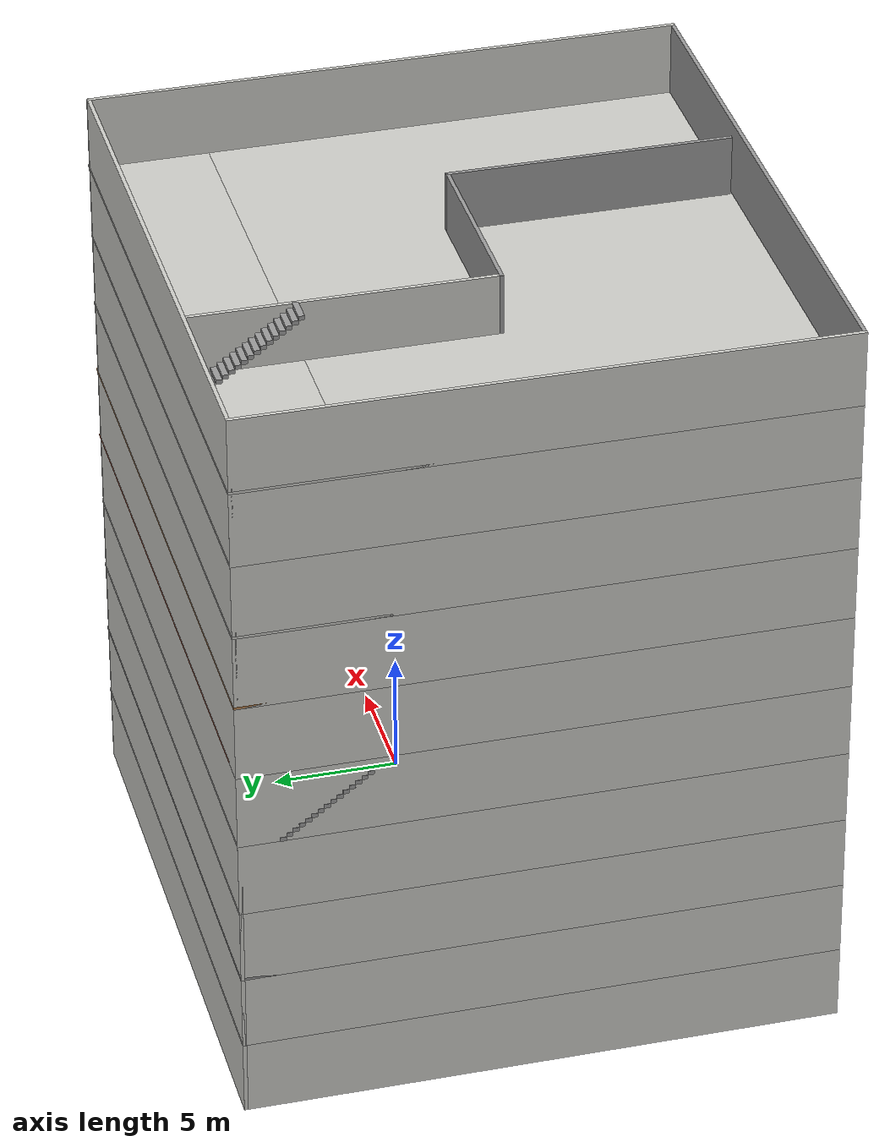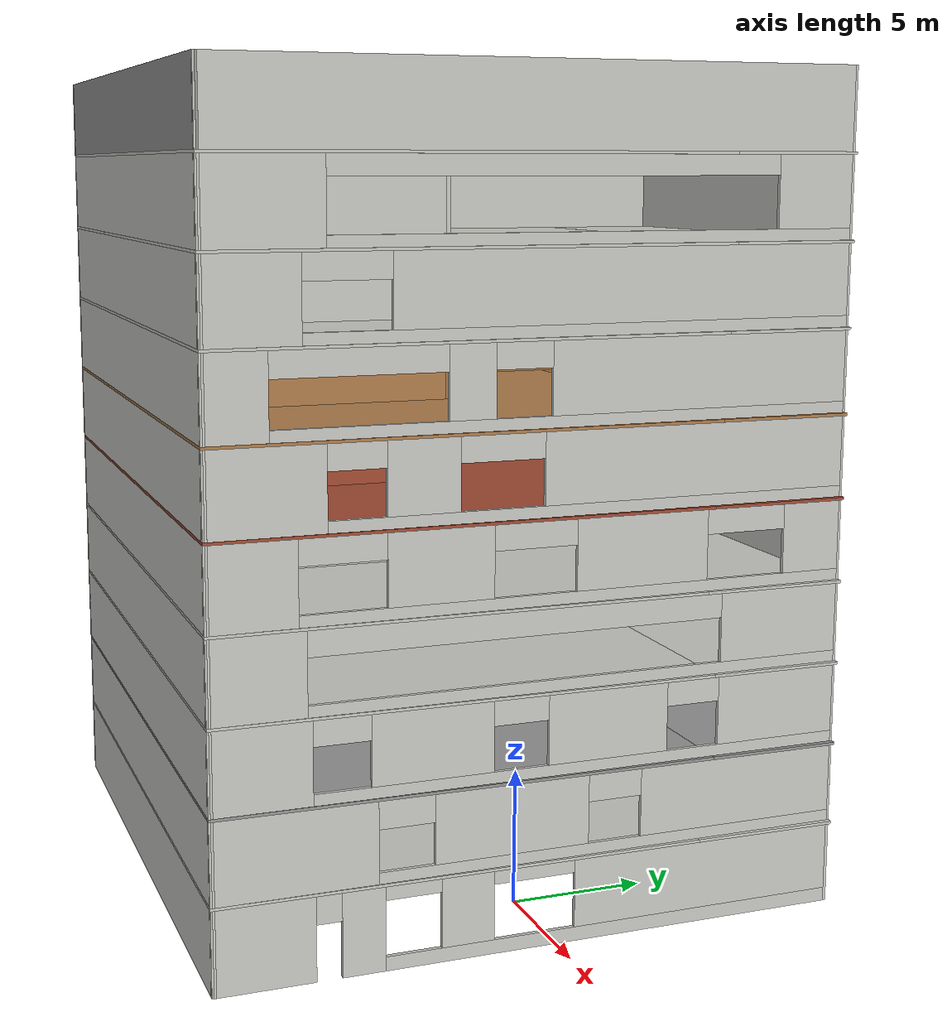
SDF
<?xml version='1.0'?>
<sdf version='1.7'>
  <model name='high_building'>
    <pose>-8.08785 -0.655 0 0 -0 0</pose>
    <link name='Floor_0'>
      <pose>0.009156 -0 3 0 -0 0</pose>
      <visual name='Floor_0_Visual_0'>
        <pose>-11.8375 0 0.05 0 -0 0</pose>
        <geometry>
          <box>
            <size>0.151533 23.0012 0.1</size>
          </box>
        </geometry>
        <material>
          <script>
            <uri>file://media/materials/scripts/gazebo.material</uri>
            <name>Gazebo/CeilingTiled</name>
          </script>
          <ambient>1 1 1 1</ambient>
        </material>
        <meta>
          <layer>1</layer>
        </meta>
      </visual>
      <collision name='Floor_0_Collision_0'>
        <geometry>
          <box>
            <size>0.151533 23.0012 0.1</size>
          </box>
        </geometry>
        <pose>-11.8375 0 0.05 0 -0 0</pose>
      </collision>
      <visual name='Floor_0_Visual_1'>
        <pose>0.075766 -2.684 0.05 0 -0 0</pose>
        <geometry>
          <box>
            <size>23.6751 17.6332 0.1</size>
          </box>
        </geometry>
        <material>
          <script>
            <uri>file://media/materials/scripts/gazebo.material</uri>
            <name>Gazebo/CeilingTiled</name>
          </script>
          <ambient>1 1 1 1</ambient>
        </material>
        <meta>
          <layer>1</layer>
        </meta>
      </visual>
      <collision name='Floor_0_Collision_1'>
        <geometry>
          <box>
            <size>23.6751 17.6332 0.1</size>
          </box>
        </geometry>
        <pose>0.075766 -2.684 0.05 0 -0 0</pose>
      </collision>
      <visual name='Floor_0_Visual_2'>
        <pose>0.575766 8.81661 0.05 0 -0 0</pose>
        <geometry>
          <box>
            <size>22.6751 5.36801 0.1</size>
          </box>
        </geometry>
        <material>
          <script>
            <uri>file://media/materials/scripts/gazebo.material</uri>
            <name>Gazebo/CeilingTiled</name>
          </script>
          <ambient>1 1 1 1</ambient>
        </material>
        <meta>
          <layer>1</layer>
        </meta>
      </visual>
      <collision name='Floor_0_Collision_2'>
        <geometry>
          <box>
            <size>22.6751 5.36801 0.1</size>
          </box>
        </geometry>
        <pose>0.575766 8.81661 0.05 0 -0 0</pose>
      </collision>
      <visual name='Floor_0_Visual_3'>
        <pose>-11.2618 10.5666 0.05 0 -0 0</pose>
        <geometry>
          <box>
            <size>1 1.86801 0.1</size>
          </box>
        </geometry>
        <material>
          <script>
            <uri>file://media/materials/scripts/gazebo.material</uri>
            <name>Gazebo/CeilingTiled</name>
          </script>
          <ambient>1 1 1 1</ambient>
        </material>
        <meta>
          <layer>1</layer>
        </meta>
      </visual>
      <collision name='Floor_0_Collision_3'>
        <geometry>
          <box>
            <size>1 1.86801 0.1</size>
          </box>
        </geometry>
        <pose>-11.2618 10.5666 0.05 0 -0 0</pose>
      </collision>
    </link>
    <link name='Floor_1'>
      <pose>0.009156 -0 6 0 -0 0</pose>
      <visual name='Floor_1_Visual_0'>
        <pose>-8.99477 0 0.05 0 -0 0</pose>
        <geometry>
          <box>
            <size>5.83706 23.0012 0.1</size>
          </box>
        </geometry>
        <material>
          <script>
            <uri>file://media/materials/scripts/gazebo.material</uri>
            <name>Gazebo/Grey</name>
          </script>
          <ambient>1 1 1 1</ambient>
        </material>
        <meta>
          <layer>2</layer>
        </meta>
      </visual>
      <collision name='Floor_1_Collision_0'>
        <geometry>
          <box>
            <size>5.83706 23.0012 0.1</size>
          </box>
        </geometry>
        <pose>-8.99477 0 0.05 0 -0 0</pose>
      </collision>
      <visual name='Floor_1_Visual_1'>
        <pose>2.91853 -2.44136 0.05 0 -0 0</pose>
        <geometry>
          <box>
            <size>17.9895 18.1185 0.1</size>
          </box>
        </geometry>
        <material>
          <script>
            <uri>file://media/materials/scripts/gazebo.material</uri>
            <name>Gazebo/Grey</name>
          </script>
          <ambient>1 1 1 1</ambient>
        </material>
        <meta>
          <layer>2</layer>
        </meta>
      </visual>
      <collision name='Floor_1_Collision_1'>
        <geometry>
          <box>
            <size>17.9895 18.1185 0.1</size>
          </box>
        </geometry>
        <pose>2.91853 -2.44136 0.05 0 -0 0</pose>
      </collision>
      <visual name='Floor_1_Visual_2'>
        <pose>3.95054 9.05926 0.05 0 -0 0</pose>
        <geometry>
          <box>
            <size>15.9255 4.88271 0.1</size>
          </box>
        </geometry>
        <material>
          <script>
            <uri>file://media/materials/scripts/gazebo.material</uri>
            <name>Gazebo/Grey</name>
          </script>
          <ambient>1 1 1 1</ambient>
        </material>
        <meta>
          <layer>2</layer>
        </meta>
      </visual>
      <collision name='Floor_1_Collision_2'>
        <geometry>
          <box>
            <size>15.9255 4.88271 0.1</size>
          </box>
        </geometry>
        <pose>3.95054 9.05926 0.05 0 -0 0</pose>
      </collision>
      <visual name='Floor_1_Visual_3'>
        <pose>-5.04424 10.9955 0.05 0 -0 0</pose>
        <geometry>
          <box>
            <size>2.06401 1.01031 0.1</size>
          </box>
        </geometry>
        <material>
          <script>
            <uri>file://media/materials/scripts/gazebo.material</uri>
            <name>Gazebo/Grey</name>
          </script>
          <ambient>1 1 1 1</ambient>
        </material>
        <meta>
          <layer>2</layer>
        </meta>
      </visual>
      <collision name='Floor_1_Collision_3'>
        <geometry>
          <box>
            <size>2.06401 1.01031 0.1</size>
          </box>
        </geometry>
        <pose>-5.04424 10.9955 0.05 0 -0 0</pose>
      </collision>
    </link>
    <link name='Floor_10'>
      <pose>0.009156 -0 21 0 -0 0</pose>
      <visual name='Floor_10_Visual_0'>
        <pose>-11.8873 0 0.05 0 -0 0</pose>
        <geometry>
          <box>
            <size>0.052045 23.0012 0.1</size>
          </box>
        </geometry>
        <material>
          <script>
            <uri>file://media/materials/scripts/gazebo.material</uri>
            <name>Gazebo/CeilingTiled</name>
          </script>
          <ambient>1 1 1 1</ambient>
        </material>
        <meta>
          <layer>7</layer>
        </meta>
      </visual>
      <collision name='Floor_10_Collision_0'>
        <geometry>
          <box>
            <size>0.052045 23.0012 0.1</size>
          </box>
        </geometry>
        <pose>-11.8873 0 0.05 0 -0 0</pose>
      </collision>
      <visual name='Floor_10_Visual_1'>
        <pose>0.026023 -2.34881 0.05 0 -0 0</pose>
        <geometry>
          <box>
            <size>23.7746 18.3036 0.1</size>
          </box>
        </geometry>
        <material>
          <script>
            <uri>file://media/materials/scripts/gazebo.material</uri>
            <name>Gazebo/CeilingTiled</name>
          </script>
          <ambient>1 1 1 1</ambient>
        </material>
        <meta>
          <layer>7</layer>
        </meta>
      </visual>
      <collision name='Floor_10_Collision_1'>
        <geometry>
          <box>
            <size>23.7746 18.3036 0.1</size>
          </box>
        </geometry>
        <pose>0.026023 -2.34881 0.05 0 -0 0</pose>
      </collision>
      <visual name='Floor_10_Visual_2'>
        <pose>0.526023 9.1518 0.05 0 -0 0</pose>
        <geometry>
          <box>
            <size>22.7746 4.69762 0.1</size>
          </box>
        </geometry>
        <material>
          <script>
            <uri>file://media/materials/scripts/gazebo.material</uri>
            <name>Gazebo/CeilingTiled</name>
          </script>
          <ambient>1 1 1 1</ambient>
        </material>
        <meta>
          <layer>7</layer>
        </meta>
      </visual>
      <collision name='Floor_10_Collision_2'>
        <geometry>
          <box>
            <size>22.7746 4.69762 0.1</size>
          </box>
        </geometry>
        <pose>0.526023 9.1518 0.05 0 -0 0</pose>
      </collision>
      <visual name='Floor_10_Visual_3'>
        <pose>-11.3613 10.9018 0.05 0 -0 0</pose>
        <geometry>
          <box>
            <size>1 1.19762 0.1</size>
          </box>
        </geometry>
        <material>
          <script>
            <uri>file://media/materials/scripts/gazebo.material</uri>
            <name>Gazebo/CeilingTiled</name>
          </script>
          <ambient>1 1 1 1</ambient>
        </material>
        <meta>
          <layer>7</layer>
        </meta>
      </visual>
      <collision name='Floor_10_Collision_3'>
        <geometry>
          <box>
            <size>1 1.19762 0.1</size>
          </box>
        </geometry>
        <pose>-11.3613 10.9018 0.05 0 -0 0</pose>
      </collision>
    </link>
    <link name='Floor_11'>
      <pose>0.009156 -0 24 0 -0 0</pose>
      <visual name='Floor_11_Visual_0'>
        <pose>-8.49253 0 0.05 0 -0 0</pose>
        <geometry>
          <box>
            <size>6.84155 23.0012 0.1</size>
          </box>
        </geometry>
        <material>
          <script>
            <uri>file://media/materials/scripts/gazebo.material</uri>
            <name>Gazebo/CeilingTiled</name>
          </script>
          <ambient>1 1 1 1</ambient>
        </material>
        <meta>
          <layer>8</layer>
        </meta>
      </visual>
      <collision name='Floor_11_Collision_0'>
        <geometry>
          <box>
            <size>6.84155 23.0012 0.1</size>
          </box>
        </geometry>
        <pose>-8.49253 0 0.05 0 -0 0</pose>
      </collision>
      <visual name='Floor_11_Visual_1'>
        <pose>3.42077 -2.26086 0.05 0 -0 0</pose>
        <geometry>
          <box>
            <size>16.9851 18.4795 0.1</size>
          </box>
        </geometry>
        <material>
          <script>
            <uri>file://media/materials/scripts/gazebo.material</uri>
            <name>Gazebo/CeilingTiled</name>
          </script>
          <ambient>1 1 1 1</ambient>
        </material>
        <meta>
          <layer>8</layer>
        </meta>
      </visual>
      <collision name='Floor_11_Collision_1'>
        <geometry>
          <box>
            <size>16.9851 18.4795 0.1</size>
          </box>
        </geometry>
        <pose>3.42077 -2.26086 0.05 0 -0 0</pose>
      </collision>
      <visual name='Floor_11_Visual_2'>
        <pose>3.92077 9.23975 0.05 0 -0 0</pose>
        <geometry>
          <box>
            <size>15.9851 4.52172 0.1</size>
          </box>
        </geometry>
        <material>
          <script>
            <uri>file://media/materials/scripts/gazebo.material</uri>
            <name>Gazebo/CeilingTiled</name>
          </script>
          <ambient>1 1 1 1</ambient>
        </material>
        <meta>
          <layer>8</layer>
        </meta>
      </visual>
      <collision name='Floor_11_Collision_2'>
        <geometry>
          <box>
            <size>15.9851 4.52172 0.1</size>
          </box>
        </geometry>
        <pose>3.92077 9.23975 0.05 0 -0 0</pose>
      </collision>
      <visual name='Floor_11_Visual_3'>
        <pose>-4.57176 10.9898 0.05 0 -0 0</pose>
        <geometry>
          <box>
            <size>1 1.02172 0.1</size>
          </box>
        </geometry>
        <material>
          <script>
            <uri>file://media/materials/scripts/gazebo.material</uri>
            <name>Gazebo/CeilingTiled</name>
          </script>
          <ambient>1 1 1 1</ambient>
        </material>
        <meta>
          <layer>8</layer>
        </meta>
      </visual>
      <collision name='Floor_11_Collision_3'>
        <geometry>
          <box>
            <size>1 1.02172 0.1</size>
          </box>
        </geometry>
        <pose>-4.57176 10.9898 0.05 0 -0 0</pose>
      </collision>
    </link>
    <link name='Floor_12'>
      <pose>0.009156 -0 27 0 -0 0</pose>
      <visual name='Floor_12_Visual_0'>
        <pose>-11.9049 0 0.05 0 -0 0</pose>
        <geometry>
          <box>
            <size>0.016868 23.0012 0.1</size>
          </box>
        </geometry>
        <material>
          <script>
            <uri>file://media/materials/scripts/gazebo.material</uri>
            <name>Gazebo/CeilingTiled</name>
          </script>
          <ambient>1 1 1 1</ambient>
        </material>
        <meta>
          <layer>9</layer>
        </meta>
      </visual>
      <collision name='Floor_12_Collision_0'>
        <geometry>
          <box>
            <size>0.016868 23.0012 0.1</size>
          </box>
        </geometry>
        <pose>-11.9049 0 0.05 0 -0 0</pose>
      </collision>
      <visual name='Floor_12_Visual_1'>
        <pose>0.008434 -2.29604 0.05 0 -0 0</pose>
        <geometry>
          <box>
            <size>23.8097 18.4091 0.1</size>
          </box>
        </geometry>
        <material>
          <script>
            <uri>file://media/materials/scripts/gazebo.material</uri>
            <name>Gazebo/CeilingTiled</name>
          </script>
          <ambient>1 1 1 1</ambient>
        </material>
        <meta>
          <layer>9</layer>
        </meta>
      </visual>
      <collision name='Floor_12_Collision_1'>
        <geometry>
          <box>
            <size>23.8097 18.4091 0.1</size>
          </box>
        </geometry>
        <pose>0.008434 -2.29604 0.05 0 -0 0</pose>
      </collision>
      <visual name='Floor_12_Visual_2'>
        <pose>0.508434 9.20457 0.05 0 -0 0</pose>
        <geometry>
          <box>
            <size>22.8097 4.59208 0.1</size>
          </box>
        </geometry>
        <material>
          <script>
            <uri>file://media/materials/scripts/gazebo.material</uri>
            <name>Gazebo/CeilingTiled</name>
          </script>
          <ambient>1 1 1 1</ambient>
        </material>
        <meta>
          <layer>9</layer>
        </meta>
      </visual>
      <collision name='Floor_12_Collision_2'>
        <geometry>
          <box>
            <size>22.8097 4.59208 0.1</size>
          </box>
        </geometry>
        <pose>0.508434 9.20457 0.05 0 -0 0</pose>
      </collision>
      <visual name='Floor_12_Visual_3'>
        <pose>-11.3964 10.9546 0.05 0 -0 0</pose>
        <geometry>
          <box>
            <size>1 1.09208 0.1</size>
          </box>
        </geometry>
        <material>
          <script>
            <uri>file://media/materials/scripts/gazebo.material</uri>
            <name>Gazebo/CeilingTiled</name>
          </script>
          <ambient>1 1 1 1</ambient>
        </material>
        <meta>
          <layer>9</layer>
        </meta>
      </visual>
      <collision name='Floor_12_Collision_3'>
        <geometry>
          <box>
            <size>1 1.09208 0.1</size>
          </box>
        </geometry>
        <pose>-11.3964 10.9546 0.05 0 -0 0</pose>
      </collision>
    </link>
    <link name='Floor_6'>
      <pose>0.009156 -0 9 0 -0 0</pose>
      <visual name='Floor_6_Visual_0'>
        <pose>-11.9073 0 0.05 0 -0 0</pose>
        <geometry>
          <box>
            <size>0.01196 23.0012 0.1</size>
          </box>
        </geometry>
        <material>
          <script>
            <uri>file://media/materials/scripts/gazebo.material</uri>
            <name>Gazebo/CeilingTiled</name>
          </script>
          <ambient>1 1 1 1</ambient>
        </material>
        <meta>
          <layer>3</layer>
        </meta>
      </visual>
      <collision name='Floor_6_Collision_0'>
        <geometry>
          <box>
            <size>0.01196 23.0012 0.1</size>
          </box>
        </geometry>
        <pose>-11.9073 0 0.05 0 -0 0</pose>
      </collision>
      <visual name='Floor_6_Visual_1'>
        <pose>0.00598 -2.45139 0.05 0 -0 0</pose>
        <geometry>
          <box>
            <size>23.8147 18.0985 0.1</size>
          </box>
        </geometry>
        <material>
          <script>
            <uri>file://media/materials/scripts/gazebo.material</uri>
            <name>Gazebo/CeilingTiled</name>
          </script>
          <ambient>1 1 1 1</ambient>
        </material>
        <meta>
          <layer>3</layer>
        </meta>
      </visual>
      <collision name='Floor_6_Collision_1'>
        <geometry>
          <box>
            <size>23.8147 18.0985 0.1</size>
          </box>
        </geometry>
        <pose>0.00598 -2.45139 0.05 0 -0 0</pose>
      </collision>
      <visual name='Floor_6_Visual_2'>
        <pose>0.50598 9.04923 0.05 0 -0 0</pose>
        <geometry>
          <box>
            <size>22.8147 4.90277 0.1</size>
          </box>
        </geometry>
        <material>
          <script>
            <uri>file://media/materials/scripts/gazebo.material</uri>
            <name>Gazebo/CeilingTiled</name>
          </script>
          <ambient>1 1 1 1</ambient>
        </material>
        <meta>
          <layer>3</layer>
        </meta>
      </visual>
      <collision name='Floor_6_Collision_2'>
        <geometry>
          <box>
            <size>22.8147 4.90277 0.1</size>
          </box>
        </geometry>
        <pose>0.50598 9.04923 0.05 0 -0 0</pose>
      </collision>
      <visual name='Floor_6_Visual_3'>
        <pose>-11.4013 10.7992 0.05 0 -0 0</pose>
        <geometry>
          <box>
            <size>1 1.40277 0.1</size>
          </box>
        </geometry>
        <material>
          <script>
            <uri>file://media/materials/scripts/gazebo.material</uri>
            <name>Gazebo/CeilingTiled</name>
          </script>
          <ambient>1 1 1 1</ambient>
        </material>
        <meta>
          <layer>3</layer>
        </meta>
      </visual>
      <collision name='Floor_6_Collision_3'>
        <geometry>
          <box>
            <size>1 1.40277 0.1</size>
          </box>
        </geometry>
        <pose>-11.4013 10.7992 0.05 0 -0 0</pose>
      </collision>
    </link>
    <link name='Floor_7'>
      <pose>0.009156 -0 12 0 -0 0</pose>
      <visual name='Floor_7_Visual_0'>
        <pose>-8.42544 0 0.05 0 -0 0</pose>
        <geometry>
          <box>
            <size>6.97573 23.0012 0.1</size>
          </box>
        </geometry>
        <material>
          <script>
            <uri>file://media/materials/scripts/gazebo.material</uri>
            <name>Gazebo/CeilingTiled</name>
          </script>
          <ambient>1 1 1 1</ambient>
        </material>
        <meta>
          <layer>4</layer>
        </meta>
      </visual>
      <collision name='Floor_7_Collision_0'>
        <geometry>
          <box>
            <size>6.97573 23.0012 0.1</size>
          </box>
        </geometry>
        <pose>-8.42544 0 0.05 0 -0 0</pose>
      </collision>
      <visual name='Floor_7_Visual_1'>
        <pose>3.48787 -2.63097 0.05 0 -0 0</pose>
        <geometry>
          <box>
            <size>16.8509 17.7393 0.1</size>
          </box>
        </geometry>
        <material>
          <script>
            <uri>file://media/materials/scripts/gazebo.material</uri>
            <name>Gazebo/CeilingTiled</name>
          </script>
          <ambient>1 1 1 1</ambient>
        </material>
        <meta>
          <layer>4</layer>
        </meta>
      </visual>
      <collision name='Floor_7_Collision_1'>
        <geometry>
          <box>
            <size>16.8509 17.7393 0.1</size>
          </box>
        </geometry>
        <pose>3.48787 -2.63097 0.05 0 -0 0</pose>
      </collision>
      <visual name='Floor_7_Visual_2'>
        <pose>3.98787 8.86965 0.05 0 -0 0</pose>
        <geometry>
          <box>
            <size>15.8509 5.26193 0.1</size>
          </box>
        </geometry>
        <material>
          <script>
            <uri>file://media/materials/scripts/gazebo.material</uri>
            <name>Gazebo/CeilingTiled</name>
          </script>
          <ambient>1 1 1 1</ambient>
        </material>
        <meta>
          <layer>4</layer>
        </meta>
      </visual>
      <collision name='Floor_7_Collision_2'>
        <geometry>
          <box>
            <size>15.8509 5.26193 0.1</size>
          </box>
        </geometry>
        <pose>3.98787 8.86965 0.05 0 -0 0</pose>
      </collision>
      <visual name='Floor_7_Visual_3'>
        <pose>-4.43757 10.6196 0.05 0 -0 0</pose>
        <geometry>
          <box>
            <size>1 1.76193 0.1</size>
          </box>
        </geometry>
        <material>
          <script>
            <uri>file://media/materials/scripts/gazebo.material</uri>
            <name>Gazebo/CeilingTiled</name>
          </script>
          <ambient>1 1 1 1</ambient>
        </material>
        <meta>
          <layer>4</layer>
        </meta>
      </visual>
      <collision name='Floor_7_Collision_3'>
        <geometry>
          <box>
            <size>1 1.76193 0.1</size>
          </box>
        </geometry>
        <pose>-4.43757 10.6196 0.05 0 -0 0</pose>
      </collision>
    </link>
    <link name='Floor_8'>
      <pose>0.009156 -0 15 0 -0 0</pose>
      <visual name='Floor_8_Visual_0'>
        <pose>0 -2.54229 0.05 0 -0 0</pose>
        <geometry>
          <box>
            <size>23.8266 17.9166 0.1</size>
          </box>
        </geometry>
        <material>
          <script>
            <uri>file://media/materials/scripts/gazebo.material</uri>
            <name>Gazebo/Bricks</name>
          </script>
          <ambient>1 1 1 1</ambient>
        </material>
        <meta>
          <layer>5</layer>
        </meta>
      </visual>
      <collision name='Floor_8_Collision_0'>
        <geometry>
          <box>
            <size>23.8266 17.9166 0.1</size>
          </box>
        </geometry>
        <pose>0 -2.54229 0.05 0 -0 0</pose>
      </collision>
      <visual name='Floor_8_Visual_1'>
        <pose>0.490844 8.95832 0.05 0 -0 0</pose>
        <geometry>
          <box>
            <size>22.8449 5.08458 0.1</size>
          </box>
        </geometry>
        <material>
          <script>
            <uri>file://media/materials/scripts/gazebo.material</uri>
            <name>Gazebo/Bricks</name>
          </script>
          <ambient>1 1 1 1</ambient>
        </material>
        <meta>
          <layer>5</layer>
        </meta>
      </visual>
      <collision name='Floor_8_Collision_1'>
        <geometry>
          <box>
            <size>22.8449 5.08458 0.1</size>
          </box>
        </geometry>
        <pose>0.490844 8.95832 0.05 0 -0 0</pose>
      </collision>
    </link>
    <link name='Floor_9'>
      <pose>0.009156 -0 18 0 -0 0</pose>
      <visual name='Floor_9_Visual_0'>
        <pose>-8.52771 0 0.05 0 -0 0</pose>
        <geometry>
          <box>
            <size>6.77119 23.0012 0.1</size>
          </box>
        </geometry>
        <material>
          <script>
            <uri>file://media/materials/scripts/gazebo.material</uri>
            <name>Gazebo/Wood</name>
          </script>
          <ambient>1 1 1 1</ambient>
        </material>
        <meta>
          <layer>6</layer>
        </meta>
      </visual>
      <collision name='Floor_9_Collision_0'>
        <geometry>
          <box>
            <size>6.77119 23.0012 0.1</size>
          </box>
        </geometry>
        <pose>-8.52771 0 0.05 0 -0 0</pose>
      </collision>
      <visual name='Floor_9_Visual_1'>
        <pose>3.38559 -2.41917 0.05 0 -0 0</pose>
        <geometry>
          <box>
            <size>17.0554 18.1629 0.1</size>
          </box>
        </geometry>
        <material>
          <script>
            <uri>file://media/materials/scripts/gazebo.material</uri>
            <name>Gazebo/Wood</name>
          </script>
          <ambient>1 1 1 1</ambient>
        </material>
        <meta>
          <layer>6</layer>
        </meta>
      </visual>
      <collision name='Floor_9_Collision_1'>
        <geometry>
          <box>
            <size>17.0554 18.1629 0.1</size>
          </box>
        </geometry>
        <pose>3.38559 -2.41917 0.05 0 -0 0</pose>
      </collision>
      <visual name='Floor_9_Visual_2'>
        <pose>3.88559 9.08145 0.05 0 -0 0</pose>
        <geometry>
          <box>
            <size>16.0554 4.83833 0.1</size>
          </box>
        </geometry>
        <material>
          <script>
            <uri>file://media/materials/scripts/gazebo.material</uri>
            <name>Gazebo/Wood</name>
          </script>
          <ambient>1 1 1 1</ambient>
        </material>
        <meta>
          <layer>6</layer>
        </meta>
      </visual>
      <collision name='Floor_9_Collision_2'>
        <geometry>
          <box>
            <size>16.0554 4.83833 0.1</size>
          </box>
        </geometry>
        <pose>3.88559 9.08145 0.05 0 -0 0</pose>
      </collision>
      <visual name='Floor_9_Visual_3'>
        <pose>-4.64212 10.8314 0.05 0 -0 0</pose>
        <geometry>
          <box>
            <size>1 1.33833 0.1</size>
          </box>
        </geometry>
        <material>
          <script>
            <uri>file://media/materials/scripts/gazebo.material</uri>
            <name>Gazebo/Wood</name>
          </script>
          <ambient>1 1 1 1</ambient>
        </material>
        <meta>
          <layer>6</layer>
        </meta>
      </visual>
      <collision name='Floor_9_Collision_3'>
        <geometry>
          <box>
            <size>1 1.33833 0.1</size>
          </box>
        </geometry>
        <pose>-4.64212 10.8314 0.05 0 -0 0</pose>
      </collision>
    </link>
    <link name='Stairs_10'>
      <visual name='Stairs_10_Visual_0'>
        <pose>-4.5626 10.3622 21.0833 0 -0 0</pose>
        <geometry>
          <box>
            <size>1 0.233333 0.166667</size>
          </box>
        </geometry>
        <material>
          <script>
            <uri>file://media/materials/scripts/gazebo.material</uri>
            <name>Gazebo/Grey</name>
          </script>
          <ambient>1 1 1 1</ambient>
        </material>
        <meta>
          <layer>7</layer>
        </meta>
      </visual>
      <collision name='Stairs_10_Collision_0'>
        <geometry>
          <box>
            <size>1 0.233333 0.166667</size>
          </box>
        </geometry>
        <pose>-4.5626 10.3622 21.0833 0 -0 0</pose>
      </collision>
      <visual name='Stairs_10_Visual_1'>
        <pose>-4.5626 10.1289 21.25 0 -0 0</pose>
        <geometry>
          <box>
            <size>1 0.233333 0.166667</size>
          </box>
        </geometry>
        <material>
          <script>
            <uri>file://media/materials/scripts/gazebo.material</uri>
            <name>Gazebo/Grey</name>
          </script>
          <ambient>1 1 1 1</ambient>
        </material>
        <meta>
          <layer>7</layer>
        </meta>
      </visual>
      <collision name='Stairs_10_Collision_1'>
        <geometry>
          <box>
            <size>1 0.233333 0.166667</size>
          </box>
        </geometry>
        <pose>-4.5626 10.1289 21.25 0 -0 0</pose>
      </collision>
      <visual name='Stairs_10_Visual_2'>
        <pose>-4.5626 9.89555 21.4167 0 -0 0</pose>
        <geometry>
          <box>
            <size>1 0.233333 0.166667</size>
          </box>
        </geometry>
        <material>
          <script>
            <uri>file://media/materials/scripts/gazebo.material</uri>
            <name>Gazebo/Grey</name>
          </script>
          <ambient>1 1 1 1</ambient>
        </material>
        <meta>
          <layer>7</layer>
        </meta>
      </visual>
      <collision name='Stairs_10_Collision_2'>
        <geometry>
          <box>
            <size>1 0.233333 0.166667</size>
          </box>
        </geometry>
        <pose>-4.5626 9.89555 21.4167 0 -0 0</pose>
      </collision>
      <visual name='Stairs_10_Visual_3'>
        <pose>-4.5626 9.66222 21.5833 0 -0 0</pose>
        <geometry>
          <box>
            <size>1 0.233333 0.166667</size>
          </box>
        </geometry>
        <material>
          <script>
            <uri>file://media/materials/scripts/gazebo.material</uri>
            <name>Gazebo/Grey</name>
          </script>
          <ambient>1 1 1 1</ambient>
        </material>
        <meta>
          <layer>7</layer>
        </meta>
      </visual>
      <collision name='Stairs_10_Collision_3'>
        <geometry>
          <box>
            <size>1 0.233333 0.166667</size>
          </box>
        </geometry>
        <pose>-4.5626 9.66222 21.5833 0 -0 0</pose>
      </collision>
      <visual name='Stairs_10_Visual_4'>
        <pose>-4.5626 9.42889 21.75 0 -0 0</pose>
        <geometry>
          <box>
            <size>1 0.233333 0.166667</size>
          </box>
        </geometry>
        <material>
          <script>
            <uri>file://media/materials/scripts/gazebo.material</uri>
            <name>Gazebo/Grey</name>
          </script>
          <ambient>1 1 1 1</ambient>
        </material>
        <meta>
          <layer>7</layer>
        </meta>
      </visual>
      <collision name='Stairs_10_Collision_4'>
        <geometry>
          <box>
            <size>1 0.233333 0.166667</size>
          </box>
        </geometry>
        <pose>-4.5626 9.42889 21.75 0 -0 0</pose>
      </collision>
      <visual name='Stairs_10_Visual_5'>
        <pose>-4.5626 9.19555 21.9167 0 -0 0</pose>
        <geometry>
          <box>
            <size>1 0.233333 0.166667</size>
          </box>
        </geometry>
        <material>
          <script>
            <uri>file://media/materials/scripts/gazebo.material</uri>
            <name>Gazebo/Grey</name>
          </script>
          <ambient>1 1 1 1</ambient>
        </material>
        <meta>
          <layer>7</layer>
        </meta>
      </visual>
      <collision name='Stairs_10_Collision_5'>
        <geometry>
          <box>
            <size>1 0.233333 0.166667</size>
          </box>
        </geometry>
        <pose>-4.5626 9.19555 21.9167 0 -0 0</pose>
      </collision>
      <visual name='Stairs_10_Visual_6'>
        <pose>-4.5626 8.96222 22.0833 0 -0 0</pose>
        <geometry>
          <box>
            <size>1 0.233333 0.166667</size>
          </box>
        </geometry>
        <material>
          <script>
            <uri>file://media/materials/scripts/gazebo.material</uri>
            <name>Gazebo/Grey</name>
          </script>
          <ambient>1 1 1 1</ambient>
        </material>
        <meta>
          <layer>7</layer>
        </meta>
      </visual>
      <collision name='Stairs_10_Collision_6'>
        <geometry>
          <box>
            <size>1 0.233333 0.166667</size>
          </box>
        </geometry>
        <pose>-4.5626 8.96222 22.0833 0 -0 0</pose>
      </collision>
      <visual name='Stairs_10_Visual_7'>
        <pose>-4.5626 8.72889 22.25 0 -0 0</pose>
        <geometry>
          <box>
            <size>1 0.233333 0.166667</size>
          </box>
        </geometry>
        <material>
          <script>
            <uri>file://media/materials/scripts/gazebo.material</uri>
            <name>Gazebo/Grey</name>
          </script>
          <ambient>1 1 1 1</ambient>
        </material>
        <meta>
          <layer>7</layer>
        </meta>
      </visual>
      <collision name='Stairs_10_Collision_7'>
        <geometry>
          <box>
            <size>1 0.233333 0.166667</size>
          </box>
        </geometry>
        <pose>-4.5626 8.72889 22.25 0 -0 0</pose>
      </collision>
      <visual name='Stairs_10_Visual_8'>
        <pose>-4.5626 8.49555 22.4167 0 -0 0</pose>
        <geometry>
          <box>
            <size>1 0.233333 0.166667</size>
          </box>
        </geometry>
        <material>
          <script>
            <uri>file://media/materials/scripts/gazebo.material</uri>
            <name>Gazebo/Grey</name>
          </script>
          <ambient>1 1 1 1</ambient>
        </material>
        <meta>
          <layer>7</layer>
        </meta>
      </visual>
      <collision name='Stairs_10_Collision_8'>
        <geometry>
          <box>
            <size>1 0.233333 0.166667</size>
          </box>
        </geometry>
        <pose>-4.5626 8.49555 22.4167 0 -0 0</pose>
      </collision>
      <visual name='Stairs_10_Visual_9'>
        <pose>-4.5626 8.26222 22.5833 0 -0 0</pose>
        <geometry>
          <box>
            <size>1 0.233333 0.166667</size>
          </box>
        </geometry>
        <material>
          <script>
            <uri>file://media/materials/scripts/gazebo.material</uri>
            <name>Gazebo/Grey</name>
          </script>
          <ambient>1 1 1 1</ambient>
        </material>
        <meta>
          <layer>7</layer>
        </meta>
      </visual>
      <collision name='Stairs_10_Collision_9'>
        <geometry>
          <box>
            <size>1 0.233333 0.166667</size>
          </box>
        </geometry>
        <pose>-4.5626 8.26222 22.5833 0 -0 0</pose>
      </collision>
      <visual name='Stairs_10_Visual_10'>
        <pose>-4.5626 8.02889 22.75 0 -0 0</pose>
        <geometry>
          <box>
            <size>1 0.233333 0.166667</size>
          </box>
        </geometry>
        <material>
          <script>
            <uri>file://media/materials/scripts/gazebo.material</uri>
            <name>Gazebo/Grey</name>
          </script>
          <ambient>1 1 1 1</ambient>
        </material>
        <meta>
          <layer>7</layer>
        </meta>
      </visual>
      <collision name='Stairs_10_Collision_10'>
        <geometry>
          <box>
            <size>1 0.233333 0.166667</size>
          </box>
        </geometry>
        <pose>-4.5626 8.02889 22.75 0 -0 0</pose>
      </collision>
      <visual name='Stairs_10_Visual_11'>
        <pose>-4.5626 7.79555 22.9167 0 -0 0</pose>
        <geometry>
          <box>
            <size>1 0.233333 0.166667</size>
          </box>
        </geometry>
        <material>
          <script>
            <uri>file://media/materials/scripts/gazebo.material</uri>
            <name>Gazebo/Grey</name>
          </script>
          <ambient>1 1 1 1</ambient>
        </material>
        <meta>
          <layer>7</layer>
        </meta>
      </visual>
      <collision name='Stairs_10_Collision_11'>
        <geometry>
          <box>
            <size>1 0.233333 0.166667</size>
          </box>
        </geometry>
        <pose>-4.5626 7.79555 22.9167 0 -0 0</pose>
      </collision>
      <visual name='Stairs_10_Visual_12'>
        <pose>-4.5626 7.56222 23.0833 0 -0 0</pose>
        <geometry>
          <box>
            <size>1 0.233333 0.166667</size>
          </box>
        </geometry>
        <material>
          <script>
            <uri>file://media/materials/scripts/gazebo.material</uri>
            <name>Gazebo/Grey</name>
          </script>
          <ambient>1 1 1 1</ambient>
        </material>
        <meta>
          <layer>7</layer>
        </meta>
      </visual>
      <collision name='Stairs_10_Collision_12'>
        <geometry>
          <box>
            <size>1 0.233333 0.166667</size>
          </box>
        </geometry>
        <pose>-4.5626 7.56222 23.0833 0 -0 0</pose>
      </collision>
      <visual name='Stairs_10_Visual_13'>
        <pose>-4.5626 7.32889 23.25 0 -0 0</pose>
        <geometry>
          <box>
            <size>1 0.233333 0.166667</size>
          </box>
        </geometry>
        <material>
          <script>
            <uri>file://media/materials/scripts/gazebo.material</uri>
            <name>Gazebo/Grey</name>
          </script>
          <ambient>1 1 1 1</ambient>
        </material>
        <meta>
          <layer>7</layer>
        </meta>
      </visual>
      <collision name='Stairs_10_Collision_13'>
        <geometry>
          <box>
            <size>1 0.233333 0.166667</size>
          </box>
        </geometry>
        <pose>-4.5626 7.32889 23.25 0 -0 0</pose>
      </collision>
      <visual name='Stairs_10_Visual_14'>
        <pose>-4.5626 7.09555 23.4167 0 -0 0</pose>
        <geometry>
          <box>
            <size>1 0.233333 0.166667</size>
          </box>
        </geometry>
        <material>
          <script>
            <uri>file://media/materials/scripts/gazebo.material</uri>
            <name>Gazebo/Grey</name>
          </script>
          <ambient>1 1 1 1</ambient>
        </material>
        <meta>
          <layer>7</layer>
        </meta>
      </visual>
      <collision name='Stairs_10_Collision_14'>
        <geometry>
          <box>
            <size>1 0.233333 0.166667</size>
          </box>
        </geometry>
        <pose>-4.5626 7.09555 23.4167 0 -0 0</pose>
      </collision>
    </link>
    <link name='Stairs_11'>
      <visual name='Stairs_11_Visual_0'>
        <pose>-11.3873 10.2919 24.0833 0 -0 0</pose>
        <geometry>
          <box>
            <size>1 0.233333 0.166667</size>
          </box>
        </geometry>
        <material>
          <script>
            <uri>file://media/materials/scripts/gazebo.material</uri>
            <name>Gazebo/Grey</name>
          </script>
          <ambient>1 1 1 1</ambient>
        </material>
        <meta>
          <layer>8</layer>
        </meta>
      </visual>
      <collision name='Stairs_11_Collision_0'>
        <geometry>
          <box>
            <size>1 0.233333 0.166667</size>
          </box>
        </geometry>
        <pose>-11.3873 10.2919 24.0833 0 -0 0</pose>
      </collision>
      <visual name='Stairs_11_Visual_1'>
        <pose>-11.3873 10.0585 24.25 0 -0 0</pose>
        <geometry>
          <box>
            <size>1 0.233333 0.166667</size>
          </box>
        </geometry>
        <material>
          <script>
            <uri>file://media/materials/scripts/gazebo.material</uri>
            <name>Gazebo/Grey</name>
          </script>
          <ambient>1 1 1 1</ambient>
        </material>
        <meta>
          <layer>8</layer>
        </meta>
      </visual>
      <collision name='Stairs_11_Collision_1'>
        <geometry>
          <box>
            <size>1 0.233333 0.166667</size>
          </box>
        </geometry>
        <pose>-11.3873 10.0585 24.25 0 -0 0</pose>
      </collision>
      <visual name='Stairs_11_Visual_2'>
        <pose>-11.3873 9.8252 24.4167 0 -0 0</pose>
        <geometry>
          <box>
            <size>1 0.233333 0.166667</size>
          </box>
        </geometry>
        <material>
          <script>
            <uri>file://media/materials/scripts/gazebo.material</uri>
            <name>Gazebo/Grey</name>
          </script>
          <ambient>1 1 1 1</ambient>
        </material>
        <meta>
          <layer>8</layer>
        </meta>
      </visual>
      <collision name='Stairs_11_Collision_2'>
        <geometry>
          <box>
            <size>1 0.233333 0.166667</size>
          </box>
        </geometry>
        <pose>-11.3873 9.8252 24.4167 0 -0 0</pose>
      </collision>
      <visual name='Stairs_11_Visual_3'>
        <pose>-11.3873 9.59186 24.5833 0 -0 0</pose>
        <geometry>
          <box>
            <size>1 0.233333 0.166667</size>
          </box>
        </geometry>
        <material>
          <script>
            <uri>file://media/materials/scripts/gazebo.material</uri>
            <name>Gazebo/Grey</name>
          </script>
          <ambient>1 1 1 1</ambient>
        </material>
        <meta>
          <layer>8</layer>
        </meta>
      </visual>
      <collision name='Stairs_11_Collision_3'>
        <geometry>
          <box>
            <size>1 0.233333 0.166667</size>
          </box>
        </geometry>
        <pose>-11.3873 9.59186 24.5833 0 -0 0</pose>
      </collision>
      <visual name='Stairs_11_Visual_4'>
        <pose>-11.3873 9.35853 24.75 0 -0 0</pose>
        <geometry>
          <box>
            <size>1 0.233333 0.166667</size>
          </box>
        </geometry>
        <material>
          <script>
            <uri>file://media/materials/scripts/gazebo.material</uri>
            <name>Gazebo/Grey</name>
          </script>
          <ambient>1 1 1 1</ambient>
        </material>
        <meta>
          <layer>8</layer>
        </meta>
      </visual>
      <collision name='Stairs_11_Collision_4'>
        <geometry>
          <box>
            <size>1 0.233333 0.166667</size>
          </box>
        </geometry>
        <pose>-11.3873 9.35853 24.75 0 -0 0</pose>
      </collision>
      <visual name='Stairs_11_Visual_5'>
        <pose>-11.3873 9.1252 24.9167 0 -0 0</pose>
        <geometry>
          <box>
            <size>1 0.233333 0.166667</size>
          </box>
        </geometry>
        <material>
          <script>
            <uri>file://media/materials/scripts/gazebo.material</uri>
            <name>Gazebo/Grey</name>
          </script>
          <ambient>1 1 1 1</ambient>
        </material>
        <meta>
          <layer>8</layer>
        </meta>
      </visual>
      <collision name='Stairs_11_Collision_5'>
        <geometry>
          <box>
            <size>1 0.233333 0.166667</size>
          </box>
        </geometry>
        <pose>-11.3873 9.1252 24.9167 0 -0 0</pose>
      </collision>
      <visual name='Stairs_11_Visual_6'>
        <pose>-11.3873 8.89186 25.0833 0 -0 0</pose>
        <geometry>
          <box>
            <size>1 0.233333 0.166667</size>
          </box>
        </geometry>
        <material>
          <script>
            <uri>file://media/materials/scripts/gazebo.material</uri>
            <name>Gazebo/Grey</name>
          </script>
          <ambient>1 1 1 1</ambient>
        </material>
        <meta>
          <layer>8</layer>
        </meta>
      </visual>
      <collision name='Stairs_11_Collision_6'>
        <geometry>
          <box>
            <size>1 0.233333 0.166667</size>
          </box>
        </geometry>
        <pose>-11.3873 8.89186 25.0833 0 -0 0</pose>
      </collision>
      <visual name='Stairs_11_Visual_7'>
        <pose>-11.3873 8.65853 25.25 0 -0 0</pose>
        <geometry>
          <box>
            <size>1 0.233333 0.166667</size>
          </box>
        </geometry>
        <material>
          <script>
            <uri>file://media/materials/scripts/gazebo.material</uri>
            <name>Gazebo/Grey</name>
          </script>
          <ambient>1 1 1 1</ambient>
        </material>
        <meta>
          <layer>8</layer>
        </meta>
      </visual>
      <collision name='Stairs_11_Collision_7'>
        <geometry>
          <box>
            <size>1 0.233333 0.166667</size>
          </box>
        </geometry>
        <pose>-11.3873 8.65853 25.25 0 -0 0</pose>
      </collision>
      <visual name='Stairs_11_Visual_8'>
        <pose>-11.3873 8.4252 25.4167 0 -0 0</pose>
        <geometry>
          <box>
            <size>1 0.233333 0.166667</size>
          </box>
        </geometry>
        <material>
          <script>
            <uri>file://media/materials/scripts/gazebo.material</uri>
            <name>Gazebo/Grey</name>
          </script>
          <ambient>1 1 1 1</ambient>
        </material>
        <meta>
          <layer>8</layer>
        </meta>
      </visual>
      <collision name='Stairs_11_Collision_8'>
        <geometry>
          <box>
            <size>1 0.233333 0.166667</size>
          </box>
        </geometry>
        <pose>-11.3873 8.4252 25.4167 0 -0 0</pose>
      </collision>
      <visual name='Stairs_11_Visual_9'>
        <pose>-11.3873 8.19186 25.5833 0 -0 0</pose>
        <geometry>
          <box>
            <size>1 0.233333 0.166667</size>
          </box>
        </geometry>
        <material>
          <script>
            <uri>file://media/materials/scripts/gazebo.material</uri>
            <name>Gazebo/Grey</name>
          </script>
          <ambient>1 1 1 1</ambient>
        </material>
        <meta>
          <layer>8</layer>
        </meta>
      </visual>
      <collision name='Stairs_11_Collision_9'>
        <geometry>
          <box>
            <size>1 0.233333 0.166667</size>
          </box>
        </geometry>
        <pose>-11.3873 8.19186 25.5833 0 -0 0</pose>
      </collision>
      <visual name='Stairs_11_Visual_10'>
        <pose>-11.3873 7.95853 25.75 0 -0 0</pose>
        <geometry>
          <box>
            <size>1 0.233333 0.166667</size>
          </box>
        </geometry>
        <material>
          <script>
            <uri>file://media/materials/scripts/gazebo.material</uri>
            <name>Gazebo/Grey</name>
          </script>
          <ambient>1 1 1 1</ambient>
        </material>
        <meta>
          <layer>8</layer>
        </meta>
      </visual>
      <collision name='Stairs_11_Collision_10'>
        <geometry>
          <box>
            <size>1 0.233333 0.166667</size>
          </box>
        </geometry>
        <pose>-11.3873 7.95853 25.75 0 -0 0</pose>
      </collision>
      <visual name='Stairs_11_Visual_11'>
        <pose>-11.3873 7.7252 25.9167 0 -0 0</pose>
        <geometry>
          <box>
            <size>1 0.233333 0.166667</size>
          </box>
        </geometry>
        <material>
          <script>
            <uri>file://media/materials/scripts/gazebo.material</uri>
            <name>Gazebo/Grey</name>
          </script>
          <ambient>1 1 1 1</ambient>
        </material>
        <meta>
          <layer>8</layer>
        </meta>
      </visual>
      <collision name='Stairs_11_Collision_11'>
        <geometry>
          <box>
            <size>1 0.233333 0.166667</size>
          </box>
        </geometry>
        <pose>-11.3873 7.7252 25.9167 0 -0 0</pose>
      </collision>
      <visual name='Stairs_11_Visual_12'>
        <pose>-11.3873 7.49186 26.0833 0 -0 0</pose>
        <geometry>
          <box>
            <size>1 0.233333 0.166667</size>
          </box>
        </geometry>
        <material>
          <script>
            <uri>file://media/materials/scripts/gazebo.material</uri>
            <name>Gazebo/Grey</name>
          </script>
          <ambient>1 1 1 1</ambient>
        </material>
        <meta>
          <layer>8</layer>
        </meta>
      </visual>
      <collision name='Stairs_11_Collision_12'>
        <geometry>
          <box>
            <size>1 0.233333 0.166667</size>
          </box>
        </geometry>
        <pose>-11.3873 7.49186 26.0833 0 -0 0</pose>
      </collision>
      <visual name='Stairs_11_Visual_13'>
        <pose>-11.3873 7.25853 26.25 0 -0 0</pose>
        <geometry>
          <box>
            <size>1 0.233333 0.166667</size>
          </box>
        </geometry>
        <material>
          <script>
            <uri>file://media/materials/scripts/gazebo.material</uri>
            <name>Gazebo/Grey</name>
          </script>
          <ambient>1 1 1 1</ambient>
        </material>
        <meta>
          <layer>8</layer>
        </meta>
      </visual>
      <collision name='Stairs_11_Collision_13'>
        <geometry>
          <box>
            <size>1 0.233333 0.166667</size>
          </box>
        </geometry>
        <pose>-11.3873 7.25853 26.25 0 -0 0</pose>
      </collision>
      <visual name='Stairs_11_Visual_14'>
        <pose>-11.3873 7.0252 26.4167 0 -0 0</pose>
        <geometry>
          <box>
            <size>1 0.233333 0.166667</size>
          </box>
        </geometry>
        <material>
          <script>
            <uri>file://media/materials/scripts/gazebo.material</uri>
            <name>Gazebo/Grey</name>
          </script>
          <ambient>1 1 1 1</ambient>
        </material>
        <meta>
          <layer>8</layer>
        </meta>
      </visual>
      <collision name='Stairs_11_Collision_14'>
        <geometry>
          <box>
            <size>1 0.233333 0.166667</size>
          </box>
        </geometry>
        <pose>-11.3873 7.0252 26.4167 0 -0 0</pose>
      </collision>
    </link>
    <link name='Stairs_12'>
      <visual name='Stairs_12_Visual_0'>
        <pose>-4.45707 10.4678 27.0833 0 -0 0</pose>
        <geometry>
          <box>
            <size>1 0.233333 0.166667</size>
          </box>
        </geometry>
        <material>
          <script>
            <uri>file://media/materials/scripts/gazebo.material</uri>
            <name>Gazebo/Grey</name>
          </script>
          <ambient>1 1 1 1</ambient>
        </material>
        <meta>
          <layer>9</layer>
        </meta>
      </visual>
      <collision name='Stairs_12_Collision_0'>
        <geometry>
          <box>
            <size>1 0.233333 0.166667</size>
          </box>
        </geometry>
        <pose>-4.45707 10.4678 27.0833 0 -0 0</pose>
      </collision>
      <visual name='Stairs_12_Visual_1'>
        <pose>-4.45707 10.2344 27.25 0 -0 0</pose>
        <geometry>
          <box>
            <size>1 0.233333 0.166667</size>
          </box>
        </geometry>
        <material>
          <script>
            <uri>file://media/materials/scripts/gazebo.material</uri>
            <name>Gazebo/Grey</name>
          </script>
          <ambient>1 1 1 1</ambient>
        </material>
        <meta>
          <layer>9</layer>
        </meta>
      </visual>
      <collision name='Stairs_12_Collision_1'>
        <geometry>
          <box>
            <size>1 0.233333 0.166667</size>
          </box>
        </geometry>
        <pose>-4.45707 10.2344 27.25 0 -0 0</pose>
      </collision>
      <visual name='Stairs_12_Visual_2'>
        <pose>-4.45707 10.0011 27.4167 0 -0 0</pose>
        <geometry>
          <box>
            <size>1 0.233333 0.166667</size>
          </box>
        </geometry>
        <material>
          <script>
            <uri>file://media/materials/scripts/gazebo.material</uri>
            <name>Gazebo/Grey</name>
          </script>
          <ambient>1 1 1 1</ambient>
        </material>
        <meta>
          <layer>9</layer>
        </meta>
      </visual>
      <collision name='Stairs_12_Collision_2'>
        <geometry>
          <box>
            <size>1 0.233333 0.166667</size>
          </box>
        </geometry>
        <pose>-4.45707 10.0011 27.4167 0 -0 0</pose>
      </collision>
      <visual name='Stairs_12_Visual_3'>
        <pose>-4.45707 9.76776 27.5833 0 -0 0</pose>
        <geometry>
          <box>
            <size>1 0.233333 0.166667</size>
          </box>
        </geometry>
        <material>
          <script>
            <uri>file://media/materials/scripts/gazebo.material</uri>
            <name>Gazebo/Grey</name>
          </script>
          <ambient>1 1 1 1</ambient>
        </material>
        <meta>
          <layer>9</layer>
        </meta>
      </visual>
      <collision name='Stairs_12_Collision_3'>
        <geometry>
          <box>
            <size>1 0.233333 0.166667</size>
          </box>
        </geometry>
        <pose>-4.45707 9.76776 27.5833 0 -0 0</pose>
      </collision>
      <visual name='Stairs_12_Visual_4'>
        <pose>-4.45707 9.53442 27.75 0 -0 0</pose>
        <geometry>
          <box>
            <size>1 0.233333 0.166667</size>
          </box>
        </geometry>
        <material>
          <script>
            <uri>file://media/materials/scripts/gazebo.material</uri>
            <name>Gazebo/Grey</name>
          </script>
          <ambient>1 1 1 1</ambient>
        </material>
        <meta>
          <layer>9</layer>
        </meta>
      </visual>
      <collision name='Stairs_12_Collision_4'>
        <geometry>
          <box>
            <size>1 0.233333 0.166667</size>
          </box>
        </geometry>
        <pose>-4.45707 9.53442 27.75 0 -0 0</pose>
      </collision>
      <visual name='Stairs_12_Visual_5'>
        <pose>-4.45707 9.30109 27.9167 0 -0 0</pose>
        <geometry>
          <box>
            <size>1 0.233333 0.166667</size>
          </box>
        </geometry>
        <material>
          <script>
            <uri>file://media/materials/scripts/gazebo.material</uri>
            <name>Gazebo/Grey</name>
          </script>
          <ambient>1 1 1 1</ambient>
        </material>
        <meta>
          <layer>9</layer>
        </meta>
      </visual>
      <collision name='Stairs_12_Collision_5'>
        <geometry>
          <box>
            <size>1 0.233333 0.166667</size>
          </box>
        </geometry>
        <pose>-4.45707 9.30109 27.9167 0 -0 0</pose>
      </collision>
      <visual name='Stairs_12_Visual_6'>
        <pose>-4.45707 9.06776 28.0833 0 -0 0</pose>
        <geometry>
          <box>
            <size>1 0.233333 0.166667</size>
          </box>
        </geometry>
        <material>
          <script>
            <uri>file://media/materials/scripts/gazebo.material</uri>
            <name>Gazebo/Grey</name>
          </script>
          <ambient>1 1 1 1</ambient>
        </material>
        <meta>
          <layer>9</layer>
        </meta>
      </visual>
      <collision name='Stairs_12_Collision_6'>
        <geometry>
          <box>
            <size>1 0.233333 0.166667</size>
          </box>
        </geometry>
        <pose>-4.45707 9.06776 28.0833 0 -0 0</pose>
      </collision>
      <visual name='Stairs_12_Visual_7'>
        <pose>-4.45707 8.83442 28.25 0 -0 0</pose>
        <geometry>
          <box>
            <size>1 0.233333 0.166667</size>
          </box>
        </geometry>
        <material>
          <script>
            <uri>file://media/materials/scripts/gazebo.material</uri>
            <name>Gazebo/Grey</name>
          </script>
          <ambient>1 1 1 1</ambient>
        </material>
        <meta>
          <layer>9</layer>
        </meta>
      </visual>
      <collision name='Stairs_12_Collision_7'>
        <geometry>
          <box>
            <size>1 0.233333 0.166667</size>
          </box>
        </geometry>
        <pose>-4.45707 8.83442 28.25 0 -0 0</pose>
      </collision>
      <visual name='Stairs_12_Visual_8'>
        <pose>-4.45707 8.60109 28.4167 0 -0 0</pose>
        <geometry>
          <box>
            <size>1 0.233333 0.166667</size>
          </box>
        </geometry>
        <material>
          <script>
            <uri>file://media/materials/scripts/gazebo.material</uri>
            <name>Gazebo/Grey</name>
          </script>
          <ambient>1 1 1 1</ambient>
        </material>
        <meta>
          <layer>9</layer>
        </meta>
      </visual>
      <collision name='Stairs_12_Collision_8'>
        <geometry>
          <box>
            <size>1 0.233333 0.166667</size>
          </box>
        </geometry>
        <pose>-4.45707 8.60109 28.4167 0 -0 0</pose>
      </collision>
      <visual name='Stairs_12_Visual_9'>
        <pose>-4.45707 8.36776 28.5833 0 -0 0</pose>
        <geometry>
          <box>
            <size>1 0.233333 0.166667</size>
          </box>
        </geometry>
        <material>
          <script>
            <uri>file://media/materials/scripts/gazebo.material</uri>
            <name>Gazebo/Grey</name>
          </script>
          <ambient>1 1 1 1</ambient>
        </material>
        <meta>
          <layer>9</layer>
        </meta>
      </visual>
      <collision name='Stairs_12_Collision_9'>
        <geometry>
          <box>
            <size>1 0.233333 0.166667</size>
          </box>
        </geometry>
        <pose>-4.45707 8.36776 28.5833 0 -0 0</pose>
      </collision>
      <visual name='Stairs_12_Visual_10'>
        <pose>-4.45707 8.13442 28.75 0 -0 0</pose>
        <geometry>
          <box>
            <size>1 0.233333 0.166667</size>
          </box>
        </geometry>
        <material>
          <script>
            <uri>file://media/materials/scripts/gazebo.material</uri>
            <name>Gazebo/Grey</name>
          </script>
          <ambient>1 1 1 1</ambient>
        </material>
        <meta>
          <layer>9</layer>
        </meta>
      </visual>
      <collision name='Stairs_12_Collision_10'>
        <geometry>
          <box>
            <size>1 0.233333 0.166667</size>
          </box>
        </geometry>
        <pose>-4.45707 8.13442 28.75 0 -0 0</pose>
      </collision>
      <visual name='Stairs_12_Visual_11'>
        <pose>-4.45707 7.90109 28.9167 0 -0 0</pose>
        <geometry>
          <box>
            <size>1 0.233333 0.166667</size>
          </box>
        </geometry>
        <material>
          <script>
            <uri>file://media/materials/scripts/gazebo.material</uri>
            <name>Gazebo/Grey</name>
          </script>
          <ambient>1 1 1 1</ambient>
        </material>
        <meta>
          <layer>9</layer>
        </meta>
      </visual>
      <collision name='Stairs_12_Collision_11'>
        <geometry>
          <box>
            <size>1 0.233333 0.166667</size>
          </box>
        </geometry>
        <pose>-4.45707 7.90109 28.9167 0 -0 0</pose>
      </collision>
      <visual name='Stairs_12_Visual_12'>
        <pose>-4.45707 7.66776 29.0833 0 -0 0</pose>
        <geometry>
          <box>
            <size>1 0.233333 0.166667</size>
          </box>
        </geometry>
        <material>
          <script>
            <uri>file://media/materials/scripts/gazebo.material</uri>
            <name>Gazebo/Grey</name>
          </script>
          <ambient>1 1 1 1</ambient>
        </material>
        <meta>
          <layer>9</layer>
        </meta>
      </visual>
      <collision name='Stairs_12_Collision_12'>
        <geometry>
          <box>
            <size>1 0.233333 0.166667</size>
          </box>
        </geometry>
        <pose>-4.45707 7.66776 29.0833 0 -0 0</pose>
      </collision>
      <visual name='Stairs_12_Visual_13'>
        <pose>-4.45707 7.43442 29.25 0 -0 0</pose>
        <geometry>
          <box>
            <size>1 0.233333 0.166667</size>
          </box>
        </geometry>
        <material>
          <script>
            <uri>file://media/materials/scripts/gazebo.material</uri>
            <name>Gazebo/Grey</name>
          </script>
          <ambient>1 1 1 1</ambient>
        </material>
        <meta>
          <layer>9</layer>
        </meta>
      </visual>
      <collision name='Stairs_12_Collision_13'>
        <geometry>
          <box>
            <size>1 0.233333 0.166667</size>
          </box>
        </geometry>
        <pose>-4.45707 7.43442 29.25 0 -0 0</pose>
      </collision>
      <visual name='Stairs_12_Visual_14'>
        <pose>-4.45707 7.20109 29.4167 0 -0 0</pose>
        <geometry>
          <box>
            <size>1 0.233333 0.166667</size>
          </box>
        </geometry>
        <material>
          <script>
            <uri>file://media/materials/scripts/gazebo.material</uri>
            <name>Gazebo/Grey</name>
          </script>
          <ambient>1 1 1 1</ambient>
        </material>
        <meta>
          <layer>9</layer>
        </meta>
      </visual>
      <collision name='Stairs_12_Collision_14'>
        <geometry>
          <box>
            <size>1 0.233333 0.166667</size>
          </box>
        </geometry>
        <pose>-4.45707 7.20109 29.4167 0 -0 0</pose>
      </collision>
    </link>
    <link name='Stairs_2'>
      <visual name='Stairs_2_Visual_0'>
        <pose>-5.03508 10.3612 3.08333 0 -0 0</pose>
        <geometry>
          <box>
            <size>2.06401 0.25816 0.166667</size>
          </box>
        </geometry>
        <material>
          <script>
            <uri>file://media/materials/scripts/gazebo.material</uri>
            <name>Gazebo/Grey</name>
          </script>
          <ambient>1 1 1 1</ambient>
        </material>
        <meta>
          <layer>1</layer>
        </meta>
      </visual>
      <collision name='Stairs_2_Collision_0'>
        <geometry>
          <box>
            <size>2.06401 0.25816 0.166667</size>
          </box>
        </geometry>
        <pose>-5.03508 10.3612 3.08333 0 -0 0</pose>
      </collision>
      <visual name='Stairs_2_Visual_1'>
        <pose>-5.03508 10.1031 3.25 0 -0 0</pose>
        <geometry>
          <box>
            <size>2.06401 0.25816 0.166667</size>
          </box>
        </geometry>
        <material>
          <script>
            <uri>file://media/materials/scripts/gazebo.material</uri>
            <name>Gazebo/Grey</name>
          </script>
          <ambient>1 1 1 1</ambient>
        </material>
        <meta>
          <layer>1</layer>
        </meta>
      </visual>
      <collision name='Stairs_2_Collision_1'>
        <geometry>
          <box>
            <size>2.06401 0.25816 0.166667</size>
          </box>
        </geometry>
        <pose>-5.03508 10.1031 3.25 0 -0 0</pose>
      </collision>
      <visual name='Stairs_2_Visual_2'>
        <pose>-5.03508 9.8449 3.41667 0 -0 0</pose>
        <geometry>
          <box>
            <size>2.06401 0.25816 0.166667</size>
          </box>
        </geometry>
        <material>
          <script>
            <uri>file://media/materials/scripts/gazebo.material</uri>
            <name>Gazebo/Grey</name>
          </script>
          <ambient>1 1 1 1</ambient>
        </material>
        <meta>
          <layer>1</layer>
        </meta>
      </visual>
      <collision name='Stairs_2_Collision_2'>
        <geometry>
          <box>
            <size>2.06401 0.25816 0.166667</size>
          </box>
        </geometry>
        <pose>-5.03508 9.8449 3.41667 0 -0 0</pose>
      </collision>
      <visual name='Stairs_2_Visual_3'>
        <pose>-5.03508 9.58674 3.58333 0 -0 0</pose>
        <geometry>
          <box>
            <size>2.06401 0.25816 0.166667</size>
          </box>
        </geometry>
        <material>
          <script>
            <uri>file://media/materials/scripts/gazebo.material</uri>
            <name>Gazebo/Grey</name>
          </script>
          <ambient>1 1 1 1</ambient>
        </material>
        <meta>
          <layer>1</layer>
        </meta>
      </visual>
      <collision name='Stairs_2_Collision_3'>
        <geometry>
          <box>
            <size>2.06401 0.25816 0.166667</size>
          </box>
        </geometry>
        <pose>-5.03508 9.58674 3.58333 0 -0 0</pose>
      </collision>
      <visual name='Stairs_2_Visual_4'>
        <pose>-5.03508 9.32858 3.75 0 -0 0</pose>
        <geometry>
          <box>
            <size>2.06401 0.25816 0.166667</size>
          </box>
        </geometry>
        <material>
          <script>
            <uri>file://media/materials/scripts/gazebo.material</uri>
            <name>Gazebo/Grey</name>
          </script>
          <ambient>1 1 1 1</ambient>
        </material>
        <meta>
          <layer>1</layer>
        </meta>
      </visual>
      <collision name='Stairs_2_Collision_4'>
        <geometry>
          <box>
            <size>2.06401 0.25816 0.166667</size>
          </box>
        </geometry>
        <pose>-5.03508 9.32858 3.75 0 -0 0</pose>
      </collision>
      <visual name='Stairs_2_Visual_5'>
        <pose>-5.03508 9.07042 3.91667 0 -0 0</pose>
        <geometry>
          <box>
            <size>2.06401 0.25816 0.166667</size>
          </box>
        </geometry>
        <material>
          <script>
            <uri>file://media/materials/scripts/gazebo.material</uri>
            <name>Gazebo/Grey</name>
          </script>
          <ambient>1 1 1 1</ambient>
        </material>
        <meta>
          <layer>1</layer>
        </meta>
      </visual>
      <collision name='Stairs_2_Collision_5'>
        <geometry>
          <box>
            <size>2.06401 0.25816 0.166667</size>
          </box>
        </geometry>
        <pose>-5.03508 9.07042 3.91667 0 -0 0</pose>
      </collision>
      <visual name='Stairs_2_Visual_6'>
        <pose>-5.03508 8.81226 4.08333 0 -0 0</pose>
        <geometry>
          <box>
            <size>2.06401 0.25816 0.166667</size>
          </box>
        </geometry>
        <material>
          <script>
            <uri>file://media/materials/scripts/gazebo.material</uri>
            <name>Gazebo/Grey</name>
          </script>
          <ambient>1 1 1 1</ambient>
        </material>
        <meta>
          <layer>1</layer>
        </meta>
      </visual>
      <collision name='Stairs_2_Collision_6'>
        <geometry>
          <box>
            <size>2.06401 0.25816 0.166667</size>
          </box>
        </geometry>
        <pose>-5.03508 8.81226 4.08333 0 -0 0</pose>
      </collision>
      <visual name='Stairs_2_Visual_7'>
        <pose>-5.03508 8.5541 4.25 0 -0 0</pose>
        <geometry>
          <box>
            <size>2.06401 0.25816 0.166667</size>
          </box>
        </geometry>
        <material>
          <script>
            <uri>file://media/materials/scripts/gazebo.material</uri>
            <name>Gazebo/Grey</name>
          </script>
          <ambient>1 1 1 1</ambient>
        </material>
        <meta>
          <layer>1</layer>
        </meta>
      </visual>
      <collision name='Stairs_2_Collision_7'>
        <geometry>
          <box>
            <size>2.06401 0.25816 0.166667</size>
          </box>
        </geometry>
        <pose>-5.03508 8.5541 4.25 0 -0 0</pose>
      </collision>
      <visual name='Stairs_2_Visual_8'>
        <pose>-5.03508 8.29594 4.41667 0 -0 0</pose>
        <geometry>
          <box>
            <size>2.06401 0.25816 0.166667</size>
          </box>
        </geometry>
        <material>
          <script>
            <uri>file://media/materials/scripts/gazebo.material</uri>
            <name>Gazebo/Grey</name>
          </script>
          <ambient>1 1 1 1</ambient>
        </material>
        <meta>
          <layer>1</layer>
        </meta>
      </visual>
      <collision name='Stairs_2_Collision_8'>
        <geometry>
          <box>
            <size>2.06401 0.25816 0.166667</size>
          </box>
        </geometry>
        <pose>-5.03508 8.29594 4.41667 0 -0 0</pose>
      </collision>
      <visual name='Stairs_2_Visual_9'>
        <pose>-5.03508 8.03778 4.58333 0 -0 0</pose>
        <geometry>
          <box>
            <size>2.06401 0.25816 0.166667</size>
          </box>
        </geometry>
        <material>
          <script>
            <uri>file://media/materials/scripts/gazebo.material</uri>
            <name>Gazebo/Grey</name>
          </script>
          <ambient>1 1 1 1</ambient>
        </material>
        <meta>
          <layer>1</layer>
        </meta>
      </visual>
      <collision name='Stairs_2_Collision_9'>
        <geometry>
          <box>
            <size>2.06401 0.25816 0.166667</size>
          </box>
        </geometry>
        <pose>-5.03508 8.03778 4.58333 0 -0 0</pose>
      </collision>
      <visual name='Stairs_2_Visual_10'>
        <pose>-5.03508 7.77962 4.75 0 -0 0</pose>
        <geometry>
          <box>
            <size>2.06401 0.25816 0.166667</size>
          </box>
        </geometry>
        <material>
          <script>
            <uri>file://media/materials/scripts/gazebo.material</uri>
            <name>Gazebo/Grey</name>
          </script>
          <ambient>1 1 1 1</ambient>
        </material>
        <meta>
          <layer>1</layer>
        </meta>
      </visual>
      <collision name='Stairs_2_Collision_10'>
        <geometry>
          <box>
            <size>2.06401 0.25816 0.166667</size>
          </box>
        </geometry>
        <pose>-5.03508 7.77962 4.75 0 -0 0</pose>
      </collision>
      <visual name='Stairs_2_Visual_11'>
        <pose>-5.03508 7.52146 4.91667 0 -0 0</pose>
        <geometry>
          <box>
            <size>2.06401 0.25816 0.166667</size>
          </box>
        </geometry>
        <material>
          <script>
            <uri>file://media/materials/scripts/gazebo.material</uri>
            <name>Gazebo/Grey</name>
          </script>
          <ambient>1 1 1 1</ambient>
        </material>
        <meta>
          <layer>1</layer>
        </meta>
      </visual>
      <collision name='Stairs_2_Collision_11'>
        <geometry>
          <box>
            <size>2.06401 0.25816 0.166667</size>
          </box>
        </geometry>
        <pose>-5.03508 7.52146 4.91667 0 -0 0</pose>
      </collision>
      <visual name='Stairs_2_Visual_12'>
        <pose>-5.03508 7.2633 5.08333 0 -0 0</pose>
        <geometry>
          <box>
            <size>2.06401 0.25816 0.166667</size>
          </box>
        </geometry>
        <material>
          <script>
            <uri>file://media/materials/scripts/gazebo.material</uri>
            <name>Gazebo/Grey</name>
          </script>
          <ambient>1 1 1 1</ambient>
        </material>
        <meta>
          <layer>1</layer>
        </meta>
      </visual>
      <collision name='Stairs_2_Collision_12'>
        <geometry>
          <box>
            <size>2.06401 0.25816 0.166667</size>
          </box>
        </geometry>
        <pose>-5.03508 7.2633 5.08333 0 -0 0</pose>
      </collision>
      <visual name='Stairs_2_Visual_13'>
        <pose>-5.03508 7.00514 5.25 0 -0 0</pose>
        <geometry>
          <box>
            <size>2.06401 0.25816 0.166667</size>
          </box>
        </geometry>
        <material>
          <script>
            <uri>file://media/materials/scripts/gazebo.material</uri>
            <name>Gazebo/Grey</name>
          </script>
          <ambient>1 1 1 1</ambient>
        </material>
        <meta>
          <layer>1</layer>
        </meta>
      </visual>
      <collision name='Stairs_2_Collision_13'>
        <geometry>
          <box>
            <size>2.06401 0.25816 0.166667</size>
          </box>
        </geometry>
        <pose>-5.03508 7.00514 5.25 0 -0 0</pose>
      </collision>
      <visual name='Stairs_2_Visual_14'>
        <pose>-5.03508 6.74698 5.41667 0 -0 0</pose>
        <geometry>
          <box>
            <size>2.06401 0.25816 0.166667</size>
          </box>
        </geometry>
        <material>
          <script>
            <uri>file://media/materials/scripts/gazebo.material</uri>
            <name>Gazebo/Grey</name>
          </script>
          <ambient>1 1 1 1</ambient>
        </material>
        <meta>
          <layer>1</layer>
        </meta>
      </visual>
      <collision name='Stairs_2_Collision_14'>
        <geometry>
          <box>
            <size>2.06401 0.25816 0.166667</size>
          </box>
        </geometry>
        <pose>-5.03508 6.74698 5.41667 0 -0 0</pose>
      </collision>
    </link>
    <link name='Stairs_3'>
      <visual name='Stairs_3_Visual_0'>
        <pose>-11.2526 9.51594 0.083333 0 -0 0</pose>
        <geometry>
          <box>
            <size>1 0.233333 0.166667</size>
          </box>
        </geometry>
        <material>
          <script>
            <uri>file://media/materials/scripts/gazebo.material</uri>
            <name>Gazebo/Grey</name>
          </script>
          <ambient>1 1 1 1</ambient>
        </material>
        <meta>
          <layer>0</layer>
        </meta>
      </visual>
      <collision name='Stairs_3_Collision_0'>
        <geometry>
          <box>
            <size>1 0.233333 0.166667</size>
          </box>
        </geometry>
        <pose>-11.2526 9.51594 0.083333 0 -0 0</pose>
      </collision>
      <visual name='Stairs_3_Visual_1'>
        <pose>-11.2526 9.2826 0.25 0 -0 0</pose>
        <geometry>
          <box>
            <size>1 0.233333 0.166667</size>
          </box>
        </geometry>
        <material>
          <script>
            <uri>file://media/materials/scripts/gazebo.material</uri>
            <name>Gazebo/Grey</name>
          </script>
          <ambient>1 1 1 1</ambient>
        </material>
        <meta>
          <layer>0</layer>
        </meta>
      </visual>
      <collision name='Stairs_3_Collision_1'>
        <geometry>
          <box>
            <size>1 0.233333 0.166667</size>
          </box>
        </geometry>
        <pose>-11.2526 9.2826 0.25 0 -0 0</pose>
      </collision>
      <visual name='Stairs_3_Visual_2'>
        <pose>-11.2526 9.04927 0.416667 0 -0 0</pose>
        <geometry>
          <box>
            <size>1 0.233333 0.166667</size>
          </box>
        </geometry>
        <material>
          <script>
            <uri>file://media/materials/scripts/gazebo.material</uri>
            <name>Gazebo/Grey</name>
          </script>
          <ambient>1 1 1 1</ambient>
        </material>
        <meta>
          <layer>0</layer>
        </meta>
      </visual>
      <collision name='Stairs_3_Collision_2'>
        <geometry>
          <box>
            <size>1 0.233333 0.166667</size>
          </box>
        </geometry>
        <pose>-11.2526 9.04927 0.416667 0 -0 0</pose>
      </collision>
      <visual name='Stairs_3_Visual_3'>
        <pose>-11.2526 8.81594 0.583333 0 -0 0</pose>
        <geometry>
          <box>
            <size>1 0.233333 0.166667</size>
          </box>
        </geometry>
        <material>
          <script>
            <uri>file://media/materials/scripts/gazebo.material</uri>
            <name>Gazebo/Grey</name>
          </script>
          <ambient>1 1 1 1</ambient>
        </material>
        <meta>
          <layer>0</layer>
        </meta>
      </visual>
      <collision name='Stairs_3_Collision_3'>
        <geometry>
          <box>
            <size>1 0.233333 0.166667</size>
          </box>
        </geometry>
        <pose>-11.2526 8.81594 0.583333 0 -0 0</pose>
      </collision>
      <visual name='Stairs_3_Visual_4'>
        <pose>-11.2526 8.5826 0.75 0 -0 0</pose>
        <geometry>
          <box>
            <size>1 0.233333 0.166667</size>
          </box>
        </geometry>
        <material>
          <script>
            <uri>file://media/materials/scripts/gazebo.material</uri>
            <name>Gazebo/Grey</name>
          </script>
          <ambient>1 1 1 1</ambient>
        </material>
        <meta>
          <layer>0</layer>
        </meta>
      </visual>
      <collision name='Stairs_3_Collision_4'>
        <geometry>
          <box>
            <size>1 0.233333 0.166667</size>
          </box>
        </geometry>
        <pose>-11.2526 8.5826 0.75 0 -0 0</pose>
      </collision>
      <visual name='Stairs_3_Visual_5'>
        <pose>-11.2526 8.34927 0.916667 0 -0 0</pose>
        <geometry>
          <box>
            <size>1 0.233333 0.166667</size>
          </box>
        </geometry>
        <material>
          <script>
            <uri>file://media/materials/scripts/gazebo.material</uri>
            <name>Gazebo/Grey</name>
          </script>
          <ambient>1 1 1 1</ambient>
        </material>
        <meta>
          <layer>0</layer>
        </meta>
      </visual>
      <collision name='Stairs_3_Collision_5'>
        <geometry>
          <box>
            <size>1 0.233333 0.166667</size>
          </box>
        </geometry>
        <pose>-11.2526 8.34927 0.916667 0 -0 0</pose>
      </collision>
      <visual name='Stairs_3_Visual_6'>
        <pose>-11.2526 8.11594 1.08333 0 -0 0</pose>
        <geometry>
          <box>
            <size>1 0.233333 0.166667</size>
          </box>
        </geometry>
        <material>
          <script>
            <uri>file://media/materials/scripts/gazebo.material</uri>
            <name>Gazebo/Grey</name>
          </script>
          <ambient>1 1 1 1</ambient>
        </material>
        <meta>
          <layer>0</layer>
        </meta>
      </visual>
      <collision name='Stairs_3_Collision_6'>
        <geometry>
          <box>
            <size>1 0.233333 0.166667</size>
          </box>
        </geometry>
        <pose>-11.2526 8.11594 1.08333 0 -0 0</pose>
      </collision>
      <visual name='Stairs_3_Visual_7'>
        <pose>-11.2526 7.8826 1.25 0 -0 0</pose>
        <geometry>
          <box>
            <size>1 0.233333 0.166667</size>
          </box>
        </geometry>
        <material>
          <script>
            <uri>file://media/materials/scripts/gazebo.material</uri>
            <name>Gazebo/Grey</name>
          </script>
          <ambient>1 1 1 1</ambient>
        </material>
        <meta>
          <layer>0</layer>
        </meta>
      </visual>
      <collision name='Stairs_3_Collision_7'>
        <geometry>
          <box>
            <size>1 0.233333 0.166667</size>
          </box>
        </geometry>
        <pose>-11.2526 7.8826 1.25 0 -0 0</pose>
      </collision>
      <visual name='Stairs_3_Visual_8'>
        <pose>-11.2526 7.64927 1.41667 0 -0 0</pose>
        <geometry>
          <box>
            <size>1 0.233333 0.166667</size>
          </box>
        </geometry>
        <material>
          <script>
            <uri>file://media/materials/scripts/gazebo.material</uri>
            <name>Gazebo/Grey</name>
          </script>
          <ambient>1 1 1 1</ambient>
        </material>
        <meta>
          <layer>0</layer>
        </meta>
      </visual>
      <collision name='Stairs_3_Collision_8'>
        <geometry>
          <box>
            <size>1 0.233333 0.166667</size>
          </box>
        </geometry>
        <pose>-11.2526 7.64927 1.41667 0 -0 0</pose>
      </collision>
      <visual name='Stairs_3_Visual_9'>
        <pose>-11.2526 7.41594 1.58333 0 -0 0</pose>
        <geometry>
          <box>
            <size>1 0.233333 0.166667</size>
          </box>
        </geometry>
        <material>
          <script>
            <uri>file://media/materials/scripts/gazebo.material</uri>
            <name>Gazebo/Grey</name>
          </script>
          <ambient>1 1 1 1</ambient>
        </material>
        <meta>
          <layer>0</layer>
        </meta>
      </visual>
      <collision name='Stairs_3_Collision_9'>
        <geometry>
          <box>
            <size>1 0.233333 0.166667</size>
          </box>
        </geometry>
        <pose>-11.2526 7.41594 1.58333 0 -0 0</pose>
      </collision>
      <visual name='Stairs_3_Visual_10'>
        <pose>-11.2526 7.1826 1.75 0 -0 0</pose>
        <geometry>
          <box>
            <size>1 0.233333 0.166667</size>
          </box>
        </geometry>
        <material>
          <script>
            <uri>file://media/materials/scripts/gazebo.material</uri>
            <name>Gazebo/Grey</name>
          </script>
          <ambient>1 1 1 1</ambient>
        </material>
        <meta>
          <layer>0</layer>
        </meta>
      </visual>
      <collision name='Stairs_3_Collision_10'>
        <geometry>
          <box>
            <size>1 0.233333 0.166667</size>
          </box>
        </geometry>
        <pose>-11.2526 7.1826 1.75 0 -0 0</pose>
      </collision>
      <visual name='Stairs_3_Visual_11'>
        <pose>-11.2526 6.94927 1.91667 0 -0 0</pose>
        <geometry>
          <box>
            <size>1 0.233333 0.166667</size>
          </box>
        </geometry>
        <material>
          <script>
            <uri>file://media/materials/scripts/gazebo.material</uri>
            <name>Gazebo/Grey</name>
          </script>
          <ambient>1 1 1 1</ambient>
        </material>
        <meta>
          <layer>0</layer>
        </meta>
      </visual>
      <collision name='Stairs_3_Collision_11'>
        <geometry>
          <box>
            <size>1 0.233333 0.166667</size>
          </box>
        </geometry>
        <pose>-11.2526 6.94927 1.91667 0 -0 0</pose>
      </collision>
      <visual name='Stairs_3_Visual_12'>
        <pose>-11.2526 6.71594 2.08333 0 -0 0</pose>
        <geometry>
          <box>
            <size>1 0.233333 0.166667</size>
          </box>
        </geometry>
        <material>
          <script>
            <uri>file://media/materials/scripts/gazebo.material</uri>
            <name>Gazebo/Grey</name>
          </script>
          <ambient>1 1 1 1</ambient>
        </material>
        <meta>
          <layer>0</layer>
        </meta>
      </visual>
      <collision name='Stairs_3_Collision_12'>
        <geometry>
          <box>
            <size>1 0.233333 0.166667</size>
          </box>
        </geometry>
        <pose>-11.2526 6.71594 2.08333 0 -0 0</pose>
      </collision>
      <visual name='Stairs_3_Visual_13'>
        <pose>-11.2526 6.4826 2.25 0 -0 0</pose>
        <geometry>
          <box>
            <size>1 0.233333 0.166667</size>
          </box>
        </geometry>
        <material>
          <script>
            <uri>file://media/materials/scripts/gazebo.material</uri>
            <name>Gazebo/Grey</name>
          </script>
          <ambient>1 1 1 1</ambient>
        </material>
        <meta>
          <layer>0</layer>
        </meta>
      </visual>
      <collision name='Stairs_3_Collision_13'>
        <geometry>
          <box>
            <size>1 0.233333 0.166667</size>
          </box>
        </geometry>
        <pose>-11.2526 6.4826 2.25 0 -0 0</pose>
      </collision>
      <visual name='Stairs_3_Visual_14'>
        <pose>-11.2526 6.24927 2.41667 0 -0 0</pose>
        <geometry>
          <box>
            <size>1 0.233333 0.166667</size>
          </box>
        </geometry>
        <material>
          <script>
            <uri>file://media/materials/scripts/gazebo.material</uri>
            <name>Gazebo/Grey</name>
          </script>
          <ambient>1 1 1 1</ambient>
        </material>
        <meta>
          <layer>0</layer>
        </meta>
      </visual>
      <collision name='Stairs_3_Collision_14'>
        <geometry>
          <box>
            <size>1 0.233333 0.166667</size>
          </box>
        </geometry>
        <pose>-11.2526 6.24927 2.41667 0 -0 0</pose>
      </collision>
    </link>
    <link name='Stairs_4'>
      <visual name='Stairs_4_Visual_0'>
        <pose>-11.3922 9.98118 6.08333 0 -0 0</pose>
        <geometry>
          <box>
            <size>1 0.233333 0.166667</size>
          </box>
        </geometry>
        <material>
          <script>
            <uri>file://media/materials/scripts/gazebo.material</uri>
            <name>Gazebo/Grey</name>
          </script>
          <ambient>1 1 1 1</ambient>
        </material>
        <meta>
          <layer>2</layer>
        </meta>
      </visual>
      <collision name='Stairs_4_Collision_0'>
        <geometry>
          <box>
            <size>1 0.233333 0.166667</size>
          </box>
        </geometry>
        <pose>-11.3922 9.98118 6.08333 0 -0 0</pose>
      </collision>
      <visual name='Stairs_4_Visual_1'>
        <pose>-11.3922 9.74784 6.25 0 -0 0</pose>
        <geometry>
          <box>
            <size>1 0.233333 0.166667</size>
          </box>
        </geometry>
        <material>
          <script>
            <uri>file://media/materials/scripts/gazebo.material</uri>
            <name>Gazebo/Grey</name>
          </script>
          <ambient>1 1 1 1</ambient>
        </material>
        <meta>
          <layer>2</layer>
        </meta>
      </visual>
      <collision name='Stairs_4_Collision_1'>
        <geometry>
          <box>
            <size>1 0.233333 0.166667</size>
          </box>
        </geometry>
        <pose>-11.3922 9.74784 6.25 0 -0 0</pose>
      </collision>
      <visual name='Stairs_4_Visual_2'>
        <pose>-11.3922 9.51451 6.41667 0 -0 0</pose>
        <geometry>
          <box>
            <size>1 0.233333 0.166667</size>
          </box>
        </geometry>
        <material>
          <script>
            <uri>file://media/materials/scripts/gazebo.material</uri>
            <name>Gazebo/Grey</name>
          </script>
          <ambient>1 1 1 1</ambient>
        </material>
        <meta>
          <layer>2</layer>
        </meta>
      </visual>
      <collision name='Stairs_4_Collision_2'>
        <geometry>
          <box>
            <size>1 0.233333 0.166667</size>
          </box>
        </geometry>
        <pose>-11.3922 9.51451 6.41667 0 -0 0</pose>
      </collision>
      <visual name='Stairs_4_Visual_3'>
        <pose>-11.3922 9.28117 6.58333 0 -0 0</pose>
        <geometry>
          <box>
            <size>1 0.233333 0.166667</size>
          </box>
        </geometry>
        <material>
          <script>
            <uri>file://media/materials/scripts/gazebo.material</uri>
            <name>Gazebo/Grey</name>
          </script>
          <ambient>1 1 1 1</ambient>
        </material>
        <meta>
          <layer>2</layer>
        </meta>
      </visual>
      <collision name='Stairs_4_Collision_3'>
        <geometry>
          <box>
            <size>1 0.233333 0.166667</size>
          </box>
        </geometry>
        <pose>-11.3922 9.28117 6.58333 0 -0 0</pose>
      </collision>
      <visual name='Stairs_4_Visual_4'>
        <pose>-11.3922 9.04784 6.75 0 -0 0</pose>
        <geometry>
          <box>
            <size>1 0.233333 0.166667</size>
          </box>
        </geometry>
        <material>
          <script>
            <uri>file://media/materials/scripts/gazebo.material</uri>
            <name>Gazebo/Grey</name>
          </script>
          <ambient>1 1 1 1</ambient>
        </material>
        <meta>
          <layer>2</layer>
        </meta>
      </visual>
      <collision name='Stairs_4_Collision_4'>
        <geometry>
          <box>
            <size>1 0.233333 0.166667</size>
          </box>
        </geometry>
        <pose>-11.3922 9.04784 6.75 0 -0 0</pose>
      </collision>
      <visual name='Stairs_4_Visual_5'>
        <pose>-11.3922 8.81451 6.91667 0 -0 0</pose>
        <geometry>
          <box>
            <size>1 0.233333 0.166667</size>
          </box>
        </geometry>
        <material>
          <script>
            <uri>file://media/materials/scripts/gazebo.material</uri>
            <name>Gazebo/Grey</name>
          </script>
          <ambient>1 1 1 1</ambient>
        </material>
        <meta>
          <layer>2</layer>
        </meta>
      </visual>
      <collision name='Stairs_4_Collision_5'>
        <geometry>
          <box>
            <size>1 0.233333 0.166667</size>
          </box>
        </geometry>
        <pose>-11.3922 8.81451 6.91667 0 -0 0</pose>
      </collision>
      <visual name='Stairs_4_Visual_6'>
        <pose>-11.3922 8.58117 7.08333 0 -0 0</pose>
        <geometry>
          <box>
            <size>1 0.233333 0.166667</size>
          </box>
        </geometry>
        <material>
          <script>
            <uri>file://media/materials/scripts/gazebo.material</uri>
            <name>Gazebo/Grey</name>
          </script>
          <ambient>1 1 1 1</ambient>
        </material>
        <meta>
          <layer>2</layer>
        </meta>
      </visual>
      <collision name='Stairs_4_Collision_6'>
        <geometry>
          <box>
            <size>1 0.233333 0.166667</size>
          </box>
        </geometry>
        <pose>-11.3922 8.58117 7.08333 0 -0 0</pose>
      </collision>
      <visual name='Stairs_4_Visual_7'>
        <pose>-11.3922 8.34784 7.25 0 -0 0</pose>
        <geometry>
          <box>
            <size>1 0.233333 0.166667</size>
          </box>
        </geometry>
        <material>
          <script>
            <uri>file://media/materials/scripts/gazebo.material</uri>
            <name>Gazebo/Grey</name>
          </script>
          <ambient>1 1 1 1</ambient>
        </material>
        <meta>
          <layer>2</layer>
        </meta>
      </visual>
      <collision name='Stairs_4_Collision_7'>
        <geometry>
          <box>
            <size>1 0.233333 0.166667</size>
          </box>
        </geometry>
        <pose>-11.3922 8.34784 7.25 0 -0 0</pose>
      </collision>
      <visual name='Stairs_4_Visual_8'>
        <pose>-11.3922 8.11451 7.41667 0 -0 0</pose>
        <geometry>
          <box>
            <size>1 0.233333 0.166667</size>
          </box>
        </geometry>
        <material>
          <script>
            <uri>file://media/materials/scripts/gazebo.material</uri>
            <name>Gazebo/Grey</name>
          </script>
          <ambient>1 1 1 1</ambient>
        </material>
        <meta>
          <layer>2</layer>
        </meta>
      </visual>
      <collision name='Stairs_4_Collision_8'>
        <geometry>
          <box>
            <size>1 0.233333 0.166667</size>
          </box>
        </geometry>
        <pose>-11.3922 8.11451 7.41667 0 -0 0</pose>
      </collision>
      <visual name='Stairs_4_Visual_9'>
        <pose>-11.3922 7.88117 7.58333 0 -0 0</pose>
        <geometry>
          <box>
            <size>1 0.233333 0.166667</size>
          </box>
        </geometry>
        <material>
          <script>
            <uri>file://media/materials/scripts/gazebo.material</uri>
            <name>Gazebo/Grey</name>
          </script>
          <ambient>1 1 1 1</ambient>
        </material>
        <meta>
          <layer>2</layer>
        </meta>
      </visual>
      <collision name='Stairs_4_Collision_9'>
        <geometry>
          <box>
            <size>1 0.233333 0.166667</size>
          </box>
        </geometry>
        <pose>-11.3922 7.88117 7.58333 0 -0 0</pose>
      </collision>
      <visual name='Stairs_4_Visual_10'>
        <pose>-11.3922 7.64784 7.75 0 -0 0</pose>
        <geometry>
          <box>
            <size>1 0.233333 0.166667</size>
          </box>
        </geometry>
        <material>
          <script>
            <uri>file://media/materials/scripts/gazebo.material</uri>
            <name>Gazebo/Grey</name>
          </script>
          <ambient>1 1 1 1</ambient>
        </material>
        <meta>
          <layer>2</layer>
        </meta>
      </visual>
      <collision name='Stairs_4_Collision_10'>
        <geometry>
          <box>
            <size>1 0.233333 0.166667</size>
          </box>
        </geometry>
        <pose>-11.3922 7.64784 7.75 0 -0 0</pose>
      </collision>
      <visual name='Stairs_4_Visual_11'>
        <pose>-11.3922 7.41451 7.91667 0 -0 0</pose>
        <geometry>
          <box>
            <size>1 0.233333 0.166667</size>
          </box>
        </geometry>
        <material>
          <script>
            <uri>file://media/materials/scripts/gazebo.material</uri>
            <name>Gazebo/Grey</name>
          </script>
          <ambient>1 1 1 1</ambient>
        </material>
        <meta>
          <layer>2</layer>
        </meta>
      </visual>
      <collision name='Stairs_4_Collision_11'>
        <geometry>
          <box>
            <size>1 0.233333 0.166667</size>
          </box>
        </geometry>
        <pose>-11.3922 7.41451 7.91667 0 -0 0</pose>
      </collision>
      <visual name='Stairs_4_Visual_12'>
        <pose>-11.3922 7.18117 8.08333 0 -0 0</pose>
        <geometry>
          <box>
            <size>1 0.233333 0.166667</size>
          </box>
        </geometry>
        <material>
          <script>
            <uri>file://media/materials/scripts/gazebo.material</uri>
            <name>Gazebo/Grey</name>
          </script>
          <ambient>1 1 1 1</ambient>
        </material>
        <meta>
          <layer>2</layer>
        </meta>
      </visual>
      <collision name='Stairs_4_Collision_12'>
        <geometry>
          <box>
            <size>1 0.233333 0.166667</size>
          </box>
        </geometry>
        <pose>-11.3922 7.18117 8.08333 0 -0 0</pose>
      </collision>
      <visual name='Stairs_4_Visual_13'>
        <pose>-11.3922 6.94784 8.25 0 -0 0</pose>
        <geometry>
          <box>
            <size>1 0.233333 0.166667</size>
          </box>
        </geometry>
        <material>
          <script>
            <uri>file://media/materials/scripts/gazebo.material</uri>
            <name>Gazebo/Grey</name>
          </script>
          <ambient>1 1 1 1</ambient>
        </material>
        <meta>
          <layer>2</layer>
        </meta>
      </visual>
      <collision name='Stairs_4_Collision_13'>
        <geometry>
          <box>
            <size>1 0.233333 0.166667</size>
          </box>
        </geometry>
        <pose>-11.3922 6.94784 8.25 0 -0 0</pose>
      </collision>
      <visual name='Stairs_4_Visual_14'>
        <pose>-11.3922 6.71451 8.41667 0 -0 0</pose>
        <geometry>
          <box>
            <size>1 0.233333 0.166667</size>
          </box>
        </geometry>
        <material>
          <script>
            <uri>file://media/materials/scripts/gazebo.material</uri>
            <name>Gazebo/Grey</name>
          </script>
          <ambient>1 1 1 1</ambient>
        </material>
        <meta>
          <layer>2</layer>
        </meta>
      </visual>
      <collision name='Stairs_4_Collision_14'>
        <geometry>
          <box>
            <size>1 0.233333 0.166667</size>
          </box>
        </geometry>
        <pose>-11.3922 6.71451 8.41667 0 -0 0</pose>
      </collision>
    </link>
    <link name='Stairs_6'>
      <visual name='Stairs_6_Visual_0'>
        <pose>-4.42842 9.62201 9.08333 0 -0 0</pose>
        <geometry>
          <box>
            <size>1 0.233333 0.166667</size>
          </box>
        </geometry>
        <material>
          <script>
            <uri>file://media/materials/scripts/gazebo.material</uri>
            <name>Gazebo/Grey</name>
          </script>
          <ambient>1 1 1 1</ambient>
        </material>
        <meta>
          <layer>3</layer>
        </meta>
      </visual>
      <collision name='Stairs_6_Collision_0'>
        <geometry>
          <box>
            <size>1 0.233333 0.166667</size>
          </box>
        </geometry>
        <pose>-4.42842 9.62201 9.08333 0 -0 0</pose>
      </collision>
      <visual name='Stairs_6_Visual_1'>
        <pose>-4.42842 9.38868 9.25 0 -0 0</pose>
        <geometry>
          <box>
            <size>1 0.233333 0.166667</size>
          </box>
        </geometry>
        <material>
          <script>
            <uri>file://media/materials/scripts/gazebo.material</uri>
            <name>Gazebo/Grey</name>
          </script>
          <ambient>1 1 1 1</ambient>
        </material>
        <meta>
          <layer>3</layer>
        </meta>
      </visual>
      <collision name='Stairs_6_Collision_1'>
        <geometry>
          <box>
            <size>1 0.233333 0.166667</size>
          </box>
        </geometry>
        <pose>-4.42842 9.38868 9.25 0 -0 0</pose>
      </collision>
      <visual name='Stairs_6_Visual_2'>
        <pose>-4.42842 9.15535 9.41667 0 -0 0</pose>
        <geometry>
          <box>
            <size>1 0.233333 0.166667</size>
          </box>
        </geometry>
        <material>
          <script>
            <uri>file://media/materials/scripts/gazebo.material</uri>
            <name>Gazebo/Grey</name>
          </script>
          <ambient>1 1 1 1</ambient>
        </material>
        <meta>
          <layer>3</layer>
        </meta>
      </visual>
      <collision name='Stairs_6_Collision_2'>
        <geometry>
          <box>
            <size>1 0.233333 0.166667</size>
          </box>
        </geometry>
        <pose>-4.42842 9.15535 9.41667 0 -0 0</pose>
      </collision>
      <visual name='Stairs_6_Visual_3'>
        <pose>-4.42842 8.92202 9.58333 0 -0 0</pose>
        <geometry>
          <box>
            <size>1 0.233333 0.166667</size>
          </box>
        </geometry>
        <material>
          <script>
            <uri>file://media/materials/scripts/gazebo.material</uri>
            <name>Gazebo/Grey</name>
          </script>
          <ambient>1 1 1 1</ambient>
        </material>
        <meta>
          <layer>3</layer>
        </meta>
      </visual>
      <collision name='Stairs_6_Collision_3'>
        <geometry>
          <box>
            <size>1 0.233333 0.166667</size>
          </box>
        </geometry>
        <pose>-4.42842 8.92202 9.58333 0 -0 0</pose>
      </collision>
      <visual name='Stairs_6_Visual_4'>
        <pose>-4.42842 8.68868 9.75 0 -0 0</pose>
        <geometry>
          <box>
            <size>1 0.233333 0.166667</size>
          </box>
        </geometry>
        <material>
          <script>
            <uri>file://media/materials/scripts/gazebo.material</uri>
            <name>Gazebo/Grey</name>
          </script>
          <ambient>1 1 1 1</ambient>
        </material>
        <meta>
          <layer>3</layer>
        </meta>
      </visual>
      <collision name='Stairs_6_Collision_4'>
        <geometry>
          <box>
            <size>1 0.233333 0.166667</size>
          </box>
        </geometry>
        <pose>-4.42842 8.68868 9.75 0 -0 0</pose>
      </collision>
      <visual name='Stairs_6_Visual_5'>
        <pose>-4.42842 8.45535 9.91667 0 -0 0</pose>
        <geometry>
          <box>
            <size>1 0.233333 0.166667</size>
          </box>
        </geometry>
        <material>
          <script>
            <uri>file://media/materials/scripts/gazebo.material</uri>
            <name>Gazebo/Grey</name>
          </script>
          <ambient>1 1 1 1</ambient>
        </material>
        <meta>
          <layer>3</layer>
        </meta>
      </visual>
      <collision name='Stairs_6_Collision_5'>
        <geometry>
          <box>
            <size>1 0.233333 0.166667</size>
          </box>
        </geometry>
        <pose>-4.42842 8.45535 9.91667 0 -0 0</pose>
      </collision>
      <visual name='Stairs_6_Visual_6'>
        <pose>-4.42842 8.22202 10.0833 0 -0 0</pose>
        <geometry>
          <box>
            <size>1 0.233333 0.166667</size>
          </box>
        </geometry>
        <material>
          <script>
            <uri>file://media/materials/scripts/gazebo.material</uri>
            <name>Gazebo/Grey</name>
          </script>
          <ambient>1 1 1 1</ambient>
        </material>
        <meta>
          <layer>3</layer>
        </meta>
      </visual>
      <collision name='Stairs_6_Collision_6'>
        <geometry>
          <box>
            <size>1 0.233333 0.166667</size>
          </box>
        </geometry>
        <pose>-4.42842 8.22202 10.0833 0 -0 0</pose>
      </collision>
      <visual name='Stairs_6_Visual_7'>
        <pose>-4.42842 7.98868 10.25 0 -0 0</pose>
        <geometry>
          <box>
            <size>1 0.233333 0.166667</size>
          </box>
        </geometry>
        <material>
          <script>
            <uri>file://media/materials/scripts/gazebo.material</uri>
            <name>Gazebo/Grey</name>
          </script>
          <ambient>1 1 1 1</ambient>
        </material>
        <meta>
          <layer>3</layer>
        </meta>
      </visual>
      <collision name='Stairs_6_Collision_7'>
        <geometry>
          <box>
            <size>1 0.233333 0.166667</size>
          </box>
        </geometry>
        <pose>-4.42842 7.98868 10.25 0 -0 0</pose>
      </collision>
      <visual name='Stairs_6_Visual_8'>
        <pose>-4.42842 7.75535 10.4167 0 -0 0</pose>
        <geometry>
          <box>
            <size>1 0.233333 0.166667</size>
          </box>
        </geometry>
        <material>
          <script>
            <uri>file://media/materials/scripts/gazebo.material</uri>
            <name>Gazebo/Grey</name>
          </script>
          <ambient>1 1 1 1</ambient>
        </material>
        <meta>
          <layer>3</layer>
        </meta>
      </visual>
      <collision name='Stairs_6_Collision_8'>
        <geometry>
          <box>
            <size>1 0.233333 0.166667</size>
          </box>
        </geometry>
        <pose>-4.42842 7.75535 10.4167 0 -0 0</pose>
      </collision>
      <visual name='Stairs_6_Visual_9'>
        <pose>-4.42842 7.52201 10.5833 0 -0 0</pose>
        <geometry>
          <box>
            <size>1 0.233333 0.166667</size>
          </box>
        </geometry>
        <material>
          <script>
            <uri>file://media/materials/scripts/gazebo.material</uri>
            <name>Gazebo/Grey</name>
          </script>
          <ambient>1 1 1 1</ambient>
        </material>
        <meta>
          <layer>3</layer>
        </meta>
      </visual>
      <collision name='Stairs_6_Collision_9'>
        <geometry>
          <box>
            <size>1 0.233333 0.166667</size>
          </box>
        </geometry>
        <pose>-4.42842 7.52201 10.5833 0 -0 0</pose>
      </collision>
      <visual name='Stairs_6_Visual_10'>
        <pose>-4.42842 7.28868 10.75 0 -0 0</pose>
        <geometry>
          <box>
            <size>1 0.233333 0.166667</size>
          </box>
        </geometry>
        <material>
          <script>
            <uri>file://media/materials/scripts/gazebo.material</uri>
            <name>Gazebo/Grey</name>
          </script>
          <ambient>1 1 1 1</ambient>
        </material>
        <meta>
          <layer>3</layer>
        </meta>
      </visual>
      <collision name='Stairs_6_Collision_10'>
        <geometry>
          <box>
            <size>1 0.233333 0.166667</size>
          </box>
        </geometry>
        <pose>-4.42842 7.28868 10.75 0 -0 0</pose>
      </collision>
      <visual name='Stairs_6_Visual_11'>
        <pose>-4.42842 7.05535 10.9167 0 -0 0</pose>
        <geometry>
          <box>
            <size>1 0.233333 0.166667</size>
          </box>
        </geometry>
        <material>
          <script>
            <uri>file://media/materials/scripts/gazebo.material</uri>
            <name>Gazebo/Grey</name>
          </script>
          <ambient>1 1 1 1</ambient>
        </material>
        <meta>
          <layer>3</layer>
        </meta>
      </visual>
      <collision name='Stairs_6_Collision_11'>
        <geometry>
          <box>
            <size>1 0.233333 0.166667</size>
          </box>
        </geometry>
        <pose>-4.42842 7.05535 10.9167 0 -0 0</pose>
      </collision>
      <visual name='Stairs_6_Visual_12'>
        <pose>-4.42842 6.82202 11.0833 0 -0 0</pose>
        <geometry>
          <box>
            <size>1 0.233333 0.166667</size>
          </box>
        </geometry>
        <material>
          <script>
            <uri>file://media/materials/scripts/gazebo.material</uri>
            <name>Gazebo/Grey</name>
          </script>
          <ambient>1 1 1 1</ambient>
        </material>
        <meta>
          <layer>3</layer>
        </meta>
      </visual>
      <collision name='Stairs_6_Collision_12'>
        <geometry>
          <box>
            <size>1 0.233333 0.166667</size>
          </box>
        </geometry>
        <pose>-4.42842 6.82202 11.0833 0 -0 0</pose>
      </collision>
      <visual name='Stairs_6_Visual_13'>
        <pose>-4.42842 6.58868 11.25 0 -0 0</pose>
        <geometry>
          <box>
            <size>1 0.233333 0.166667</size>
          </box>
        </geometry>
        <material>
          <script>
            <uri>file://media/materials/scripts/gazebo.material</uri>
            <name>Gazebo/Grey</name>
          </script>
          <ambient>1 1 1 1</ambient>
        </material>
        <meta>
          <layer>3</layer>
        </meta>
      </visual>
      <collision name='Stairs_6_Collision_13'>
        <geometry>
          <box>
            <size>1 0.233333 0.166667</size>
          </box>
        </geometry>
        <pose>-4.42842 6.58868 11.25 0 -0 0</pose>
      </collision>
      <visual name='Stairs_6_Visual_14'>
        <pose>-4.42842 6.35535 11.4167 0 -0 0</pose>
        <geometry>
          <box>
            <size>1 0.233333 0.166667</size>
          </box>
        </geometry>
        <material>
          <script>
            <uri>file://media/materials/scripts/gazebo.material</uri>
            <name>Gazebo/Grey</name>
          </script>
          <ambient>1 1 1 1</ambient>
        </material>
        <meta>
          <layer>3</layer>
        </meta>
      </visual>
      <collision name='Stairs_6_Collision_14'>
        <geometry>
          <box>
            <size>1 0.233333 0.166667</size>
          </box>
        </geometry>
        <pose>-4.42842 6.35535 11.4167 0 -0 0</pose>
      </collision>
    </link>
    <link name='Stairs_7'>
      <visual name='Stairs_7_Visual_0'>
        <pose>-11.4225 9.79936 12.0833 0 -0 0</pose>
        <geometry>
          <box>
            <size>1 0.233333 0.166667</size>
          </box>
        </geometry>
        <material>
          <script>
            <uri>file://media/materials/scripts/gazebo.material</uri>
            <name>Gazebo/Grey</name>
          </script>
          <ambient>1 1 1 1</ambient>
        </material>
        <meta>
          <layer>4</layer>
        </meta>
      </visual>
      <collision name='Stairs_7_Collision_0'>
        <geometry>
          <box>
            <size>1 0.233333 0.166667</size>
          </box>
        </geometry>
        <pose>-11.4225 9.79936 12.0833 0 -0 0</pose>
      </collision>
      <visual name='Stairs_7_Visual_1'>
        <pose>-11.4225 9.56603 12.25 0 -0 0</pose>
        <geometry>
          <box>
            <size>1 0.233333 0.166667</size>
          </box>
        </geometry>
        <material>
          <script>
            <uri>file://media/materials/scripts/gazebo.material</uri>
            <name>Gazebo/Grey</name>
          </script>
          <ambient>1 1 1 1</ambient>
        </material>
        <meta>
          <layer>4</layer>
        </meta>
      </visual>
      <collision name='Stairs_7_Collision_1'>
        <geometry>
          <box>
            <size>1 0.233333 0.166667</size>
          </box>
        </geometry>
        <pose>-11.4225 9.56603 12.25 0 -0 0</pose>
      </collision>
      <visual name='Stairs_7_Visual_2'>
        <pose>-11.4225 9.33269 12.4167 0 -0 0</pose>
        <geometry>
          <box>
            <size>1 0.233333 0.166667</size>
          </box>
        </geometry>
        <material>
          <script>
            <uri>file://media/materials/scripts/gazebo.material</uri>
            <name>Gazebo/Grey</name>
          </script>
          <ambient>1 1 1 1</ambient>
        </material>
        <meta>
          <layer>4</layer>
        </meta>
      </visual>
      <collision name='Stairs_7_Collision_2'>
        <geometry>
          <box>
            <size>1 0.233333 0.166667</size>
          </box>
        </geometry>
        <pose>-11.4225 9.33269 12.4167 0 -0 0</pose>
      </collision>
      <visual name='Stairs_7_Visual_3'>
        <pose>-11.4225 9.09936 12.5833 0 -0 0</pose>
        <geometry>
          <box>
            <size>1 0.233333 0.166667</size>
          </box>
        </geometry>
        <material>
          <script>
            <uri>file://media/materials/scripts/gazebo.material</uri>
            <name>Gazebo/Grey</name>
          </script>
          <ambient>1 1 1 1</ambient>
        </material>
        <meta>
          <layer>4</layer>
        </meta>
      </visual>
      <collision name='Stairs_7_Collision_3'>
        <geometry>
          <box>
            <size>1 0.233333 0.166667</size>
          </box>
        </geometry>
        <pose>-11.4225 9.09936 12.5833 0 -0 0</pose>
      </collision>
      <visual name='Stairs_7_Visual_4'>
        <pose>-11.4225 8.86603 12.75 0 -0 0</pose>
        <geometry>
          <box>
            <size>1 0.233333 0.166667</size>
          </box>
        </geometry>
        <material>
          <script>
            <uri>file://media/materials/scripts/gazebo.material</uri>
            <name>Gazebo/Grey</name>
          </script>
          <ambient>1 1 1 1</ambient>
        </material>
        <meta>
          <layer>4</layer>
        </meta>
      </visual>
      <collision name='Stairs_7_Collision_4'>
        <geometry>
          <box>
            <size>1 0.233333 0.166667</size>
          </box>
        </geometry>
        <pose>-11.4225 8.86603 12.75 0 -0 0</pose>
      </collision>
      <visual name='Stairs_7_Visual_5'>
        <pose>-11.4225 8.63269 12.9167 0 -0 0</pose>
        <geometry>
          <box>
            <size>1 0.233333 0.166667</size>
          </box>
        </geometry>
        <material>
          <script>
            <uri>file://media/materials/scripts/gazebo.material</uri>
            <name>Gazebo/Grey</name>
          </script>
          <ambient>1 1 1 1</ambient>
        </material>
        <meta>
          <layer>4</layer>
        </meta>
      </visual>
      <collision name='Stairs_7_Collision_5'>
        <geometry>
          <box>
            <size>1 0.233333 0.166667</size>
          </box>
        </geometry>
        <pose>-11.4225 8.63269 12.9167 0 -0 0</pose>
      </collision>
      <visual name='Stairs_7_Visual_6'>
        <pose>-11.4225 8.39936 13.0833 0 -0 0</pose>
        <geometry>
          <box>
            <size>1 0.233333 0.166667</size>
          </box>
        </geometry>
        <material>
          <script>
            <uri>file://media/materials/scripts/gazebo.material</uri>
            <name>Gazebo/Grey</name>
          </script>
          <ambient>1 1 1 1</ambient>
        </material>
        <meta>
          <layer>4</layer>
        </meta>
      </visual>
      <collision name='Stairs_7_Collision_6'>
        <geometry>
          <box>
            <size>1 0.233333 0.166667</size>
          </box>
        </geometry>
        <pose>-11.4225 8.39936 13.0833 0 -0 0</pose>
      </collision>
      <visual name='Stairs_7_Visual_7'>
        <pose>-11.4225 8.16603 13.25 0 -0 0</pose>
        <geometry>
          <box>
            <size>1 0.233333 0.166667</size>
          </box>
        </geometry>
        <material>
          <script>
            <uri>file://media/materials/scripts/gazebo.material</uri>
            <name>Gazebo/Grey</name>
          </script>
          <ambient>1 1 1 1</ambient>
        </material>
        <meta>
          <layer>4</layer>
        </meta>
      </visual>
      <collision name='Stairs_7_Collision_7'>
        <geometry>
          <box>
            <size>1 0.233333 0.166667</size>
          </box>
        </geometry>
        <pose>-11.4225 8.16603 13.25 0 -0 0</pose>
      </collision>
      <visual name='Stairs_7_Visual_8'>
        <pose>-11.4225 7.93269 13.4167 0 -0 0</pose>
        <geometry>
          <box>
            <size>1 0.233333 0.166667</size>
          </box>
        </geometry>
        <material>
          <script>
            <uri>file://media/materials/scripts/gazebo.material</uri>
            <name>Gazebo/Grey</name>
          </script>
          <ambient>1 1 1 1</ambient>
        </material>
        <meta>
          <layer>4</layer>
        </meta>
      </visual>
      <collision name='Stairs_7_Collision_8'>
        <geometry>
          <box>
            <size>1 0.233333 0.166667</size>
          </box>
        </geometry>
        <pose>-11.4225 7.93269 13.4167 0 -0 0</pose>
      </collision>
      <visual name='Stairs_7_Visual_9'>
        <pose>-11.4225 7.69936 13.5833 0 -0 0</pose>
        <geometry>
          <box>
            <size>1 0.233333 0.166667</size>
          </box>
        </geometry>
        <material>
          <script>
            <uri>file://media/materials/scripts/gazebo.material</uri>
            <name>Gazebo/Grey</name>
          </script>
          <ambient>1 1 1 1</ambient>
        </material>
        <meta>
          <layer>4</layer>
        </meta>
      </visual>
      <collision name='Stairs_7_Collision_9'>
        <geometry>
          <box>
            <size>1 0.233333 0.166667</size>
          </box>
        </geometry>
        <pose>-11.4225 7.69936 13.5833 0 -0 0</pose>
      </collision>
      <visual name='Stairs_7_Visual_10'>
        <pose>-11.4225 7.46603 13.75 0 -0 0</pose>
        <geometry>
          <box>
            <size>1 0.233333 0.166667</size>
          </box>
        </geometry>
        <material>
          <script>
            <uri>file://media/materials/scripts/gazebo.material</uri>
            <name>Gazebo/Grey</name>
          </script>
          <ambient>1 1 1 1</ambient>
        </material>
        <meta>
          <layer>4</layer>
        </meta>
      </visual>
      <collision name='Stairs_7_Collision_10'>
        <geometry>
          <box>
            <size>1 0.233333 0.166667</size>
          </box>
        </geometry>
        <pose>-11.4225 7.46603 13.75 0 -0 0</pose>
      </collision>
      <visual name='Stairs_7_Visual_11'>
        <pose>-11.4225 7.23269 13.9167 0 -0 0</pose>
        <geometry>
          <box>
            <size>1 0.233333 0.166667</size>
          </box>
        </geometry>
        <material>
          <script>
            <uri>file://media/materials/scripts/gazebo.material</uri>
            <name>Gazebo/Grey</name>
          </script>
          <ambient>1 1 1 1</ambient>
        </material>
        <meta>
          <layer>4</layer>
        </meta>
      </visual>
      <collision name='Stairs_7_Collision_11'>
        <geometry>
          <box>
            <size>1 0.233333 0.166667</size>
          </box>
        </geometry>
        <pose>-11.4225 7.23269 13.9167 0 -0 0</pose>
      </collision>
      <visual name='Stairs_7_Visual_12'>
        <pose>-11.4225 6.99936 14.0833 0 -0 0</pose>
        <geometry>
          <box>
            <size>1 0.233333 0.166667</size>
          </box>
        </geometry>
        <material>
          <script>
            <uri>file://media/materials/scripts/gazebo.material</uri>
            <name>Gazebo/Grey</name>
          </script>
          <ambient>1 1 1 1</ambient>
        </material>
        <meta>
          <layer>4</layer>
        </meta>
      </visual>
      <collision name='Stairs_7_Collision_12'>
        <geometry>
          <box>
            <size>1 0.233333 0.166667</size>
          </box>
        </geometry>
        <pose>-11.4225 6.99936 14.0833 0 -0 0</pose>
      </collision>
      <visual name='Stairs_7_Visual_13'>
        <pose>-11.4225 6.76603 14.25 0 -0 0</pose>
        <geometry>
          <box>
            <size>1 0.233333 0.166667</size>
          </box>
        </geometry>
        <material>
          <script>
            <uri>file://media/materials/scripts/gazebo.material</uri>
            <name>Gazebo/Grey</name>
          </script>
          <ambient>1 1 1 1</ambient>
        </material>
        <meta>
          <layer>4</layer>
        </meta>
      </visual>
      <collision name='Stairs_7_Collision_13'>
        <geometry>
          <box>
            <size>1 0.233333 0.166667</size>
          </box>
        </geometry>
        <pose>-11.4225 6.76603 14.25 0 -0 0</pose>
      </collision>
      <visual name='Stairs_7_Visual_14'>
        <pose>-11.4225 6.53269 14.4167 0 -0 0</pose>
        <geometry>
          <box>
            <size>1 0.233333 0.166667</size>
          </box>
        </geometry>
        <material>
          <script>
            <uri>file://media/materials/scripts/gazebo.material</uri>
            <name>Gazebo/Grey</name>
          </script>
          <ambient>1 1 1 1</ambient>
        </material>
        <meta>
          <layer>4</layer>
        </meta>
      </visual>
      <collision name='Stairs_7_Collision_14'>
        <geometry>
          <box>
            <size>1 0.233333 0.166667</size>
          </box>
        </geometry>
        <pose>-11.4225 6.53269 14.4167 0 -0 0</pose>
      </collision>
    </link>
    <link name='Stairs_8'>
      <visual name='Stairs_8_Visual_0'>
        <pose>-4.63296 10.0456 15.0833 0 -0 0</pose>
        <geometry>
          <box>
            <size>1 0.233333 0.166667</size>
          </box>
        </geometry>
        <material>
          <script>
            <uri>file://media/materials/scripts/gazebo.material</uri>
            <name>Gazebo/Grey</name>
          </script>
          <ambient>1 1 1 1</ambient>
        </material>
        <meta>
          <layer>5</layer>
        </meta>
      </visual>
      <collision name='Stairs_8_Collision_0'>
        <geometry>
          <box>
            <size>1 0.233333 0.166667</size>
          </box>
        </geometry>
        <pose>-4.63296 10.0456 15.0833 0 -0 0</pose>
      </collision>
      <visual name='Stairs_8_Visual_1'>
        <pose>-4.63296 9.81228 15.25 0 -0 0</pose>
        <geometry>
          <box>
            <size>1 0.233333 0.166667</size>
          </box>
        </geometry>
        <material>
          <script>
            <uri>file://media/materials/scripts/gazebo.material</uri>
            <name>Gazebo/Grey</name>
          </script>
          <ambient>1 1 1 1</ambient>
        </material>
        <meta>
          <layer>5</layer>
        </meta>
      </visual>
      <collision name='Stairs_8_Collision_1'>
        <geometry>
          <box>
            <size>1 0.233333 0.166667</size>
          </box>
        </geometry>
        <pose>-4.63296 9.81228 15.25 0 -0 0</pose>
      </collision>
      <visual name='Stairs_8_Visual_2'>
        <pose>-4.63296 9.57894 15.4167 0 -0 0</pose>
        <geometry>
          <box>
            <size>1 0.233333 0.166667</size>
          </box>
        </geometry>
        <material>
          <script>
            <uri>file://media/materials/scripts/gazebo.material</uri>
            <name>Gazebo/Grey</name>
          </script>
          <ambient>1 1 1 1</ambient>
        </material>
        <meta>
          <layer>5</layer>
        </meta>
      </visual>
      <collision name='Stairs_8_Collision_2'>
        <geometry>
          <box>
            <size>1 0.233333 0.166667</size>
          </box>
        </geometry>
        <pose>-4.63296 9.57894 15.4167 0 -0 0</pose>
      </collision>
      <visual name='Stairs_8_Visual_3'>
        <pose>-4.63296 9.34561 15.5833 0 -0 0</pose>
        <geometry>
          <box>
            <size>1 0.233333 0.166667</size>
          </box>
        </geometry>
        <material>
          <script>
            <uri>file://media/materials/scripts/gazebo.material</uri>
            <name>Gazebo/Grey</name>
          </script>
          <ambient>1 1 1 1</ambient>
        </material>
        <meta>
          <layer>5</layer>
        </meta>
      </visual>
      <collision name='Stairs_8_Collision_3'>
        <geometry>
          <box>
            <size>1 0.233333 0.166667</size>
          </box>
        </geometry>
        <pose>-4.63296 9.34561 15.5833 0 -0 0</pose>
      </collision>
      <visual name='Stairs_8_Visual_4'>
        <pose>-4.63296 9.11228 15.75 0 -0 0</pose>
        <geometry>
          <box>
            <size>1 0.233333 0.166667</size>
          </box>
        </geometry>
        <material>
          <script>
            <uri>file://media/materials/scripts/gazebo.material</uri>
            <name>Gazebo/Grey</name>
          </script>
          <ambient>1 1 1 1</ambient>
        </material>
        <meta>
          <layer>5</layer>
        </meta>
      </visual>
      <collision name='Stairs_8_Collision_4'>
        <geometry>
          <box>
            <size>1 0.233333 0.166667</size>
          </box>
        </geometry>
        <pose>-4.63296 9.11228 15.75 0 -0 0</pose>
      </collision>
      <visual name='Stairs_8_Visual_5'>
        <pose>-4.63296 8.87894 15.9167 0 -0 0</pose>
        <geometry>
          <box>
            <size>1 0.233333 0.166667</size>
          </box>
        </geometry>
        <material>
          <script>
            <uri>file://media/materials/scripts/gazebo.material</uri>
            <name>Gazebo/Grey</name>
          </script>
          <ambient>1 1 1 1</ambient>
        </material>
        <meta>
          <layer>5</layer>
        </meta>
      </visual>
      <collision name='Stairs_8_Collision_5'>
        <geometry>
          <box>
            <size>1 0.233333 0.166667</size>
          </box>
        </geometry>
        <pose>-4.63296 8.87894 15.9167 0 -0 0</pose>
      </collision>
      <visual name='Stairs_8_Visual_6'>
        <pose>-4.63296 8.64561 16.0833 0 -0 0</pose>
        <geometry>
          <box>
            <size>1 0.233333 0.166667</size>
          </box>
        </geometry>
        <material>
          <script>
            <uri>file://media/materials/scripts/gazebo.material</uri>
            <name>Gazebo/Grey</name>
          </script>
          <ambient>1 1 1 1</ambient>
        </material>
        <meta>
          <layer>5</layer>
        </meta>
      </visual>
      <collision name='Stairs_8_Collision_6'>
        <geometry>
          <box>
            <size>1 0.233333 0.166667</size>
          </box>
        </geometry>
        <pose>-4.63296 8.64561 16.0833 0 -0 0</pose>
      </collision>
      <visual name='Stairs_8_Visual_7'>
        <pose>-4.63296 8.41228 16.25 0 -0 0</pose>
        <geometry>
          <box>
            <size>1 0.233333 0.166667</size>
          </box>
        </geometry>
        <material>
          <script>
            <uri>file://media/materials/scripts/gazebo.material</uri>
            <name>Gazebo/Grey</name>
          </script>
          <ambient>1 1 1 1</ambient>
        </material>
        <meta>
          <layer>5</layer>
        </meta>
      </visual>
      <collision name='Stairs_8_Collision_7'>
        <geometry>
          <box>
            <size>1 0.233333 0.166667</size>
          </box>
        </geometry>
        <pose>-4.63296 8.41228 16.25 0 -0 0</pose>
      </collision>
      <visual name='Stairs_8_Visual_8'>
        <pose>-4.63296 8.17895 16.4167 0 -0 0</pose>
        <geometry>
          <box>
            <size>1 0.233333 0.166667</size>
          </box>
        </geometry>
        <material>
          <script>
            <uri>file://media/materials/scripts/gazebo.material</uri>
            <name>Gazebo/Grey</name>
          </script>
          <ambient>1 1 1 1</ambient>
        </material>
        <meta>
          <layer>5</layer>
        </meta>
      </visual>
      <collision name='Stairs_8_Collision_8'>
        <geometry>
          <box>
            <size>1 0.233333 0.166667</size>
          </box>
        </geometry>
        <pose>-4.63296 8.17895 16.4167 0 -0 0</pose>
      </collision>
      <visual name='Stairs_8_Visual_9'>
        <pose>-4.63296 7.94561 16.5833 0 -0 0</pose>
        <geometry>
          <box>
            <size>1 0.233333 0.166667</size>
          </box>
        </geometry>
        <material>
          <script>
            <uri>file://media/materials/scripts/gazebo.material</uri>
            <name>Gazebo/Grey</name>
          </script>
          <ambient>1 1 1 1</ambient>
        </material>
        <meta>
          <layer>5</layer>
        </meta>
      </visual>
      <collision name='Stairs_8_Collision_9'>
        <geometry>
          <box>
            <size>1 0.233333 0.166667</size>
          </box>
        </geometry>
        <pose>-4.63296 7.94561 16.5833 0 -0 0</pose>
      </collision>
      <visual name='Stairs_8_Visual_10'>
        <pose>-4.63296 7.71228 16.75 0 -0 0</pose>
        <geometry>
          <box>
            <size>1 0.233333 0.166667</size>
          </box>
        </geometry>
        <material>
          <script>
            <uri>file://media/materials/scripts/gazebo.material</uri>
            <name>Gazebo/Grey</name>
          </script>
          <ambient>1 1 1 1</ambient>
        </material>
        <meta>
          <layer>5</layer>
        </meta>
      </visual>
      <collision name='Stairs_8_Collision_10'>
        <geometry>
          <box>
            <size>1 0.233333 0.166667</size>
          </box>
        </geometry>
        <pose>-4.63296 7.71228 16.75 0 -0 0</pose>
      </collision>
      <visual name='Stairs_8_Visual_11'>
        <pose>-4.63296 7.47895 16.9167 0 -0 0</pose>
        <geometry>
          <box>
            <size>1 0.233333 0.166667</size>
          </box>
        </geometry>
        <material>
          <script>
            <uri>file://media/materials/scripts/gazebo.material</uri>
            <name>Gazebo/Grey</name>
          </script>
          <ambient>1 1 1 1</ambient>
        </material>
        <meta>
          <layer>5</layer>
        </meta>
      </visual>
      <collision name='Stairs_8_Collision_11'>
        <geometry>
          <box>
            <size>1 0.233333 0.166667</size>
          </box>
        </geometry>
        <pose>-4.63296 7.47895 16.9167 0 -0 0</pose>
      </collision>
      <visual name='Stairs_8_Visual_12'>
        <pose>-4.63296 7.24561 17.0833 0 -0 0</pose>
        <geometry>
          <box>
            <size>1 0.233333 0.166667</size>
          </box>
        </geometry>
        <material>
          <script>
            <uri>file://media/materials/scripts/gazebo.material</uri>
            <name>Gazebo/Grey</name>
          </script>
          <ambient>1 1 1 1</ambient>
        </material>
        <meta>
          <layer>5</layer>
        </meta>
      </visual>
      <collision name='Stairs_8_Collision_12'>
        <geometry>
          <box>
            <size>1 0.233333 0.166667</size>
          </box>
        </geometry>
        <pose>-4.63296 7.24561 17.0833 0 -0 0</pose>
      </collision>
      <visual name='Stairs_8_Visual_13'>
        <pose>-4.63296 7.01228 17.25 0 -0 0</pose>
        <geometry>
          <box>
            <size>1 0.233333 0.166667</size>
          </box>
        </geometry>
        <material>
          <script>
            <uri>file://media/materials/scripts/gazebo.material</uri>
            <name>Gazebo/Grey</name>
          </script>
          <ambient>1 1 1 1</ambient>
        </material>
        <meta>
          <layer>5</layer>
        </meta>
      </visual>
      <collision name='Stairs_8_Collision_13'>
        <geometry>
          <box>
            <size>1 0.233333 0.166667</size>
          </box>
        </geometry>
        <pose>-4.63296 7.01228 17.25 0 -0 0</pose>
      </collision>
      <visual name='Stairs_8_Visual_14'>
        <pose>-4.63296 6.77895 17.4167 0 -0 0</pose>
        <geometry>
          <box>
            <size>1 0.233333 0.166667</size>
          </box>
        </geometry>
        <material>
          <script>
            <uri>file://media/materials/scripts/gazebo.material</uri>
            <name>Gazebo/Grey</name>
          </script>
          <ambient>1 1 1 1</ambient>
        </material>
        <meta>
          <layer>5</layer>
        </meta>
      </visual>
      <collision name='Stairs_8_Collision_14'>
        <geometry>
          <box>
            <size>1 0.233333 0.166667</size>
          </box>
        </geometry>
        <pose>-4.63296 6.77895 17.4167 0 -0 0</pose>
      </collision>
    </link>
    <link name='Stairs_9'>
      <visual name='Stairs_9_Visual_0'>
        <pose>-11.3521 10.1863 18.0833 0 -0 0</pose>
        <geometry>
          <box>
            <size>1 0.233333 0.166667</size>
          </box>
        </geometry>
        <material>
          <script>
            <uri>file://media/materials/scripts/gazebo.material</uri>
            <name>Gazebo/Grey</name>
          </script>
          <ambient>1 1 1 1</ambient>
        </material>
        <meta>
          <layer>6</layer>
        </meta>
      </visual>
      <collision name='Stairs_9_Collision_0'>
        <geometry>
          <box>
            <size>1 0.233333 0.166667</size>
          </box>
        </geometry>
        <pose>-11.3521 10.1863 18.0833 0 -0 0</pose>
      </collision>
      <visual name='Stairs_9_Visual_1'>
        <pose>-11.3521 9.95299 18.25 0 -0 0</pose>
        <geometry>
          <box>
            <size>1 0.233333 0.166667</size>
          </box>
        </geometry>
        <material>
          <script>
            <uri>file://media/materials/scripts/gazebo.material</uri>
            <name>Gazebo/Grey</name>
          </script>
          <ambient>1 1 1 1</ambient>
        </material>
        <meta>
          <layer>6</layer>
        </meta>
      </visual>
      <collision name='Stairs_9_Collision_1'>
        <geometry>
          <box>
            <size>1 0.233333 0.166667</size>
          </box>
        </geometry>
        <pose>-11.3521 9.95299 18.25 0 -0 0</pose>
      </collision>
      <visual name='Stairs_9_Visual_2'>
        <pose>-11.3521 9.71966 18.4167 0 -0 0</pose>
        <geometry>
          <box>
            <size>1 0.233333 0.166667</size>
          </box>
        </geometry>
        <material>
          <script>
            <uri>file://media/materials/scripts/gazebo.material</uri>
            <name>Gazebo/Grey</name>
          </script>
          <ambient>1 1 1 1</ambient>
        </material>
        <meta>
          <layer>6</layer>
        </meta>
      </visual>
      <collision name='Stairs_9_Collision_2'>
        <geometry>
          <box>
            <size>1 0.233333 0.166667</size>
          </box>
        </geometry>
        <pose>-11.3521 9.71966 18.4167 0 -0 0</pose>
      </collision>
      <visual name='Stairs_9_Visual_3'>
        <pose>-11.3521 9.48633 18.5833 0 -0 0</pose>
        <geometry>
          <box>
            <size>1 0.233333 0.166667</size>
          </box>
        </geometry>
        <material>
          <script>
            <uri>file://media/materials/scripts/gazebo.material</uri>
            <name>Gazebo/Grey</name>
          </script>
          <ambient>1 1 1 1</ambient>
        </material>
        <meta>
          <layer>6</layer>
        </meta>
      </visual>
      <collision name='Stairs_9_Collision_3'>
        <geometry>
          <box>
            <size>1 0.233333 0.166667</size>
          </box>
        </geometry>
        <pose>-11.3521 9.48633 18.5833 0 -0 0</pose>
      </collision>
      <visual name='Stairs_9_Visual_4'>
        <pose>-11.3521 9.25299 18.75 0 -0 0</pose>
        <geometry>
          <box>
            <size>1 0.233333 0.166667</size>
          </box>
        </geometry>
        <material>
          <script>
            <uri>file://media/materials/scripts/gazebo.material</uri>
            <name>Gazebo/Grey</name>
          </script>
          <ambient>1 1 1 1</ambient>
        </material>
        <meta>
          <layer>6</layer>
        </meta>
      </visual>
      <collision name='Stairs_9_Collision_4'>
        <geometry>
          <box>
            <size>1 0.233333 0.166667</size>
          </box>
        </geometry>
        <pose>-11.3521 9.25299 18.75 0 -0 0</pose>
      </collision>
      <visual name='Stairs_9_Visual_5'>
        <pose>-11.3521 9.01966 18.9167 0 -0 0</pose>
        <geometry>
          <box>
            <size>1 0.233333 0.166667</size>
          </box>
        </geometry>
        <material>
          <script>
            <uri>file://media/materials/scripts/gazebo.material</uri>
            <name>Gazebo/Grey</name>
          </script>
          <ambient>1 1 1 1</ambient>
        </material>
        <meta>
          <layer>6</layer>
        </meta>
      </visual>
      <collision name='Stairs_9_Collision_5'>
        <geometry>
          <box>
            <size>1 0.233333 0.166667</size>
          </box>
        </geometry>
        <pose>-11.3521 9.01966 18.9167 0 -0 0</pose>
      </collision>
      <visual name='Stairs_9_Visual_6'>
        <pose>-11.3521 8.78633 19.0833 0 -0 0</pose>
        <geometry>
          <box>
            <size>1 0.233333 0.166667</size>
          </box>
        </geometry>
        <material>
          <script>
            <uri>file://media/materials/scripts/gazebo.material</uri>
            <name>Gazebo/Grey</name>
          </script>
          <ambient>1 1 1 1</ambient>
        </material>
        <meta>
          <layer>6</layer>
        </meta>
      </visual>
      <collision name='Stairs_9_Collision_6'>
        <geometry>
          <box>
            <size>1 0.233333 0.166667</size>
          </box>
        </geometry>
        <pose>-11.3521 8.78633 19.0833 0 -0 0</pose>
      </collision>
      <visual name='Stairs_9_Visual_7'>
        <pose>-11.3521 8.55299 19.25 0 -0 0</pose>
        <geometry>
          <box>
            <size>1 0.233333 0.166667</size>
          </box>
        </geometry>
        <material>
          <script>
            <uri>file://media/materials/scripts/gazebo.material</uri>
            <name>Gazebo/Grey</name>
          </script>
          <ambient>1 1 1 1</ambient>
        </material>
        <meta>
          <layer>6</layer>
        </meta>
      </visual>
      <collision name='Stairs_9_Collision_7'>
        <geometry>
          <box>
            <size>1 0.233333 0.166667</size>
          </box>
        </geometry>
        <pose>-11.3521 8.55299 19.25 0 -0 0</pose>
      </collision>
      <visual name='Stairs_9_Visual_8'>
        <pose>-11.3521 8.31966 19.4167 0 -0 0</pose>
        <geometry>
          <box>
            <size>1 0.233333 0.166667</size>
          </box>
        </geometry>
        <material>
          <script>
            <uri>file://media/materials/scripts/gazebo.material</uri>
            <name>Gazebo/Grey</name>
          </script>
          <ambient>1 1 1 1</ambient>
        </material>
        <meta>
          <layer>6</layer>
        </meta>
      </visual>
      <collision name='Stairs_9_Collision_8'>
        <geometry>
          <box>
            <size>1 0.233333 0.166667</size>
          </box>
        </geometry>
        <pose>-11.3521 8.31966 19.4167 0 -0 0</pose>
      </collision>
      <visual name='Stairs_9_Visual_9'>
        <pose>-11.3521 8.08633 19.5833 0 -0 0</pose>
        <geometry>
          <box>
            <size>1 0.233333 0.166667</size>
          </box>
        </geometry>
        <material>
          <script>
            <uri>file://media/materials/scripts/gazebo.material</uri>
            <name>Gazebo/Grey</name>
          </script>
          <ambient>1 1 1 1</ambient>
        </material>
        <meta>
          <layer>6</layer>
        </meta>
      </visual>
      <collision name='Stairs_9_Collision_9'>
        <geometry>
          <box>
            <size>1 0.233333 0.166667</size>
          </box>
        </geometry>
        <pose>-11.3521 8.08633 19.5833 0 -0 0</pose>
      </collision>
      <visual name='Stairs_9_Visual_10'>
        <pose>-11.3521 7.85299 19.75 0 -0 0</pose>
        <geometry>
          <box>
            <size>1 0.233333 0.166667</size>
          </box>
        </geometry>
        <material>
          <script>
            <uri>file://media/materials/scripts/gazebo.material</uri>
            <name>Gazebo/Grey</name>
          </script>
          <ambient>1 1 1 1</ambient>
        </material>
        <meta>
          <layer>6</layer>
        </meta>
      </visual>
      <collision name='Stairs_9_Collision_10'>
        <geometry>
          <box>
            <size>1 0.233333 0.166667</size>
          </box>
        </geometry>
        <pose>-11.3521 7.85299 19.75 0 -0 0</pose>
      </collision>
      <visual name='Stairs_9_Visual_11'>
        <pose>-11.3521 7.61966 19.9167 0 -0 0</pose>
        <geometry>
          <box>
            <size>1 0.233333 0.166667</size>
          </box>
        </geometry>
        <material>
          <script>
            <uri>file://media/materials/scripts/gazebo.material</uri>
            <name>Gazebo/Grey</name>
          </script>
          <ambient>1 1 1 1</ambient>
        </material>
        <meta>
          <layer>6</layer>
        </meta>
      </visual>
      <collision name='Stairs_9_Collision_11'>
        <geometry>
          <box>
            <size>1 0.233333 0.166667</size>
          </box>
        </geometry>
        <pose>-11.3521 7.61966 19.9167 0 -0 0</pose>
      </collision>
      <visual name='Stairs_9_Visual_12'>
        <pose>-11.3521 7.38633 20.0833 0 -0 0</pose>
        <geometry>
          <box>
            <size>1 0.233333 0.166667</size>
          </box>
        </geometry>
        <material>
          <script>
            <uri>file://media/materials/scripts/gazebo.material</uri>
            <name>Gazebo/Grey</name>
          </script>
          <ambient>1 1 1 1</ambient>
        </material>
        <meta>
          <layer>6</layer>
        </meta>
      </visual>
      <collision name='Stairs_9_Collision_12'>
        <geometry>
          <box>
            <size>1 0.233333 0.166667</size>
          </box>
        </geometry>
        <pose>-11.3521 7.38633 20.0833 0 -0 0</pose>
      </collision>
      <visual name='Stairs_9_Visual_13'>
        <pose>-11.3521 7.15299 20.25 0 -0 0</pose>
        <geometry>
          <box>
            <size>1 0.233333 0.166667</size>
          </box>
        </geometry>
        <material>
          <script>
            <uri>file://media/materials/scripts/gazebo.material</uri>
            <name>Gazebo/Grey</name>
          </script>
          <ambient>1 1 1 1</ambient>
        </material>
        <meta>
          <layer>6</layer>
        </meta>
      </visual>
      <collision name='Stairs_9_Collision_13'>
        <geometry>
          <box>
            <size>1 0.233333 0.166667</size>
          </box>
        </geometry>
        <pose>-11.3521 7.15299 20.25 0 -0 0</pose>
      </collision>
      <visual name='Stairs_9_Visual_14'>
        <pose>-11.3521 6.91966 20.4167 0 -0 0</pose>
        <geometry>
          <box>
            <size>1 0.233333 0.166667</size>
          </box>
        </geometry>
        <material>
          <script>
            <uri>file://media/materials/scripts/gazebo.material</uri>
            <name>Gazebo/Grey</name>
          </script>
          <ambient>1 1 1 1</ambient>
        </material>
        <meta>
          <layer>6</layer>
        </meta>
      </visual>
      <collision name='Stairs_9_Collision_14'>
        <geometry>
          <box>
            <size>1 0.233333 0.166667</size>
          </box>
        </geometry>
        <pose>-11.3521 6.91966 20.4167 0 -0 0</pose>
      </collision>
    </link>
    <link name='Wall_10'>
      <pose>11.7533 -0 0 0 -0 1.57898</pose>
      <visual name='Wall_10_Visual_0'>
        <pose>-9.72917 0 1.5 0 -0 0</pose>
        <geometry>
          <box>
            <size>3.54198 0.15 3</size>
          </box>
        </geometry>
        <material>
          <script>
            <uri>file://media/materials/scripts/gazebo.material</uri>
            <name>Gazebo/CeilingTiled</name>
          </script>
          <ambient>1 1 1 1</ambient>
        </material>
        <meta>
          <layer>0</layer>
        </meta>
      </visual>
      <collision name='Wall_10_Collision_0'>
        <geometry>
          <box>
            <size>3.54198 0.15 3</size>
          </box>
        </geometry>
        <pose>-9.72917 0 1.5 0 -0 0</pose>
      </collision>
      <visual name='Wall_10_Visual_1'>
        <pose>-6.29994 0 1.5 0 -0 0</pose>
        <geometry>
          <box>
            <size>1.5165 0.15 3</size>
          </box>
        </geometry>
        <material>
          <script>
            <uri>file://media/materials/scripts/gazebo.material</uri>
            <name>Gazebo/CeilingTiled</name>
          </script>
          <ambient>1 1 1 1</ambient>
        </material>
        <meta>
          <layer>0</layer>
        </meta>
      </visual>
      <collision name='Wall_10_Collision_1'>
        <geometry>
          <box>
            <size>1.5165 0.15 3</size>
          </box>
        </geometry>
        <pose>-6.29994 0 1.5 0 -0 0</pose>
      </collision>
      <visual name='Wall_10_Visual_2'>
        <pose>2.97924 0 0.25 0 -0 0</pose>
        <geometry>
          <box>
            <size>17.0419 0.15 0.5</size>
          </box>
        </geometry>
        <material>
          <script>
            <uri>file://media/materials/scripts/gazebo.material</uri>
            <name>Gazebo/CeilingTiled</name>
          </script>
          <ambient>1 1 1 1</ambient>
        </material>
        <meta>
          <layer>0</layer>
        </meta>
      </visual>
      <collision name='Wall_10_Collision_2'>
        <geometry>
          <box>
            <size>17.0419 0.15 0.5</size>
          </box>
        </geometry>
        <pose>2.97924 0 0.25 0 -0 0</pose>
      </collision>
      <visual name='Wall_10_Visual_3'>
        <pose>-2.58823 0 1.75 0 -0 0</pose>
        <geometry>
          <box>
            <size>1.90692 0.15 2.5</size>
          </box>
        </geometry>
        <material>
          <script>
            <uri>file://media/materials/scripts/gazebo.material</uri>
            <name>Gazebo/CeilingTiled</name>
          </script>
          <ambient>1 1 1 1</ambient>
        </material>
        <meta>
          <layer>0</layer>
        </meta>
      </visual>
      <collision name='Wall_10_Collision_3'>
        <geometry>
          <box>
            <size>1.90692 0.15 2.5</size>
          </box>
        </geometry>
        <pose>-2.58823 0 1.75 0 -0 0</pose>
      </collision>
      <visual name='Wall_10_Visual_4'>
        <pose>6.4327 0 1.75 0 -0 0</pose>
        <geometry>
          <box>
            <size>10.1349 0.15 2.5</size>
          </box>
        </geometry>
        <material>
          <script>
            <uri>file://media/materials/scripts/gazebo.material</uri>
            <name>Gazebo/CeilingTiled</name>
          </script>
          <ambient>1 1 1 1</ambient>
        </material>
        <meta>
          <layer>0</layer>
        </meta>
      </visual>
      <collision name='Wall_10_Collision_4'>
        <geometry>
          <box>
            <size>10.1349 0.15 2.5</size>
          </box>
        </geometry>
        <pose>6.4327 0 1.75 0 -0 0</pose>
      </collision>
      <visual name='Wall_10_Visual_5'>
        <pose>-7.50819 0 2.5 0 -0 0</pose>
        <geometry>
          <box>
            <size>0.9 0.15 1</size>
          </box>
        </geometry>
        <material>
          <script>
            <uri>file://media/materials/scripts/gazebo.material</uri>
            <name>Gazebo/CeilingTiled</name>
          </script>
          <ambient>1 1 1 1</ambient>
        </material>
        <meta>
          <layer>0</layer>
        </meta>
      </visual>
      <collision name='Wall_10_Collision_5'>
        <geometry>
          <box>
            <size>0.9 0.15 1</size>
          </box>
        </geometry>
        <pose>-7.50819 0 2.5 0 -0 0</pose>
      </collision>
      <visual name='Wall_10_Visual_6'>
        <pose>-4.54169 0 2.75 0 -0 0</pose>
        <geometry>
          <box>
            <size>2 0.15 0.5</size>
          </box>
        </geometry>
        <material>
          <script>
            <uri>file://media/materials/scripts/gazebo.material</uri>
            <name>Gazebo/CeilingTiled</name>
          </script>
          <ambient>1 1 1 1</ambient>
        </material>
        <meta>
          <layer>0</layer>
        </meta>
      </visual>
      <collision name='Wall_10_Collision_6'>
        <geometry>
          <box>
            <size>2 0.15 0.5</size>
          </box>
        </geometry>
        <pose>-4.54169 0 2.75 0 -0 0</pose>
      </collision>
      <visual name='Wall_10_Visual_7'>
        <pose>-0.134768 0 2.75 0 -0 0</pose>
        <geometry>
          <box>
            <size>3 0.15 0.5</size>
          </box>
        </geometry>
        <material>
          <script>
            <uri>file://media/materials/scripts/gazebo.material</uri>
            <name>Gazebo/CeilingTiled</name>
          </script>
          <ambient>1 1 1 1</ambient>
        </material>
        <meta>
          <layer>0</layer>
        </meta>
      </visual>
      <collision name='Wall_10_Collision_7'>
        <geometry>
          <box>
            <size>3 0.15 0.5</size>
          </box>
        </geometry>
        <pose>-0.134768 0 2.75 0 -0 0</pose>
      </collision>
    </link>
    <link name='Wall_100'>
      <collision name='Wall_100_Collision'>
        <geometry>
          <box>
            <size>7.75 0.15 2.5</size>
          </box>
        </geometry>
        <pose>0 0 1.25 0 -0 0</pose>
      </collision>
      <visual name='Wall_100_Visual'>
        <pose>0 0 1.25 0 -0 0</pose>
        <geometry>
          <box>
            <size>7.75 0.15 2.5</size>
          </box>
        </geometry>
        <material>
          <script>
            <uri>file://media/materials/scripts/gazebo.material</uri>
            <name>Gazebo/CeilingTiled</name>
          </script>
          <ambient>1 1 1 1</ambient>
        </material>
        <meta>
          <layer>8</layer>
        </meta>
      </visual>
      <pose>-0.162125 -0.369911 24 0 -0 3.14159</pose>
    </link>
    <link name='Wall_101'>
      <collision name='Wall_101_Collision'>
        <geometry>
          <box>
            <size>11.75 0.15 2.5</size>
          </box>
        </geometry>
        <pose>0 0 1.25 0 -0 0</pose>
      </collision>
      <visual name='Wall_101_Visual'>
        <pose>0 0 1.25 0 -0 0</pose>
        <geometry>
          <box>
            <size>11.75 0.15 2.5</size>
          </box>
        </geometry>
        <material>
          <script>
            <uri>file://media/materials/scripts/gazebo.material</uri>
            <name>Gazebo/CeilingTiled</name>
          </script>
          <ambient>1 1 1 1</ambient>
        </material>
        <meta>
          <layer>8</layer>
        </meta>
      </visual>
      <pose>-3.96212 5.43009 24 0 -0 1.5708</pose>
    </link>
    <link name='Wall_102'>
      <collision name='Wall_102_Collision'>
        <geometry>
          <box>
            <size>23.75 0.15 3</size>
          </box>
        </geometry>
        <pose>0 0 1.5 0 -0 0</pose>
      </collision>
      <visual name='Wall_102_Visual'>
        <pose>0 0 1.5 0 -0 0</pose>
        <geometry>
          <box>
            <size>23.75 0.15 3</size>
          </box>
        </geometry>
        <material>
          <script>
            <uri>file://media/materials/scripts/gazebo.material</uri>
            <name>Gazebo/Grey</name>
          </script>
          <ambient>1 1 1 1</ambient>
        </material>
        <meta>
          <layer>9</layer>
        </meta>
      </visual>
      <pose>0.046851 -11.425 27 0 -0 0</pose>
    </link>
    <link name='Wall_103'>
      <collision name='Wall_103_Collision'>
        <geometry>
          <box>
            <size>23.0008 0.15 3</size>
          </box>
        </geometry>
        <pose>0 0 1.5 0 -0 0</pose>
      </collision>
      <visual name='Wall_103_Visual'>
        <pose>0 0 1.5 0 -0 0</pose>
        <geometry>
          <box>
            <size>23.0008 0.15 3</size>
          </box>
        </geometry>
        <material>
          <script>
            <uri>file://media/materials/scripts/gazebo.material</uri>
            <name>Gazebo/CeilingTiled</name>
          </script>
          <ambient>1 1 1 1</ambient>
        </material>
        <meta>
          <layer>9</layer>
        </meta>
      </visual>
      <pose>11.7533 -0 27 0 -0 1.57898</pose>
    </link>
    <link name='Wall_104'>
      <collision name='Wall_104_Collision'>
        <geometry>
          <box>
            <size>23.639 0.15 3</size>
          </box>
        </geometry>
        <pose>0 0 1.5 0 -0 0</pose>
      </collision>
      <visual name='Wall_104_Visual'>
        <pose>0 0 1.5 0 -0 0</pose>
        <geometry>
          <box>
            <size>23.639 0.15 3</size>
          </box>
        </geometry>
        <material>
          <script>
            <uri>file://media/materials/scripts/gazebo.material</uri>
            <name>Gazebo/CeilingTiled</name>
          </script>
          <ambient>1 1 1 1</ambient>
        </material>
        <meta>
          <layer>9</layer>
        </meta>
      </visual>
      <pose>-0.08465 11.425 27 0 -0 3.14159</pose>
    </link>
    <link name='Wall_105'>
      <collision name='Wall_105_Collision'>
        <geometry>
          <box>
            <size>23 0.15 3</size>
          </box>
        </geometry>
        <pose>0 0 1.5 0 -0 0</pose>
      </collision>
      <visual name='Wall_105_Visual'>
        <pose>0 0 1.5 0 -0 0</pose>
        <geometry>
          <box>
            <size>23 0.15 3</size>
          </box>
        </geometry>
        <material>
          <script>
            <uri>file://media/materials/scripts/gazebo.material</uri>
            <name>Gazebo/CeilingTiled</name>
          </script>
          <ambient>1 1 1 1</ambient>
        </material>
        <meta>
          <layer>9</layer>
        </meta>
      </visual>
      <pose>-11.8292 -0 27 0 -0 -1.5708</pose>
    </link>
    <link name='Wall_106'>
      <collision name='Wall_106_Collision'>
        <geometry>
          <box>
            <size>11 0.15 2.5</size>
          </box>
        </geometry>
        <pose>0 0 1.25 0 -0 0</pose>
      </collision>
      <visual name='Wall_106_Visual'>
        <pose>0 0 1.25 0 -0 0</pose>
        <geometry>
          <box>
            <size>11 0.15 2.5</size>
          </box>
        </geometry>
        <material>
          <script>
            <uri>file://media/materials/scripts/gazebo.material</uri>
            <name>Gazebo/Grey</name>
          </script>
          <ambient>1 1 1 1</ambient>
        </material>
        <meta>
          <layer>9</layer>
        </meta>
      </visual>
      <pose>3.63788 -5.79491 27 0 -0 1.5708</pose>
    </link>
    <link name='Wall_107'>
      <collision name='Wall_107_Collision'>
        <geometry>
          <box>
            <size>7.75 0.15 2.5</size>
          </box>
        </geometry>
        <pose>0 0 1.25 0 -0 0</pose>
      </collision>
      <visual name='Wall_107_Visual'>
        <pose>0 0 1.25 0 -0 0</pose>
        <geometry>
          <box>
            <size>7.75 0.15 2.5</size>
          </box>
        </geometry>
        <material>
          <script>
            <uri>file://media/materials/scripts/gazebo.material</uri>
            <name>Gazebo/Grey</name>
          </script>
          <ambient>1 1 1 1</ambient>
        </material>
        <meta>
          <layer>9</layer>
        </meta>
      </visual>
      <pose>-0.162125 -0.369911 27 0 -0 3.14159</pose>
    </link>
    <link name='Wall_108'>
      <collision name='Wall_108_Collision'>
        <geometry>
          <box>
            <size>11.75 0.15 2.5</size>
          </box>
        </geometry>
        <pose>0 0 1.25 0 -0 0</pose>
      </collision>
      <visual name='Wall_108_Visual'>
        <pose>0 0 1.25 0 -0 0</pose>
        <geometry>
          <box>
            <size>11.75 0.15 2.5</size>
          </box>
        </geometry>
        <material>
          <script>
            <uri>file://media/materials/scripts/gazebo.material</uri>
            <name>Gazebo/CeilingTiled</name>
          </script>
          <ambient>1 1 1 1</ambient>
        </material>
        <meta>
          <layer>9</layer>
        </meta>
      </visual>
      <pose>-3.96212 5.43009 27 0 -0 1.5708</pose>
    </link>
    <link name='Wall_11'>
      <collision name='Wall_11_Collision'>
        <geometry>
          <box>
            <size>23.6394 0.15 3</size>
          </box>
        </geometry>
        <pose>0 0 1.5 0 -0 0</pose>
      </collision>
      <visual name='Wall_11_Visual'>
        <pose>0 0 1.5 0 -0 0</pose>
        <geometry>
          <box>
            <size>23.6394 0.15 3</size>
          </box>
        </geometry>
        <material>
          <script>
            <uri>file://media/materials/scripts/gazebo.material</uri>
            <name>Gazebo/CeilingTiled</name>
          </script>
          <ambient>1 1 1 1</ambient>
        </material>
        <meta>
          <layer>0</layer>
        </meta>
      </visual>
      <pose>-0.08465 11.425 0 0 -0 3.14159</pose>
    </link>
    <link name='Wall_12'>
      <collision name='Wall_12_Collision'>
        <geometry>
          <box>
            <size>23 0.15 3</size>
          </box>
        </geometry>
        <pose>0 0 1.5 0 -0 0</pose>
      </collision>
      <visual name='Wall_12_Visual'>
        <pose>0 0 1.5 0 -0 0</pose>
        <geometry>
          <box>
            <size>23 0.15 3</size>
          </box>
        </geometry>
        <material>
          <script>
            <uri>file://media/materials/scripts/gazebo.material</uri>
            <name>Gazebo/CeilingTiled</name>
          </script>
          <ambient>1 1 1 1</ambient>
        </material>
        <meta>
          <layer>0</layer>
        </meta>
      </visual>
      <pose>-11.8292 -0 0 0 -0 -1.5708</pose>
    </link>
    <link name='Wall_14'>
      <collision name='Wall_14_Collision'>
        <geometry>
          <box>
            <size>11 0.15 2.5</size>
          </box>
        </geometry>
        <pose>0 0 1.25 0 -0 0</pose>
      </collision>
      <visual name='Wall_14_Visual'>
        <pose>0 0 1.25 0 -0 0</pose>
        <geometry>
          <box>
            <size>11 0.15 2.5</size>
          </box>
        </geometry>
        <material>
          <script>
            <uri>file://media/materials/scripts/gazebo.material</uri>
            <name>Gazebo/Grey</name>
          </script>
          <ambient>1 1 1 1</ambient>
        </material>
        <meta>
          <layer>0</layer>
        </meta>
      </visual>
      <pose>3.63788 -5.79491 0 0 -0 1.5708</pose>
    </link>
    <link name='Wall_15'>
      <pose>-0.162125 -0.369911 0 0 -0 3.14159</pose>
      <visual name='Wall_15_Visual_0'>
        <pose>-2.65212 0 1.25 0 -0 0</pose>
        <geometry>
          <box>
            <size>2.44576 0.15 2.5</size>
          </box>
        </geometry>
        <material>
          <script>
            <uri>file://media/materials/scripts/gazebo.material</uri>
            <name>Gazebo/Grey</name>
          </script>
          <ambient>1 1 1 1</ambient>
        </material>
        <meta>
          <layer>0</layer>
        </meta>
      </visual>
      <collision name='Wall_15_Collision_0'>
        <geometry>
          <box>
            <size>2.44576 0.15 2.5</size>
          </box>
        </geometry>
        <pose>-2.65212 0 1.25 0 -0 0</pose>
      </collision>
      <visual name='Wall_15_Visual_1'>
        <pose>1.82288 0 1.25 0 -0 0</pose>
        <geometry>
          <box>
            <size>4.10424 0.15 2.5</size>
          </box>
        </geometry>
        <material>
          <script>
            <uri>file://media/materials/scripts/gazebo.material</uri>
            <name>Gazebo/Grey</name>
          </script>
          <ambient>1 1 1 1</ambient>
        </material>
        <meta>
          <layer>0</layer>
        </meta>
      </visual>
      <collision name='Wall_15_Collision_1'>
        <geometry>
          <box>
            <size>4.10424 0.15 2.5</size>
          </box>
        </geometry>
        <pose>1.82288 0 1.25 0 -0 0</pose>
      </collision>
      <visual name='Wall_15_Visual_2'>
        <pose>-0.829244 0 2.25 0 -0 0</pose>
        <geometry>
          <box>
            <size>1.2 0.15 0.5</size>
          </box>
        </geometry>
        <material>
          <script>
            <uri>file://media/materials/scripts/gazebo.material</uri>
            <name>Gazebo/Grey</name>
          </script>
          <ambient>1 1 1 1</ambient>
        </material>
        <meta>
          <layer>0</layer>
        </meta>
      </visual>
      <collision name='Wall_15_Collision_2'>
        <geometry>
          <box>
            <size>1.2 0.15 0.5</size>
          </box>
        </geometry>
        <pose>-0.829244 0 2.25 0 -0 0</pose>
      </collision>
    </link>
    <link name='Wall_16'>
      <pose>-3.96212 5.43009 0 0 -0 1.5708</pose>
      <visual name='Wall_16_Visual_0'>
        <pose>-3.05035 0 1.25 0 -0 0</pose>
        <geometry>
          <box>
            <size>5.6493 0.15 2.5</size>
          </box>
        </geometry>
        <material>
          <script>
            <uri>file://media/materials/scripts/gazebo.material</uri>
            <name>Gazebo/Grey</name>
          </script>
          <ambient>1 1 1 1</ambient>
        </material>
        <meta>
          <layer>0</layer>
        </meta>
      </visual>
      <collision name='Wall_16_Collision_0'>
        <geometry>
          <box>
            <size>5.6493 0.15 2.5</size>
          </box>
        </geometry>
        <pose>-3.05035 0 1.25 0 -0 0</pose>
      </collision>
      <visual name='Wall_16_Visual_1'>
        <pose>3.57465 0 1.25 0 -0 0</pose>
        <geometry>
          <box>
            <size>4.6007 0.15 2.5</size>
          </box>
        </geometry>
        <material>
          <script>
            <uri>file://media/materials/scripts/gazebo.material</uri>
            <name>Gazebo/Grey</name>
          </script>
          <ambient>1 1 1 1</ambient>
        </material>
        <meta>
          <layer>0</layer>
        </meta>
      </visual>
      <collision name='Wall_16_Collision_1'>
        <geometry>
          <box>
            <size>4.6007 0.15 2.5</size>
          </box>
        </geometry>
        <pose>3.57465 0 1.25 0 -0 0</pose>
      </collision>
      <visual name='Wall_16_Visual_2'>
        <pose>0.524303 0 2.25 0 -0 0</pose>
        <geometry>
          <box>
            <size>1.5 0.15 0.5</size>
          </box>
        </geometry>
        <material>
          <script>
            <uri>file://media/materials/scripts/gazebo.material</uri>
            <name>Gazebo/Grey</name>
          </script>
          <ambient>1 1 1 1</ambient>
        </material>
        <meta>
          <layer>0</layer>
        </meta>
      </visual>
      <collision name='Wall_16_Collision_2'>
        <geometry>
          <box>
            <size>1.5 0.15 0.5</size>
          </box>
        </geometry>
        <pose>0.524303 0 2.25 0 -0 0</pose>
      </collision>
    </link>
    <link name='Wall_18'>
      <collision name='Wall_18_Collision'>
        <geometry>
          <box>
            <size>23.75 0.15 3</size>
          </box>
        </geometry>
        <pose>0 0 1.5 0 -0 0</pose>
      </collision>
      <visual name='Wall_18_Visual'>
        <pose>0 0 1.5 0 -0 0</pose>
        <geometry>
          <box>
            <size>23.75 0.15 3</size>
          </box>
        </geometry>
        <material>
          <script>
            <uri>file://media/materials/scripts/gazebo.material</uri>
            <name>Gazebo/CeilingTiled</name>
          </script>
          <ambient>1 1 1 1</ambient>
        </material>
        <meta>
          <layer>1</layer>
        </meta>
      </visual>
      <pose>0.046851 -11.425 3 0 -0 0</pose>
    </link>
    <link name='Wall_19'>
      <pose>11.7533 -0 3 0 -0 1.57898</pose>
      <visual name='Wall_19_Visual_0'>
        <pose>-8.63673 0 1.5 0 -0 0</pose>
        <geometry>
          <box>
            <size>5.72731 0.15 3</size>
          </box>
        </geometry>
        <material>
          <script>
            <uri>file://media/materials/scripts/gazebo.material</uri>
            <name>Gazebo/CeilingTiled</name>
          </script>
          <ambient>1 1 1 1</ambient>
        </material>
        <meta>
          <layer>1</layer>
        </meta>
      </visual>
      <collision name='Wall_19_Collision_0'>
        <geometry>
          <box>
            <size>5.72731 0.15 3</size>
          </box>
        </geometry>
        <pose>-8.63673 0 1.5 0 -0 0</pose>
      </collision>
      <visual name='Wall_19_Visual_1'>
        <pose>2.86365 0 0.25 0 -0 0</pose>
        <geometry>
          <box>
            <size>17.2735 0.15 0.5</size>
          </box>
        </geometry>
        <material>
          <script>
            <uri>file://media/materials/scripts/gazebo.material</uri>
            <name>Gazebo/CeilingTiled</name>
          </script>
          <ambient>1 1 1 1</ambient>
        </material>
        <meta>
          <layer>1</layer>
        </meta>
      </visual>
      <collision name='Wall_19_Collision_1'>
        <geometry>
          <box>
            <size>17.2735 0.15 0.5</size>
          </box>
        </geometry>
        <pose>2.86365 0 0.25 0 -0 0</pose>
      </collision>
      <visual name='Wall_19_Visual_2'>
        <pose>-0.958433 0 1.75 0 -0 0</pose>
        <geometry>
          <box>
            <size>5.62929 0.15 2.5</size>
          </box>
        </geometry>
        <material>
          <script>
            <uri>file://media/materials/scripts/gazebo.material</uri>
            <name>Gazebo/CeilingTiled</name>
          </script>
          <ambient>1 1 1 1</ambient>
        </material>
        <meta>
          <layer>1</layer>
        </meta>
      </visual>
      <collision name='Wall_19_Collision_2'>
        <geometry>
          <box>
            <size>5.62929 0.15 2.5</size>
          </box>
        </geometry>
        <pose>-0.958433 0 1.75 0 -0 0</pose>
      </collision>
      <visual name='Wall_19_Visual_3'>
        <pose>7.6783 0 1.75 0 -0 0</pose>
        <geometry>
          <box>
            <size>7.64417 0.15 2.5</size>
          </box>
        </geometry>
        <material>
          <script>
            <uri>file://media/materials/scripts/gazebo.material</uri>
            <name>Gazebo/CeilingTiled</name>
          </script>
          <ambient>1 1 1 1</ambient>
        </material>
        <meta>
          <layer>1</layer>
        </meta>
      </visual>
      <collision name='Wall_19_Collision_3'>
        <geometry>
          <box>
            <size>7.64417 0.15 2.5</size>
          </box>
        </geometry>
        <pose>7.6783 0 1.75 0 -0 0</pose>
      </collision>
      <visual name='Wall_19_Visual_4'>
        <pose>-4.77308 0 2.5 0 -0 0</pose>
        <geometry>
          <box>
            <size>2 0.15 1</size>
          </box>
        </geometry>
        <material>
          <script>
            <uri>file://media/materials/scripts/gazebo.material</uri>
            <name>Gazebo/CeilingTiled</name>
          </script>
          <ambient>1 1 1 1</ambient>
        </material>
        <meta>
          <layer>1</layer>
        </meta>
      </visual>
      <collision name='Wall_19_Collision_4'>
        <geometry>
          <box>
            <size>2 0.15 1</size>
          </box>
        </geometry>
        <pose>-4.77308 0 2.5 0 -0 0</pose>
      </collision>
      <visual name='Wall_19_Visual_5'>
        <pose>2.85621 0 2.5 0 -0 0</pose>
        <geometry>
          <box>
            <size>2 0.15 1</size>
          </box>
        </geometry>
        <material>
          <script>
            <uri>file://media/materials/scripts/gazebo.material</uri>
            <name>Gazebo/CeilingTiled</name>
          </script>
          <ambient>1 1 1 1</ambient>
        </material>
        <meta>
          <layer>1</layer>
        </meta>
      </visual>
      <collision name='Wall_19_Collision_5'>
        <geometry>
          <box>
            <size>2 0.15 1</size>
          </box>
        </geometry>
        <pose>2.85621 0 2.5 0 -0 0</pose>
      </collision>
    </link>
    <link name='Wall_20'>
      <collision name='Wall_20_Collision'>
        <geometry>
          <box>
            <size>23.639 0.15 3</size>
          </box>
        </geometry>
        <pose>0 0 1.5 0 -0 0</pose>
      </collision>
      <visual name='Wall_20_Visual'>
        <pose>0 0 1.5 0 -0 0</pose>
        <geometry>
          <box>
            <size>23.639 0.15 3</size>
          </box>
        </geometry>
        <material>
          <script>
            <uri>file://media/materials/scripts/gazebo.material</uri>
            <name>Gazebo/CeilingTiled</name>
          </script>
          <ambient>1 1 1 1</ambient>
        </material>
        <meta>
          <layer>1</layer>
        </meta>
      </visual>
      <pose>-0.08465 11.425 3 0 -0 3.14159</pose>
    </link>
    <link name='Wall_21'>
      <collision name='Wall_21_Collision'>
        <geometry>
          <box>
            <size>23 0.15 3</size>
          </box>
        </geometry>
        <pose>0 0 1.5 0 -0 0</pose>
      </collision>
      <visual name='Wall_21_Visual'>
        <pose>0 0 1.5 0 -0 0</pose>
        <geometry>
          <box>
            <size>23 0.15 3</size>
          </box>
        </geometry>
        <material>
          <script>
            <uri>file://media/materials/scripts/gazebo.material</uri>
            <name>Gazebo/CeilingTiled</name>
          </script>
          <ambient>1 1 1 1</ambient>
        </material>
        <meta>
          <layer>1</layer>
        </meta>
      </visual>
      <pose>-11.8292 -0 3 0 -0 -1.5708</pose>
    </link>
    <link name='Wall_22'>
      <collision name='Wall_22_Collision'>
        <geometry>
          <box>
            <size>11 0.15 2.5</size>
          </box>
        </geometry>
        <pose>0 0 1.25 0 -0 0</pose>
      </collision>
      <visual name='Wall_22_Visual'>
        <pose>0 0 1.25 0 -0 0</pose>
        <geometry>
          <box>
            <size>11 0.15 2.5</size>
          </box>
        </geometry>
        <material>
          <script>
            <uri>file://media/materials/scripts/gazebo.material</uri>
            <name>Gazebo/CeilingTiled</name>
          </script>
          <ambient>1 1 1 1</ambient>
        </material>
        <meta>
          <layer>1</layer>
        </meta>
      </visual>
      <pose>3.63788 -5.79491 3 0 -0 1.5708</pose>
    </link>
    <link name='Wall_23'>
      <collision name='Wall_23_Collision'>
        <geometry>
          <box>
            <size>7.75 0.15 2.5</size>
          </box>
        </geometry>
        <pose>0 0 1.25 0 -0 0</pose>
      </collision>
      <visual name='Wall_23_Visual'>
        <pose>0 0 1.25 0 -0 0</pose>
        <geometry>
          <box>
            <size>7.75 0.15 2.5</size>
          </box>
        </geometry>
        <material>
          <script>
            <uri>file://media/materials/scripts/gazebo.material</uri>
            <name>Gazebo/CeilingTiled</name>
          </script>
          <ambient>1 1 1 1</ambient>
        </material>
        <meta>
          <layer>1</layer>
        </meta>
      </visual>
      <pose>-0.162125 -0.369911 3 0 -0 3.14159</pose>
    </link>
    <link name='Wall_24'>
      <collision name='Wall_24_Collision'>
        <geometry>
          <box>
            <size>11.75 0.15 2.5</size>
          </box>
        </geometry>
        <pose>0 0 1.25 0 -0 0</pose>
      </collision>
      <visual name='Wall_24_Visual'>
        <pose>0 0 1.25 0 -0 0</pose>
        <geometry>
          <box>
            <size>11.75 0.15 2.5</size>
          </box>
        </geometry>
        <material>
          <script>
            <uri>file://media/materials/scripts/gazebo.material</uri>
            <name>Gazebo/CeilingTiled</name>
          </script>
          <ambient>1 1 1 1</ambient>
        </material>
        <meta>
          <layer>1</layer>
        </meta>
      </visual>
      <pose>-3.96212 5.43009 3 0 -0 1.5708</pose>
    </link>
    <link name='Wall_25'>
      <collision name='Wall_25_Collision'>
        <geometry>
          <box>
            <size>23.75 0.15 3</size>
          </box>
        </geometry>
        <pose>0 0 1.5 0 -0 0</pose>
      </collision>
      <visual name='Wall_25_Visual'>
        <pose>0 0 1.5 0 -0 0</pose>
        <geometry>
          <box>
            <size>23.75 0.15 3</size>
          </box>
        </geometry>
        <material>
          <script>
            <uri>file://media/materials/scripts/gazebo.material</uri>
            <name>Gazebo/CeilingTiled</name>
          </script>
          <ambient>1 1 1 1</ambient>
        </material>
        <meta>
          <layer>2</layer>
        </meta>
      </visual>
      <pose>0.046851 -11.425 6 0 -0 0</pose>
    </link>
    <link name='Wall_26'>
      <pose>11.7533 -0 6 0 -0 1.57898</pose>
      <visual name='Wall_26_Visual_0'>
        <pose>-9.75288 0 1.5 0 -0 0</pose>
        <geometry>
          <box>
            <size>3.49499 0.15 3</size>
          </box>
        </geometry>
        <material>
          <script>
            <uri>file://media/materials/scripts/gazebo.material</uri>
            <name>Gazebo/CeilingTiled</name>
          </script>
          <ambient>1 1 1 1</ambient>
        </material>
        <meta>
          <layer>2</layer>
        </meta>
      </visual>
      <collision name='Wall_26_Collision_0'>
        <geometry>
          <box>
            <size>3.49499 0.15 3</size>
          </box>
        </geometry>
        <pose>-9.75288 0 1.5 0 -0 0</pose>
      </collision>
      <visual name='Wall_26_Visual_1'>
        <pose>1.7475 0 0.25 0 -0 0</pose>
        <geometry>
          <box>
            <size>19.5058 0.15 0.5</size>
          </box>
        </geometry>
        <material>
          <script>
            <uri>file://media/materials/scripts/gazebo.material</uri>
            <name>Gazebo/CeilingTiled</name>
          </script>
          <ambient>1 1 1 1</ambient>
        </material>
        <meta>
          <layer>2</layer>
        </meta>
      </visual>
      <collision name='Wall_26_Collision_1'>
        <geometry>
          <box>
            <size>19.5058 0.15 0.5</size>
          </box>
        </geometry>
        <pose>1.7475 0 0.25 0 -0 0</pose>
      </collision>
      <visual name='Wall_26_Visual_2'>
        <pose>-3.84168 0 1.75 0 -0 0</pose>
        <geometry>
          <box>
            <size>4.32742 0.15 2.5</size>
          </box>
        </geometry>
        <material>
          <script>
            <uri>file://media/materials/scripts/gazebo.material</uri>
            <name>Gazebo/CeilingTiled</name>
          </script>
          <ambient>1 1 1 1</ambient>
        </material>
        <meta>
          <layer>2</layer>
        </meta>
      </visual>
      <collision name='Wall_26_Collision_2'>
        <geometry>
          <box>
            <size>4.32742 0.15 2.5</size>
          </box>
        </geometry>
        <pose>-3.84168 0 1.75 0 -0 0</pose>
      </collision>
      <visual name='Wall_26_Visual_3'>
        <pose>2.56473 0 1.75 0 -0 0</pose>
        <geometry>
          <box>
            <size>4.48539 0.15 2.5</size>
          </box>
        </geometry>
        <material>
          <script>
            <uri>file://media/materials/scripts/gazebo.material</uri>
            <name>Gazebo/CeilingTiled</name>
          </script>
          <ambient>1 1 1 1</ambient>
        </material>
        <meta>
          <layer>2</layer>
        </meta>
      </visual>
      <collision name='Wall_26_Collision_3'>
        <geometry>
          <box>
            <size>4.48539 0.15 2.5</size>
          </box>
        </geometry>
        <pose>2.56473 0 1.75 0 -0 0</pose>
      </collision>
      <visual name='Wall_26_Visual_4'>
        <pose>9.1539 0 1.75 0 -0 0</pose>
        <geometry>
          <box>
            <size>4.69296 0.15 2.5</size>
          </box>
        </geometry>
        <material>
          <script>
            <uri>file://media/materials/scripts/gazebo.material</uri>
            <name>Gazebo/CeilingTiled</name>
          </script>
          <ambient>1 1 1 1</ambient>
        </material>
        <meta>
          <layer>2</layer>
        </meta>
      </visual>
      <collision name='Wall_26_Collision_4'>
        <geometry>
          <box>
            <size>4.69296 0.15 2.5</size>
          </box>
        </geometry>
        <pose>9.1539 0 1.75 0 -0 0</pose>
      </collision>
      <visual name='Wall_26_Visual_5'>
        <pose>-7.00539 0 2.55 0 -0 0</pose>
        <geometry>
          <box>
            <size>2 0.15 0.9</size>
          </box>
        </geometry>
        <material>
          <script>
            <uri>file://media/materials/scripts/gazebo.material</uri>
            <name>Gazebo/CeilingTiled</name>
          </script>
          <ambient>1 1 1 1</ambient>
        </material>
        <meta>
          <layer>2</layer>
        </meta>
      </visual>
      <collision name='Wall_26_Collision_5'>
        <geometry>
          <box>
            <size>2 0.15 0.9</size>
          </box>
        </geometry>
        <pose>-7.00539 0 2.55 0 -0 0</pose>
      </collision>
      <visual name='Wall_26_Visual_6'>
        <pose>-0.677966 0 2.55 0 -0 0</pose>
        <geometry>
          <box>
            <size>2 0.15 0.9</size>
          </box>
        </geometry>
        <material>
          <script>
            <uri>file://media/materials/scripts/gazebo.material</uri>
            <name>Gazebo/CeilingTiled</name>
          </script>
          <ambient>1 1 1 1</ambient>
        </material>
        <meta>
          <layer>2</layer>
        </meta>
      </visual>
      <collision name='Wall_26_Collision_6'>
        <geometry>
          <box>
            <size>2 0.15 0.9</size>
          </box>
        </geometry>
        <pose>-0.677966 0 2.55 0 -0 0</pose>
      </collision>
      <visual name='Wall_26_Visual_7'>
        <pose>5.80742 0 2.55 0 -0 0</pose>
        <geometry>
          <box>
            <size>2 0.15 0.9</size>
          </box>
        </geometry>
        <material>
          <script>
            <uri>file://media/materials/scripts/gazebo.material</uri>
            <name>Gazebo/CeilingTiled</name>
          </script>
          <ambient>1 1 1 1</ambient>
        </material>
        <meta>
          <layer>2</layer>
        </meta>
      </visual>
      <collision name='Wall_26_Collision_7'>
        <geometry>
          <box>
            <size>2 0.15 0.9</size>
          </box>
        </geometry>
        <pose>5.80742 0 2.55 0 -0 0</pose>
      </collision>
    </link>
    <link name='Wall_27'>
      <collision name='Wall_27_Collision'>
        <geometry>
          <box>
            <size>23.639 0.15 3</size>
          </box>
        </geometry>
        <pose>0 0 1.5 0 -0 0</pose>
      </collision>
      <visual name='Wall_27_Visual'>
        <pose>0 0 1.5 0 -0 0</pose>
        <geometry>
          <box>
            <size>23.639 0.15 3</size>
          </box>
        </geometry>
        <material>
          <script>
            <uri>file://media/materials/scripts/gazebo.material</uri>
            <name>Gazebo/CeilingTiled</name>
          </script>
          <ambient>1 1 1 1</ambient>
        </material>
        <meta>
          <layer>2</layer>
        </meta>
      </visual>
      <pose>-0.08465 11.425 6 0 -0 3.14159</pose>
    </link>
    <link name='Wall_28'>
      <collision name='Wall_28_Collision'>
        <geometry>
          <box>
            <size>23 0.15 3</size>
          </box>
        </geometry>
        <pose>0 0 1.5 0 -0 0</pose>
      </collision>
      <visual name='Wall_28_Visual'>
        <pose>0 0 1.5 0 -0 0</pose>
        <geometry>
          <box>
            <size>23 0.15 3</size>
          </box>
        </geometry>
        <material>
          <script>
            <uri>file://media/materials/scripts/gazebo.material</uri>
            <name>Gazebo/CeilingTiled</name>
          </script>
          <ambient>1 1 1 1</ambient>
        </material>
        <meta>
          <layer>2</layer>
        </meta>
      </visual>
      <pose>-11.8292 -0 6 0 -0 -1.5708</pose>
    </link>
    <link name='Wall_29'>
      <collision name='Wall_29_Collision'>
        <geometry>
          <box>
            <size>11 0.15 2.5</size>
          </box>
        </geometry>
        <pose>0 0 1.25 0 -0 0</pose>
      </collision>
      <visual name='Wall_29_Visual'>
        <pose>0 0 1.25 0 -0 0</pose>
        <geometry>
          <box>
            <size>11 0.15 2.5</size>
          </box>
        </geometry>
        <material>
          <script>
            <uri>file://media/materials/scripts/gazebo.material</uri>
            <name>Gazebo/Grey</name>
          </script>
          <ambient>1 1 1 1</ambient>
        </material>
        <meta>
          <layer>2</layer>
        </meta>
      </visual>
      <pose>3.63788 -5.79491 6 0 -0 1.5708</pose>
    </link>
    <link name='Wall_30'>
      <collision name='Wall_30_Collision'>
        <geometry>
          <box>
            <size>7.75 0.15 2.5</size>
          </box>
        </geometry>
        <pose>0 0 1.25 0 -0 0</pose>
      </collision>
      <visual name='Wall_30_Visual'>
        <pose>0 0 1.25 0 -0 0</pose>
        <geometry>
          <box>
            <size>7.75 0.15 2.5</size>
          </box>
        </geometry>
        <material>
          <script>
            <uri>file://media/materials/scripts/gazebo.material</uri>
            <name>Gazebo/Grey</name>
          </script>
          <ambient>1 1 1 1</ambient>
        </material>
        <meta>
          <layer>2</layer>
        </meta>
      </visual>
      <pose>-0.162125 -0.369911 6 0 -0 3.14159</pose>
    </link>
    <link name='Wall_31'>
      <collision name='Wall_31_Collision'>
        <geometry>
          <box>
            <size>11.75 0.15 2.5</size>
          </box>
        </geometry>
        <pose>0 0 1.25 0 -0 0</pose>
      </collision>
      <visual name='Wall_31_Visual'>
        <pose>0 0 1.25 0 -0 0</pose>
        <geometry>
          <box>
            <size>11.75 0.15 2.5</size>
          </box>
        </geometry>
        <material>
          <script>
            <uri>file://media/materials/scripts/gazebo.material</uri>
            <name>Gazebo/Grey</name>
          </script>
          <ambient>1 1 1 1</ambient>
        </material>
        <meta>
          <layer>2</layer>
        </meta>
      </visual>
      <pose>-3.96212 5.43009 6 0 -0 1.5708</pose>
    </link>
    <link name='Wall_60'>
      <collision name='Wall_60_Collision'>
        <geometry>
          <box>
            <size>23.75 0.15 3</size>
          </box>
        </geometry>
        <pose>0 0 1.5 0 -0 0</pose>
      </collision>
      <visual name='Wall_60_Visual'>
        <pose>0 0 1.5 0 -0 0</pose>
        <geometry>
          <box>
            <size>23.75 0.15 3</size>
          </box>
        </geometry>
        <material>
          <script>
            <uri>file://media/materials/scripts/gazebo.material</uri>
            <name>Gazebo/CeilingTiled</name>
          </script>
          <ambient>1 1 1 1</ambient>
        </material>
        <meta>
          <layer>3</layer>
        </meta>
      </visual>
      <pose>0.046851 -11.425 9 0 -0 0</pose>
    </link>
    <link name='Wall_61'>
      <pose>11.7533 -0 9 0 -0 1.57898</pose>
      <visual name='Wall_61_Visual_0'>
        <pose>-9.83116 0 1.5 0 -0 0</pose>
        <geometry>
          <box>
            <size>3.33845 0.15 3</size>
          </box>
        </geometry>
        <material>
          <script>
            <uri>file://media/materials/scripts/gazebo.material</uri>
            <name>Gazebo/CeilingTiled</name>
          </script>
          <ambient>1 1 1 1</ambient>
        </material>
        <meta>
          <layer>3</layer>
        </meta>
      </visual>
      <collision name='Wall_61_Collision_0'>
        <geometry>
          <box>
            <size>3.33845 0.15 3</size>
          </box>
        </geometry>
        <pose>-9.83116 0 1.5 0 -0 0</pose>
      </collision>
      <visual name='Wall_61_Visual_1'>
        <pose>1.66922 0 0.25 0 -0 0</pose>
        <geometry>
          <box>
            <size>19.6623 0.15 0.5</size>
          </box>
        </geometry>
        <material>
          <script>
            <uri>file://media/materials/scripts/gazebo.material</uri>
            <name>Gazebo/CeilingTiled</name>
          </script>
          <ambient>1 1 1 1</ambient>
        </material>
        <meta>
          <layer>3</layer>
        </meta>
      </visual>
      <collision name='Wall_61_Collision_1'>
        <geometry>
          <box>
            <size>19.6623 0.15 0.5</size>
          </box>
        </geometry>
        <pose>1.66922 0 0.25 0 -0 0</pose>
      </collision>
      <visual name='Wall_61_Visual_2'>
        <pose>9.16922 0 1.75 0 -0 0</pose>
        <geometry>
          <box>
            <size>4.66232 0.15 2.5</size>
          </box>
        </geometry>
        <material>
          <script>
            <uri>file://media/materials/scripts/gazebo.material</uri>
            <name>Gazebo/CeilingTiled</name>
          </script>
          <ambient>1 1 1 1</ambient>
        </material>
        <meta>
          <layer>3</layer>
        </meta>
      </visual>
      <collision name='Wall_61_Collision_2'>
        <geometry>
          <box>
            <size>4.66232 0.15 2.5</size>
          </box>
        </geometry>
        <pose>9.16922 0 1.75 0 -0 0</pose>
      </collision>
      <visual name='Wall_61_Visual_3'>
        <pose>-0.661934 0 2.55 0 -0 0</pose>
        <geometry>
          <box>
            <size>15 0.15 0.9</size>
          </box>
        </geometry>
        <material>
          <script>
            <uri>file://media/materials/scripts/gazebo.material</uri>
            <name>Gazebo/CeilingTiled</name>
          </script>
          <ambient>1 1 1 1</ambient>
        </material>
        <meta>
          <layer>3</layer>
        </meta>
      </visual>
      <collision name='Wall_61_Collision_3'>
        <geometry>
          <box>
            <size>15 0.15 0.9</size>
          </box>
        </geometry>
        <pose>-0.661934 0 2.55 0 -0 0</pose>
      </collision>
    </link>
    <link name='Wall_62'>
      <collision name='Wall_62_Collision'>
        <geometry>
          <box>
            <size>23.639 0.15 3</size>
          </box>
        </geometry>
        <pose>0 0 1.5 0 -0 0</pose>
      </collision>
      <visual name='Wall_62_Visual'>
        <pose>0 0 1.5 0 -0 0</pose>
        <geometry>
          <box>
            <size>23.639 0.15 3</size>
          </box>
        </geometry>
        <material>
          <script>
            <uri>file://media/materials/scripts/gazebo.material</uri>
            <name>Gazebo/CeilingTiled</name>
          </script>
          <ambient>1 1 1 1</ambient>
        </material>
        <meta>
          <layer>3</layer>
        </meta>
      </visual>
      <pose>-0.08465 11.425 9 0 -0 3.14159</pose>
    </link>
    <link name='Wall_63'>
      <collision name='Wall_63_Collision'>
        <geometry>
          <box>
            <size>23 0.15 3</size>
          </box>
        </geometry>
        <pose>0 0 1.5 0 -0 0</pose>
      </collision>
      <visual name='Wall_63_Visual'>
        <pose>0 0 1.5 0 -0 0</pose>
        <geometry>
          <box>
            <size>23 0.15 3</size>
          </box>
        </geometry>
        <material>
          <script>
            <uri>file://media/materials/scripts/gazebo.material</uri>
            <name>Gazebo/CeilingTiled</name>
          </script>
          <ambient>1 1 1 1</ambient>
        </material>
        <meta>
          <layer>3</layer>
        </meta>
      </visual>
      <pose>-11.8292 -0 9 0 -0 -1.5708</pose>
    </link>
    <link name='Wall_64'>
      <collision name='Wall_64_Collision'>
        <geometry>
          <box>
            <size>11 0.15 2.5</size>
          </box>
        </geometry>
        <pose>0 0 1.25 0 -0 0</pose>
      </collision>
      <visual name='Wall_64_Visual'>
        <pose>0 0 1.25 0 -0 0</pose>
        <geometry>
          <box>
            <size>11 0.15 2.5</size>
          </box>
        </geometry>
        <material>
          <script>
            <uri>file://media/materials/scripts/gazebo.material</uri>
            <name>Gazebo/Grey</name>
          </script>
          <ambient>1 1 1 1</ambient>
        </material>
        <meta>
          <layer>3</layer>
        </meta>
      </visual>
      <pose>3.63788 -5.79491 9 0 -0 1.5708</pose>
    </link>
    <link name='Wall_65'>
      <collision name='Wall_65_Collision'>
        <geometry>
          <box>
            <size>7.75 0.15 2.5</size>
          </box>
        </geometry>
        <pose>0 0 1.25 0 -0 0</pose>
      </collision>
      <visual name='Wall_65_Visual'>
        <pose>0 0 1.25 0 -0 0</pose>
        <geometry>
          <box>
            <size>7.75 0.15 2.5</size>
          </box>
        </geometry>
        <material>
          <script>
            <uri>file://media/materials/scripts/gazebo.material</uri>
            <name>Gazebo/Grey</name>
          </script>
          <ambient>1 1 1 1</ambient>
        </material>
        <meta>
          <layer>3</layer>
        </meta>
      </visual>
      <pose>-0.162125 -0.369911 9 0 -0 3.14159</pose>
    </link>
    <link name='Wall_66'>
      <collision name='Wall_66_Collision'>
        <geometry>
          <box>
            <size>11.75 0.15 2.5</size>
          </box>
        </geometry>
        <pose>0 0 1.25 0 -0 0</pose>
      </collision>
      <visual name='Wall_66_Visual'>
        <pose>0 0 1.25 0 -0 0</pose>
        <geometry>
          <box>
            <size>11.75 0.15 2.5</size>
          </box>
        </geometry>
        <material>
          <script>
            <uri>file://media/materials/scripts/gazebo.material</uri>
            <name>Gazebo/CeilingTiled</name>
          </script>
          <ambient>1 1 1 1</ambient>
        </material>
        <meta>
          <layer>3</layer>
        </meta>
      </visual>
      <pose>-3.96212 5.43009 9 0 -0 1.5708</pose>
    </link>
    <link name='Wall_67'>
      <collision name='Wall_67_Collision'>
        <geometry>
          <box>
            <size>23.75 0.15 3</size>
          </box>
        </geometry>
        <pose>0 0 1.5 0 -0 0</pose>
      </collision>
      <visual name='Wall_67_Visual'>
        <pose>0 0 1.5 0 -0 0</pose>
        <geometry>
          <box>
            <size>23.75 0.15 3</size>
          </box>
        </geometry>
        <material>
          <script>
            <uri>file://media/materials/scripts/gazebo.material</uri>
            <name>Gazebo/CeilingTiled</name>
          </script>
          <ambient>1 1 1 1</ambient>
        </material>
        <meta>
          <layer>4</layer>
        </meta>
      </visual>
      <pose>0.046851 -11.425 12 0 -0 0</pose>
    </link>
    <link name='Wall_68'>
      <pose>11.7533 -0 12 0 -0 1.57898</pose>
      <visual name='Wall_68_Visual_0'>
        <pose>-9.9631 0 1.5 0 -0 0</pose>
        <geometry>
          <box>
            <size>3.07456 0.15 3</size>
          </box>
        </geometry>
        <material>
          <script>
            <uri>file://media/materials/scripts/gazebo.material</uri>
            <name>Gazebo/CeilingTiled</name>
          </script>
          <ambient>1 1 1 1</ambient>
        </material>
        <meta>
          <layer>4</layer>
        </meta>
      </visual>
      <collision name='Wall_68_Collision_0'>
        <geometry>
          <box>
            <size>3.07456 0.15 3</size>
          </box>
        </geometry>
        <pose>-9.9631 0 1.5 0 -0 0</pose>
      </collision>
      <visual name='Wall_68_Visual_1'>
        <pose>1.53728 0 0.25 0 -0 0</pose>
        <geometry>
          <box>
            <size>19.9262 0.15 0.5</size>
          </box>
        </geometry>
        <material>
          <script>
            <uri>file://media/materials/scripts/gazebo.material</uri>
            <name>Gazebo/CeilingTiled</name>
          </script>
          <ambient>1 1 1 1</ambient>
        </material>
        <meta>
          <layer>4</layer>
        </meta>
      </visual>
      <collision name='Wall_68_Collision_1'>
        <geometry>
          <box>
            <size>19.9262 0.15 0.5</size>
          </box>
        </geometry>
        <pose>1.53728 0 0.25 0 -0 0</pose>
      </collision>
      <visual name='Wall_68_Visual_2'>
        <pose>-3.56622 0 1.75 0 -0 0</pose>
        <geometry>
          <box>
            <size>3.71921 0.15 2.5</size>
          </box>
        </geometry>
        <material>
          <script>
            <uri>file://media/materials/scripts/gazebo.material</uri>
            <name>Gazebo/CeilingTiled</name>
          </script>
          <ambient>1 1 1 1</ambient>
        </material>
        <meta>
          <layer>4</layer>
        </meta>
      </visual>
      <collision name='Wall_68_Collision_2'>
        <geometry>
          <box>
            <size>3.71921 0.15 2.5</size>
          </box>
        </geometry>
        <pose>-3.56622 0 1.75 0 -0 0</pose>
      </collision>
      <visual name='Wall_68_Visual_3'>
        <pose>3.75393 0 1.75 0 -0 0</pose>
        <geometry>
          <box>
            <size>4.92108 0.15 2.5</size>
          </box>
        </geometry>
        <material>
          <script>
            <uri>file://media/materials/scripts/gazebo.material</uri>
            <name>Gazebo/CeilingTiled</name>
          </script>
          <ambient>1 1 1 1</ambient>
        </material>
        <meta>
          <layer>4</layer>
        </meta>
      </visual>
      <collision name='Wall_68_Collision_3'>
        <geometry>
          <box>
            <size>4.92108 0.15 2.5</size>
          </box>
        </geometry>
        <pose>3.75393 0 1.75 0 -0 0</pose>
      </collision>
      <visual name='Wall_68_Visual_4'>
        <pose>10.3574 0 1.75 0 -0 0</pose>
        <geometry>
          <box>
            <size>2.28591 0.15 2.5</size>
          </box>
        </geometry>
        <material>
          <script>
            <uri>file://media/materials/scripts/gazebo.material</uri>
            <name>Gazebo/CeilingTiled</name>
          </script>
          <ambient>1 1 1 1</ambient>
        </material>
        <meta>
          <layer>4</layer>
        </meta>
      </visual>
      <collision name='Wall_68_Collision_4'>
        <geometry>
          <box>
            <size>2.28591 0.15 2.5</size>
          </box>
        </geometry>
        <pose>10.3574 0 1.75 0 -0 0</pose>
      </collision>
      <visual name='Wall_68_Visual_5'>
        <pose>-6.92582 0 2.55 0 -0 0</pose>
        <geometry>
          <box>
            <size>3 0.15 0.9</size>
          </box>
        </geometry>
        <material>
          <script>
            <uri>file://media/materials/scripts/gazebo.material</uri>
            <name>Gazebo/CeilingTiled</name>
          </script>
          <ambient>1 1 1 1</ambient>
        </material>
        <meta>
          <layer>4</layer>
        </meta>
      </visual>
      <collision name='Wall_68_Collision_5'>
        <geometry>
          <box>
            <size>3 0.15 0.9</size>
          </box>
        </geometry>
        <pose>-6.92582 0 2.55 0 -0 0</pose>
      </collision>
      <visual name='Wall_68_Visual_6'>
        <pose>-0.206616 0 2.55 0 -0 0</pose>
        <geometry>
          <box>
            <size>3 0.15 0.9</size>
          </box>
        </geometry>
        <material>
          <script>
            <uri>file://media/materials/scripts/gazebo.material</uri>
            <name>Gazebo/CeilingTiled</name>
          </script>
          <ambient>1 1 1 1</ambient>
        </material>
        <meta>
          <layer>4</layer>
        </meta>
      </visual>
      <collision name='Wall_68_Collision_6'>
        <geometry>
          <box>
            <size>3 0.15 0.9</size>
          </box>
        </geometry>
        <pose>-0.206616 0 2.55 0 -0 0</pose>
      </collision>
      <visual name='Wall_68_Visual_7'>
        <pose>7.71447 0 2.55 0 -0 0</pose>
        <geometry>
          <box>
            <size>3 0.15 0.9</size>
          </box>
        </geometry>
        <material>
          <script>
            <uri>file://media/materials/scripts/gazebo.material</uri>
            <name>Gazebo/CeilingTiled</name>
          </script>
          <ambient>1 1 1 1</ambient>
        </material>
        <meta>
          <layer>4</layer>
        </meta>
      </visual>
      <collision name='Wall_68_Collision_7'>
        <geometry>
          <box>
            <size>3 0.15 0.9</size>
          </box>
        </geometry>
        <pose>7.71447 0 2.55 0 -0 0</pose>
      </collision>
    </link>
    <link name='Wall_69'>
      <collision name='Wall_69_Collision'>
        <geometry>
          <box>
            <size>23.639 0.15 3</size>
          </box>
        </geometry>
        <pose>0 0 1.5 0 -0 0</pose>
      </collision>
      <visual name='Wall_69_Visual'>
        <pose>0 0 1.5 0 -0 0</pose>
        <geometry>
          <box>
            <size>23.639 0.15 3</size>
          </box>
        </geometry>
        <material>
          <script>
            <uri>file://media/materials/scripts/gazebo.material</uri>
            <name>Gazebo/CeilingTiled</name>
          </script>
          <ambient>1 1 1 1</ambient>
        </material>
        <meta>
          <layer>4</layer>
        </meta>
      </visual>
      <pose>-0.08465 11.425 12 0 -0 3.14159</pose>
    </link>
    <link name='Wall_70'>
      <collision name='Wall_70_Collision'>
        <geometry>
          <box>
            <size>23 0.15 3</size>
          </box>
        </geometry>
        <pose>0 0 1.5 0 -0 0</pose>
      </collision>
      <visual name='Wall_70_Visual'>
        <pose>0 0 1.5 0 -0 0</pose>
        <geometry>
          <box>
            <size>23 0.15 3</size>
          </box>
        </geometry>
        <material>
          <script>
            <uri>file://media/materials/scripts/gazebo.material</uri>
            <name>Gazebo/CeilingTiled</name>
          </script>
          <ambient>1 1 1 1</ambient>
        </material>
        <meta>
          <layer>4</layer>
        </meta>
      </visual>
      <pose>-11.8292 -0 12 0 -0 -1.5708</pose>
    </link>
    <link name='Wall_71'>
      <collision name='Wall_71_Collision'>
        <geometry>
          <box>
            <size>11 0.15 2.5</size>
          </box>
        </geometry>
        <pose>0 0 1.25 0 -0 0</pose>
      </collision>
      <visual name='Wall_71_Visual'>
        <pose>0 0 1.25 0 -0 0</pose>
        <geometry>
          <box>
            <size>11 0.15 2.5</size>
          </box>
        </geometry>
        <material>
          <script>
            <uri>file://media/materials/scripts/gazebo.material</uri>
            <name>Gazebo/CeilingTiled</name>
          </script>
          <ambient>1 1 1 1</ambient>
        </material>
        <meta>
          <layer>4</layer>
        </meta>
      </visual>
      <pose>3.63788 -5.79491 12 0 -0 1.5708</pose>
    </link>
    <link name='Wall_72'>
      <collision name='Wall_72_Collision'>
        <geometry>
          <box>
            <size>7.60776 0.15 2.5</size>
          </box>
        </geometry>
        <pose>0 0 1.25 0 -0 0</pose>
      </collision>
      <visual name='Wall_72_Visual'>
        <pose>0 0 1.25 0 -0 0</pose>
        <geometry>
          <box>
            <size>7.60776 0.15 2.5</size>
          </box>
        </geometry>
        <material>
          <script>
            <uri>file://media/materials/scripts/gazebo.material</uri>
            <name>Gazebo/CeilingTiled</name>
          </script>
          <ambient>1 1 1 1</ambient>
        </material>
        <meta>
          <layer>4</layer>
        </meta>
      </visual>
      <pose>-0.090396 -0.302437 12 0 -0 3.1235</pose>
    </link>
    <link name='Wall_73'>
      <collision name='Wall_73_Collision'>
        <geometry>
          <box>
            <size>11.75 0.15 2.5</size>
          </box>
        </geometry>
        <pose>0 0 1.25 0 -0 0</pose>
      </collision>
      <visual name='Wall_73_Visual'>
        <pose>0 0 1.25 0 -0 0</pose>
        <geometry>
          <box>
            <size>11.75 0.15 2.5</size>
          </box>
        </geometry>
        <material>
          <script>
            <uri>file://media/materials/scripts/gazebo.material</uri>
            <name>Gazebo/CeilingTiled</name>
          </script>
          <ambient>1 1 1 1</ambient>
        </material>
        <meta>
          <layer>4</layer>
        </meta>
      </visual>
      <pose>-3.88943 5.49428 12 0 -0 1.5708</pose>
    </link>
    <link name='Wall_74'>
      <collision name='Wall_74_Collision'>
        <geometry>
          <box>
            <size>23.75 0.15 3</size>
          </box>
        </geometry>
        <pose>0 0 1.5 0 -0 0</pose>
      </collision>
      <visual name='Wall_74_Visual'>
        <pose>0 0 1.5 0 -0 0</pose>
        <geometry>
          <box>
            <size>23.75 0.15 3</size>
          </box>
        </geometry>
        <material>
          <script>
            <uri>file://media/materials/scripts/gazebo.material</uri>
            <name>Gazebo/CeilingTiled</name>
          </script>
          <ambient>1 1 1 1</ambient>
        </material>
        <meta>
          <layer>5</layer>
        </meta>
      </visual>
      <pose>0.046851 -11.425 15 0 -0 0</pose>
    </link>
    <link name='Wall_75'>
      <pose>11.7533 -0 15 0 -0 1.57898</pose>
      <visual name='Wall_75_Visual_0'>
        <pose>-9.46756 0 1.5 0 -0 0</pose>
        <geometry>
          <box>
            <size>4.06565 0.15 3</size>
          </box>
        </geometry>
        <material>
          <script>
            <uri>file://media/materials/scripts/gazebo.material</uri>
            <name>Gazebo/CeilingTiled</name>
          </script>
          <ambient>1 1 1 1</ambient>
        </material>
        <meta>
          <layer>5</layer>
        </meta>
      </visual>
      <collision name='Wall_75_Collision_0'>
        <geometry>
          <box>
            <size>4.06565 0.15 3</size>
          </box>
        </geometry>
        <pose>-9.46756 0 1.5 0 -0 0</pose>
      </collision>
      <visual name='Wall_75_Visual_1'>
        <pose>2.03282 0 0.25 0 -0 0</pose>
        <geometry>
          <box>
            <size>18.9351 0.15 0.5</size>
          </box>
        </geometry>
        <material>
          <script>
            <uri>file://media/materials/scripts/gazebo.material</uri>
            <name>Gazebo/CeilingTiled</name>
          </script>
          <ambient>1 1 1 1</ambient>
        </material>
        <meta>
          <layer>5</layer>
        </meta>
      </visual>
      <collision name='Wall_75_Collision_1'>
        <geometry>
          <box>
            <size>18.9351 0.15 0.5</size>
          </box>
        </geometry>
        <pose>2.03282 0 0.25 0 -0 0</pose>
      </collision>
      <visual name='Wall_75_Visual_2'>
        <pose>-4.17416 0 1.75 0 -0 0</pose>
        <geometry>
          <box>
            <size>2.52114 0.15 2.5</size>
          </box>
        </geometry>
        <material>
          <script>
            <uri>file://media/materials/scripts/gazebo.material</uri>
            <name>Gazebo/CeilingTiled</name>
          </script>
          <ambient>1 1 1 1</ambient>
        </material>
        <meta>
          <layer>5</layer>
        </meta>
      </visual>
      <collision name='Wall_75_Collision_2'>
        <geometry>
          <box>
            <size>2.52114 0.15 2.5</size>
          </box>
        </geometry>
        <pose>-4.17416 0 1.75 0 -0 0</pose>
      </collision>
      <visual name='Wall_75_Visual_3'>
        <pose>5.79339 0 1.75 0 -0 0</pose>
        <geometry>
          <box>
            <size>11.414 0.15 2.5</size>
          </box>
        </geometry>
        <material>
          <script>
            <uri>file://media/materials/scripts/gazebo.material</uri>
            <name>Gazebo/CeilingTiled</name>
          </script>
          <ambient>1 1 1 1</ambient>
        </material>
        <meta>
          <layer>5</layer>
        </meta>
      </visual>
      <collision name='Wall_75_Collision_3'>
        <geometry>
          <box>
            <size>11.414 0.15 2.5</size>
          </box>
        </geometry>
        <pose>5.79339 0 1.75 0 -0 0</pose>
      </collision>
      <visual name='Wall_75_Visual_4'>
        <pose>-6.43473 0 2.55 0 -0 0</pose>
        <geometry>
          <box>
            <size>2 0.15 0.9</size>
          </box>
        </geometry>
        <material>
          <script>
            <uri>file://media/materials/scripts/gazebo.material</uri>
            <name>Gazebo/CeilingTiled</name>
          </script>
          <ambient>1 1 1 1</ambient>
        </material>
        <meta>
          <layer>5</layer>
        </meta>
      </visual>
      <collision name='Wall_75_Collision_4'>
        <geometry>
          <box>
            <size>2 0.15 0.9</size>
          </box>
        </geometry>
        <pose>-6.43473 0 2.55 0 -0 0</pose>
      </collision>
      <visual name='Wall_75_Visual_5'>
        <pose>-1.41359 0 2.55 0 -0 0</pose>
        <geometry>
          <box>
            <size>3 0.15 0.9</size>
          </box>
        </geometry>
        <material>
          <script>
            <uri>file://media/materials/scripts/gazebo.material</uri>
            <name>Gazebo/CeilingTiled</name>
          </script>
          <ambient>1 1 1 1</ambient>
        </material>
        <meta>
          <layer>5</layer>
        </meta>
      </visual>
      <collision name='Wall_75_Collision_5'>
        <geometry>
          <box>
            <size>3 0.15 0.9</size>
          </box>
        </geometry>
        <pose>-1.41359 0 2.55 0 -0 0</pose>
      </collision>
    </link>
    <link name='Wall_76'>
      <collision name='Wall_76_Collision'>
        <geometry>
          <box>
            <size>23.639 0.15 3</size>
          </box>
        </geometry>
        <pose>0 0 1.5 0 -0 0</pose>
      </collision>
      <visual name='Wall_76_Visual'>
        <pose>0 0 1.5 0 -0 0</pose>
        <geometry>
          <box>
            <size>23.639 0.15 3</size>
          </box>
        </geometry>
        <material>
          <script>
            <uri>file://media/materials/scripts/gazebo.material</uri>
            <name>Gazebo/CeilingTiled</name>
          </script>
          <ambient>1 1 1 1</ambient>
        </material>
        <meta>
          <layer>5</layer>
        </meta>
      </visual>
      <pose>-0.08465 11.425 15 0 -0 3.14159</pose>
    </link>
    <link name='Wall_77'>
      <collision name='Wall_77_Collision'>
        <geometry>
          <box>
            <size>23 0.15 3</size>
          </box>
        </geometry>
        <pose>0 0 1.5 0 -0 0</pose>
      </collision>
      <visual name='Wall_77_Visual'>
        <pose>0 0 1.5 0 -0 0</pose>
        <geometry>
          <box>
            <size>23 0.15 3</size>
          </box>
        </geometry>
        <material>
          <script>
            <uri>file://media/materials/scripts/gazebo.material</uri>
            <name>Gazebo/CeilingTiled</name>
          </script>
          <ambient>1 1 1 1</ambient>
        </material>
        <meta>
          <layer>5</layer>
        </meta>
      </visual>
      <pose>-11.8292 -0 15 0 -0 -1.5708</pose>
    </link>
    <link name='Wall_78'>
      <collision name='Wall_78_Collision'>
        <geometry>
          <box>
            <size>11 0.15 2.5</size>
          </box>
        </geometry>
        <pose>0 0 1.25 0 -0 0</pose>
      </collision>
      <visual name='Wall_78_Visual'>
        <pose>0 0 1.25 0 -0 0</pose>
        <geometry>
          <box>
            <size>11 0.15 2.5</size>
          </box>
        </geometry>
        <material>
          <script>
            <uri>file://media/materials/scripts/gazebo.material</uri>
            <name>Gazebo/Bricks</name>
          </script>
          <ambient>1 1 1 1</ambient>
        </material>
        <meta>
          <layer>5</layer>
        </meta>
      </visual>
      <pose>3.63788 -5.79491 15 0 -0 1.5708</pose>
    </link>
    <link name='Wall_79'>
      <collision name='Wall_79_Collision'>
        <geometry>
          <box>
            <size>7.75 0.15 2.5</size>
          </box>
        </geometry>
        <pose>0 0 1.25 0 -0 0</pose>
      </collision>
      <visual name='Wall_79_Visual'>
        <pose>0 0 1.25 0 -0 0</pose>
        <geometry>
          <box>
            <size>7.75 0.15 2.5</size>
          </box>
        </geometry>
        <material>
          <script>
            <uri>file://media/materials/scripts/gazebo.material</uri>
            <name>Gazebo/Bricks</name>
          </script>
          <ambient>1 1 1 1</ambient>
        </material>
        <meta>
          <layer>5</layer>
        </meta>
      </visual>
      <pose>-0.162125 -0.369911 15 0 -0 3.14159</pose>
    </link>
    <link name='Wall_80'>
      <collision name='Wall_80_Collision'>
        <geometry>
          <box>
            <size>11.75 0.15 2.5</size>
          </box>
        </geometry>
        <pose>0 0 1.25 0 -0 0</pose>
      </collision>
      <visual name='Wall_80_Visual'>
        <pose>0 0 1.25 0 -0 0</pose>
        <geometry>
          <box>
            <size>11.75 0.15 2.5</size>
          </box>
        </geometry>
        <material>
          <script>
            <uri>file://media/materials/scripts/gazebo.material</uri>
            <name>Gazebo/Bricks</name>
          </script>
          <ambient>1 1 1 1</ambient>
        </material>
        <meta>
          <layer>5</layer>
        </meta>
      </visual>
      <pose>-3.96212 5.43009 15 0 -0 1.5708</pose>
    </link>
    <link name='Wall_81'>
      <collision name='Wall_81_Collision'>
        <geometry>
          <box>
            <size>23.75 0.15 3</size>
          </box>
        </geometry>
        <pose>0 0 1.5 0 -0 0</pose>
      </collision>
      <visual name='Wall_81_Visual'>
        <pose>0 0 1.5 0 -0 0</pose>
        <geometry>
          <box>
            <size>23.75 0.15 3</size>
          </box>
        </geometry>
        <material>
          <script>
            <uri>file://media/materials/scripts/gazebo.material</uri>
            <name>Gazebo/CeilingTiled</name>
          </script>
          <ambient>1 1 1 1</ambient>
        </material>
        <meta>
          <layer>6</layer>
        </meta>
      </visual>
      <pose>0.046851 -11.425 18 0 -0 0</pose>
    </link>
    <link name='Wall_82'>
      <pose>11.7533 -0 18 0 -0 1.57898</pose>
      <visual name='Wall_82_Visual_0'>
        <pose>-10.4064 0 1.5 0 -0 0</pose>
        <geometry>
          <box>
            <size>2.18793 0.15 3</size>
          </box>
        </geometry>
        <material>
          <script>
            <uri>file://media/materials/scripts/gazebo.material</uri>
            <name>Gazebo/CeilingTiled</name>
          </script>
          <ambient>1 1 1 1</ambient>
        </material>
        <meta>
          <layer>6</layer>
        </meta>
      </visual>
      <collision name='Wall_82_Collision_0'>
        <geometry>
          <box>
            <size>2.18793 0.15 3</size>
          </box>
        </geometry>
        <pose>-10.4064 0 1.5 0 -0 0</pose>
      </collision>
      <visual name='Wall_82_Visual_1'>
        <pose>1.09397 0 0.25 0 -0 0</pose>
        <geometry>
          <box>
            <size>20.8128 0.15 0.5</size>
          </box>
        </geometry>
        <material>
          <script>
            <uri>file://media/materials/scripts/gazebo.material</uri>
            <name>Gazebo/CeilingTiled</name>
          </script>
          <ambient>1 1 1 1</ambient>
        </material>
        <meta>
          <layer>6</layer>
        </meta>
      </visual>
      <collision name='Wall_82_Collision_1'>
        <geometry>
          <box>
            <size>20.8128 0.15 0.5</size>
          </box>
        </geometry>
        <pose>1.09397 0 0.25 0 -0 0</pose>
      </collision>
      <visual name='Wall_82_Visual_2'>
        <pose>-2.4957 0 1.75 0 -0 0</pose>
        <geometry>
          <box>
            <size>1.6335 0.15 2.5</size>
          </box>
        </geometry>
        <material>
          <script>
            <uri>file://media/materials/scripts/gazebo.material</uri>
            <name>Gazebo/CeilingTiled</name>
          </script>
          <ambient>1 1 1 1</ambient>
        </material>
        <meta>
          <layer>6</layer>
        </meta>
      </visual>
      <collision name='Wall_82_Collision_2'>
        <geometry>
          <box>
            <size>1.6335 0.15 2.5</size>
          </box>
        </geometry>
        <pose>-2.4957 0 1.75 0 -0 0</pose>
      </collision>
      <visual name='Wall_82_Visual_3'>
        <pose>5.91071 0 1.75 0 -0 0</pose>
        <geometry>
          <box>
            <size>11.1793 0.15 2.5</size>
          </box>
        </geometry>
        <material>
          <script>
            <uri>file://media/materials/scripts/gazebo.material</uri>
            <name>Gazebo/CeilingTiled</name>
          </script>
          <ambient>1 1 1 1</ambient>
        </material>
        <meta>
          <layer>6</layer>
        </meta>
      </visual>
      <collision name='Wall_82_Collision_3'>
        <geometry>
          <box>
            <size>11.1793 0.15 2.5</size>
          </box>
        </geometry>
        <pose>5.91071 0 1.75 0 -0 0</pose>
      </collision>
      <visual name='Wall_82_Visual_4'>
        <pose>-6.31245 0 2.55 0 -0 0</pose>
        <geometry>
          <box>
            <size>6 0.15 0.9</size>
          </box>
        </geometry>
        <material>
          <script>
            <uri>file://media/materials/scripts/gazebo.material</uri>
            <name>Gazebo/CeilingTiled</name>
          </script>
          <ambient>1 1 1 1</ambient>
        </material>
        <meta>
          <layer>6</layer>
        </meta>
      </visual>
      <collision name='Wall_82_Collision_4'>
        <geometry>
          <box>
            <size>6 0.15 0.9</size>
          </box>
        </geometry>
        <pose>-6.31245 0 2.55 0 -0 0</pose>
      </collision>
      <visual name='Wall_82_Visual_5'>
        <pose>-0.678953 0 2.55 0 -0 0</pose>
        <geometry>
          <box>
            <size>2 0.15 0.9</size>
          </box>
        </geometry>
        <material>
          <script>
            <uri>file://media/materials/scripts/gazebo.material</uri>
            <name>Gazebo/CeilingTiled</name>
          </script>
          <ambient>1 1 1 1</ambient>
        </material>
        <meta>
          <layer>6</layer>
        </meta>
      </visual>
      <collision name='Wall_82_Collision_5'>
        <geometry>
          <box>
            <size>2 0.15 0.9</size>
          </box>
        </geometry>
        <pose>-0.678953 0 2.55 0 -0 0</pose>
      </collision>
    </link>
    <link name='Wall_83'>
      <collision name='Wall_83_Collision'>
        <geometry>
          <box>
            <size>23.639 0.15 3</size>
          </box>
        </geometry>
        <pose>0 0 1.5 0 -0 0</pose>
      </collision>
      <visual name='Wall_83_Visual'>
        <pose>0 0 1.5 0 -0 0</pose>
        <geometry>
          <box>
            <size>23.639 0.15 3</size>
          </box>
        </geometry>
        <material>
          <script>
            <uri>file://media/materials/scripts/gazebo.material</uri>
            <name>Gazebo/CeilingTiled</name>
          </script>
          <ambient>1 1 1 1</ambient>
        </material>
        <meta>
          <layer>6</layer>
        </meta>
      </visual>
      <pose>-0.08465 11.425 18 0 -0 3.14159</pose>
    </link>
    <link name='Wall_84'>
      <collision name='Wall_84_Collision'>
        <geometry>
          <box>
            <size>23 0.15 3</size>
          </box>
        </geometry>
        <pose>0 0 1.5 0 -0 0</pose>
      </collision>
      <visual name='Wall_84_Visual'>
        <pose>0 0 1.5 0 -0 0</pose>
        <geometry>
          <box>
            <size>23 0.15 3</size>
          </box>
        </geometry>
        <material>
          <script>
            <uri>file://media/materials/scripts/gazebo.material</uri>
            <name>Gazebo/CeilingTiled</name>
          </script>
          <ambient>1 1 1 1</ambient>
        </material>
        <meta>
          <layer>6</layer>
        </meta>
      </visual>
      <pose>-11.8292 -0 18 0 -0 -1.5708</pose>
    </link>
    <link name='Wall_85'>
      <collision name='Wall_85_Collision'>
        <geometry>
          <box>
            <size>11 0.15 2.5</size>
          </box>
        </geometry>
        <pose>0 0 1.25 0 -0 0</pose>
      </collision>
      <visual name='Wall_85_Visual'>
        <pose>0 0 1.25 0 -0 0</pose>
        <geometry>
          <box>
            <size>11 0.15 2.5</size>
          </box>
        </geometry>
        <material>
          <script>
            <uri>file://media/materials/scripts/gazebo.material</uri>
            <name>Gazebo/Wood</name>
          </script>
          <ambient>1 1 1 1</ambient>
        </material>
        <meta>
          <layer>6</layer>
        </meta>
      </visual>
      <pose>3.63788 -5.79491 18 0 -0 1.5708</pose>
    </link>
    <link name='Wall_86'>
      <collision name='Wall_86_Collision'>
        <geometry>
          <box>
            <size>7.75 0.15 2.5</size>
          </box>
        </geometry>
        <pose>0 0 1.25 0 -0 0</pose>
      </collision>
      <visual name='Wall_86_Visual'>
        <pose>0 0 1.25 0 -0 0</pose>
        <geometry>
          <box>
            <size>7.75 0.15 2.5</size>
          </box>
        </geometry>
        <material>
          <script>
            <uri>file://media/materials/scripts/gazebo.material</uri>
            <name>Gazebo/Wood</name>
          </script>
          <ambient>1 1 1 1</ambient>
        </material>
        <meta>
          <layer>6</layer>
        </meta>
      </visual>
      <pose>-0.162125 -0.369911 18 0 -0 3.14159</pose>
    </link>
    <link name='Wall_87'>
      <collision name='Wall_87_Collision'>
        <geometry>
          <box>
            <size>11.75 0.15 2.5</size>
          </box>
        </geometry>
        <pose>0 0 1.25 0 -0 0</pose>
      </collision>
      <visual name='Wall_87_Visual'>
        <pose>0 0 1.25 0 -0 0</pose>
        <geometry>
          <box>
            <size>11.75 0.15 2.5</size>
          </box>
        </geometry>
        <material>
          <script>
            <uri>file://media/materials/scripts/gazebo.material</uri>
            <name>Gazebo/Wood</name>
          </script>
          <ambient>1 1 1 1</ambient>
        </material>
        <meta>
          <layer>6</layer>
        </meta>
      </visual>
      <pose>-3.96212 5.43009 18 0 -0 1.5708</pose>
    </link>
    <link name='Wall_88'>
      <collision name='Wall_88_Collision'>
        <geometry>
          <box>
            <size>23.75 0.15 3</size>
          </box>
        </geometry>
        <pose>0 0 1.5 0 -0 0</pose>
      </collision>
      <visual name='Wall_88_Visual'>
        <pose>0 0 1.5 0 -0 0</pose>
        <geometry>
          <box>
            <size>23.75 0.15 3</size>
          </box>
        </geometry>
        <material>
          <script>
            <uri>file://media/materials/scripts/gazebo.material</uri>
            <name>Gazebo/CeilingTiled</name>
          </script>
          <ambient>1 1 1 1</ambient>
        </material>
        <meta>
          <layer>7</layer>
        </meta>
      </visual>
      <pose>0.046851 -11.425 21 0 -0 0</pose>
    </link>
    <link name='Wall_89'>
      <pose>11.7533 -0 21 0 -0 1.57898</pose>
      <visual name='Wall_89_Visual_0'>
        <pose>-9.85533 0 1.5 0 -0 0</pose>
        <geometry>
          <box>
            <size>3.29011 0.15 3</size>
          </box>
        </geometry>
        <material>
          <script>
            <uri>file://media/materials/scripts/gazebo.material</uri>
            <name>Gazebo/CeilingTiled</name>
          </script>
          <ambient>1 1 1 1</ambient>
        </material>
        <meta>
          <layer>7</layer>
        </meta>
      </visual>
      <collision name='Wall_89_Collision_0'>
        <geometry>
          <box>
            <size>3.29011 0.15 3</size>
          </box>
        </geometry>
        <pose>-9.85533 0 1.5 0 -0 0</pose>
      </collision>
      <visual name='Wall_89_Visual_1'>
        <pose>1.64506 0 0.25 0 -0 0</pose>
        <geometry>
          <box>
            <size>19.7107 0.15 0.5</size>
          </box>
        </geometry>
        <material>
          <script>
            <uri>file://media/materials/scripts/gazebo.material</uri>
            <name>Gazebo/CeilingTiled</name>
          </script>
          <ambient>1 1 1 1</ambient>
        </material>
        <meta>
          <layer>7</layer>
        </meta>
      </visual>
      <collision name='Wall_89_Collision_1'>
        <geometry>
          <box>
            <size>19.7107 0.15 0.5</size>
          </box>
        </geometry>
        <pose>1.64506 0 0.25 0 -0 0</pose>
      </collision>
      <visual name='Wall_89_Visual_2'>
        <pose>3.14506 0 1.75 0 -0 0</pose>
        <geometry>
          <box>
            <size>16.7107 0.15 2.5</size>
          </box>
        </geometry>
        <material>
          <script>
            <uri>file://media/materials/scripts/gazebo.material</uri>
            <name>Gazebo/CeilingTiled</name>
          </script>
          <ambient>1 1 1 1</ambient>
        </material>
        <meta>
          <layer>7</layer>
        </meta>
      </visual>
      <collision name='Wall_89_Collision_2'>
        <geometry>
          <box>
            <size>16.7107 0.15 2.5</size>
          </box>
        </geometry>
        <pose>3.14506 0 1.75 0 -0 0</pose>
      </collision>
      <visual name='Wall_89_Visual_3'>
        <pose>-6.71027 0 2.55 0 -0 0</pose>
        <geometry>
          <box>
            <size>3 0.15 0.9</size>
          </box>
        </geometry>
        <material>
          <script>
            <uri>file://media/materials/scripts/gazebo.material</uri>
            <name>Gazebo/CeilingTiled</name>
          </script>
          <ambient>1 1 1 1</ambient>
        </material>
        <meta>
          <layer>7</layer>
        </meta>
      </visual>
      <collision name='Wall_89_Collision_3'>
        <geometry>
          <box>
            <size>3 0.15 0.9</size>
          </box>
        </geometry>
        <pose>-6.71027 0 2.55 0 -0 0</pose>
      </collision>
    </link>
    <link name='Wall_9'>
      <collision name='Wall_9_Collision'>
        <geometry>
          <box>
            <size>23.75 0.15 3</size>
          </box>
        </geometry>
        <pose>0 0 1.5 0 -0 0</pose>
      </collision>
      <visual name='Wall_9_Visual'>
        <pose>0 0 1.5 0 -0 0</pose>
        <geometry>
          <box>
            <size>23.75 0.15 3</size>
          </box>
        </geometry>
        <material>
          <script>
            <uri>file://media/materials/scripts/gazebo.material</uri>
            <name>Gazebo/CeilingTiled</name>
          </script>
          <ambient>1 1 1 1</ambient>
        </material>
        <meta>
          <layer>0</layer>
        </meta>
      </visual>
      <pose>0.04685 -11.425 0 0 -0 0</pose>
    </link>
    <link name='Wall_90'>
      <collision name='Wall_90_Collision'>
        <geometry>
          <box>
            <size>23.639 0.15 3</size>
          </box>
        </geometry>
        <pose>0 0 1.5 0 -0 0</pose>
      </collision>
      <visual name='Wall_90_Visual'>
        <pose>0 0 1.5 0 -0 0</pose>
        <geometry>
          <box>
            <size>23.639 0.15 3</size>
          </box>
        </geometry>
        <material>
          <script>
            <uri>file://media/materials/scripts/gazebo.material</uri>
            <name>Gazebo/CeilingTiled</name>
          </script>
          <ambient>1 1 1 1</ambient>
        </material>
        <meta>
          <layer>7</layer>
        </meta>
      </visual>
      <pose>-0.08465 11.425 21 0 -0 3.14159</pose>
    </link>
    <link name='Wall_91'>
      <collision name='Wall_91_Collision'>
        <geometry>
          <box>
            <size>23 0.15 3</size>
          </box>
        </geometry>
        <pose>0 0 1.5 0 -0 0</pose>
      </collision>
      <visual name='Wall_91_Visual'>
        <pose>0 0 1.5 0 -0 0</pose>
        <geometry>
          <box>
            <size>23 0.15 3</size>
          </box>
        </geometry>
        <material>
          <script>
            <uri>file://media/materials/scripts/gazebo.material</uri>
            <name>Gazebo/CeilingTiled</name>
          </script>
          <ambient>1 1 1 1</ambient>
        </material>
        <meta>
          <layer>7</layer>
        </meta>
      </visual>
      <pose>-11.8292 -0 21 0 -0 -1.5708</pose>
    </link>
    <link name='Wall_92'>
      <collision name='Wall_92_Collision'>
        <geometry>
          <box>
            <size>11 0.15 2.5</size>
          </box>
        </geometry>
        <pose>0 0 1.25 0 -0 0</pose>
      </collision>
      <visual name='Wall_92_Visual'>
        <pose>0 0 1.25 0 -0 0</pose>
        <geometry>
          <box>
            <size>11 0.15 2.5</size>
          </box>
        </geometry>
        <material>
          <script>
            <uri>file://media/materials/scripts/gazebo.material</uri>
            <name>Gazebo/CeilingTiled</name>
          </script>
          <ambient>1 1 1 1</ambient>
        </material>
        <meta>
          <layer>7</layer>
        </meta>
      </visual>
      <pose>3.63788 -5.79491 21 0 -0 1.5708</pose>
    </link>
    <link name='Wall_93'>
      <collision name='Wall_93_Collision'>
        <geometry>
          <box>
            <size>7.75 0.15 2.5</size>
          </box>
        </geometry>
        <pose>0 0 1.25 0 -0 0</pose>
      </collision>
      <visual name='Wall_93_Visual'>
        <pose>0 0 1.25 0 -0 0</pose>
        <geometry>
          <box>
            <size>7.75 0.15 2.5</size>
          </box>
        </geometry>
        <material>
          <script>
            <uri>file://media/materials/scripts/gazebo.material</uri>
            <name>Gazebo/CeilingTiled</name>
          </script>
          <ambient>1 1 1 1</ambient>
        </material>
        <meta>
          <layer>7</layer>
        </meta>
      </visual>
      <pose>-0.162125 -0.369911 21 0 -0 3.14159</pose>
    </link>
    <link name='Wall_94'>
      <collision name='Wall_94_Collision'>
        <geometry>
          <box>
            <size>11.75 0.15 2.5</size>
          </box>
        </geometry>
        <pose>0 0 1.25 0 -0 0</pose>
      </collision>
      <visual name='Wall_94_Visual'>
        <pose>0 0 1.25 0 -0 0</pose>
        <geometry>
          <box>
            <size>11.75 0.15 2.5</size>
          </box>
        </geometry>
        <material>
          <script>
            <uri>file://media/materials/scripts/gazebo.material</uri>
            <name>Gazebo/CeilingTiled</name>
          </script>
          <ambient>1 1 1 1</ambient>
        </material>
        <meta>
          <layer>7</layer>
        </meta>
      </visual>
      <pose>-3.96212 5.43009 21 0 -0 1.5708</pose>
    </link>
    <link name='Wall_95'>
      <collision name='Wall_95_Collision'>
        <geometry>
          <box>
            <size>23.75 0.15 3</size>
          </box>
        </geometry>
        <pose>0 0 1.5 0 -0 0</pose>
      </collision>
      <visual name='Wall_95_Visual'>
        <pose>0 0 1.5 0 -0 0</pose>
        <geometry>
          <box>
            <size>23.75 0.15 3</size>
          </box>
        </geometry>
        <material>
          <script>
            <uri>file://media/materials/scripts/gazebo.material</uri>
            <name>Gazebo/CeilingTiled</name>
          </script>
          <ambient>1 1 1 1</ambient>
        </material>
        <meta>
          <layer>8</layer>
        </meta>
      </visual>
      <pose>0.046851 -11.425 24 0 -0 0</pose>
    </link>
    <link name='Wall_96'>
      <pose>11.7533 -0 24 0 -0 1.57898</pose>
      <visual name='Wall_96_Visual_0'>
        <pose>-9.44523 0 1.5 0 -0 0</pose>
        <geometry>
          <box>
            <size>4.1103 0.15 3</size>
          </box>
        </geometry>
        <material>
          <script>
            <uri>file://media/materials/scripts/gazebo.material</uri>
            <name>Gazebo/CeilingTiled</name>
          </script>
          <ambient>1 1 1 1</ambient>
        </material>
        <meta>
          <layer>8</layer>
        </meta>
      </visual>
      <collision name='Wall_96_Collision_0'>
        <geometry>
          <box>
            <size>4.1103 0.15 3</size>
          </box>
        </geometry>
        <pose>-9.44523 0 1.5 0 -0 0</pose>
      </collision>
      <visual name='Wall_96_Visual_1'>
        <pose>2.05515 0 0.25 0 -0 0</pose>
        <geometry>
          <box>
            <size>18.8905 0.15 0.5</size>
          </box>
        </geometry>
        <material>
          <script>
            <uri>file://media/materials/scripts/gazebo.material</uri>
            <name>Gazebo/CeilingTiled</name>
          </script>
          <ambient>1 1 1 1</ambient>
        </material>
        <meta>
          <layer>8</layer>
        </meta>
      </visual>
      <collision name='Wall_96_Collision_1'>
        <geometry>
          <box>
            <size>18.8905 0.15 0.5</size>
          </box>
        </geometry>
        <pose>2.05515 0 0.25 0 -0 0</pose>
      </collision>
      <visual name='Wall_96_Visual_2'>
        <pose>10.0551 0 1.75 0 -0 0</pose>
        <geometry>
          <box>
            <size>2.89047 0.15 2.5</size>
          </box>
        </geometry>
        <material>
          <script>
            <uri>file://media/materials/scripts/gazebo.material</uri>
            <name>Gazebo/CeilingTiled</name>
          </script>
          <ambient>1 1 1 1</ambient>
        </material>
        <meta>
          <layer>8</layer>
        </meta>
      </visual>
      <collision name='Wall_96_Collision_2'>
        <geometry>
          <box>
            <size>2.89047 0.15 2.5</size>
          </box>
        </geometry>
        <pose>10.0551 0 1.75 0 -0 0</pose>
      </collision>
      <visual name='Wall_96_Visual_3'>
        <pose>0.609914 0 2.65 0 -0 0</pose>
        <geometry>
          <box>
            <size>16 0.15 0.7</size>
          </box>
        </geometry>
        <material>
          <script>
            <uri>file://media/materials/scripts/gazebo.material</uri>
            <name>Gazebo/CeilingTiled</name>
          </script>
          <ambient>1 1 1 1</ambient>
        </material>
        <meta>
          <layer>8</layer>
        </meta>
      </visual>
      <collision name='Wall_96_Collision_3'>
        <geometry>
          <box>
            <size>16 0.15 0.7</size>
          </box>
        </geometry>
        <pose>0.609914 0 2.65 0 -0 0</pose>
      </collision>
    </link>
    <link name='Wall_97'>
      <collision name='Wall_97_Collision'>
        <geometry>
          <box>
            <size>23.639 0.15 3</size>
          </box>
        </geometry>
        <pose>0 0 1.5 0 -0 0</pose>
      </collision>
      <visual name='Wall_97_Visual'>
        <pose>0 0 1.5 0 -0 0</pose>
        <geometry>
          <box>
            <size>23.639 0.15 3</size>
          </box>
        </geometry>
        <material>
          <script>
            <uri>file://media/materials/scripts/gazebo.material</uri>
            <name>Gazebo/CeilingTiled</name>
          </script>
          <ambient>1 1 1 1</ambient>
        </material>
        <meta>
          <layer>8</layer>
        </meta>
      </visual>
      <pose>-0.08465 11.425 24 0 -0 3.14159</pose>
    </link>
    <link name='Wall_98'>
      <collision name='Wall_98_Collision'>
        <geometry>
          <box>
            <size>23 0.15 3</size>
          </box>
        </geometry>
        <pose>0 0 1.5 0 -0 0</pose>
      </collision>
      <visual name='Wall_98_Visual'>
        <pose>0 0 1.5 0 -0 0</pose>
        <geometry>
          <box>
            <size>23 0.15 3</size>
          </box>
        </geometry>
        <material>
          <script>
            <uri>file://media/materials/scripts/gazebo.material</uri>
            <name>Gazebo/CeilingTiled</name>
          </script>
          <ambient>1 1 1 1</ambient>
        </material>
        <meta>
          <layer>8</layer>
        </meta>
      </visual>
      <pose>-11.8292 -0 24 0 -0 -1.5708</pose>
    </link>
    <link name='Wall_99'>
      <collision name='Wall_99_Collision'>
        <geometry>
          <box>
            <size>11 0.15 2.5</size>
          </box>
        </geometry>
        <pose>0 0 1.25 0 -0 0</pose>
      </collision>
      <visual name='Wall_99_Visual'>
        <pose>0 0 1.25 0 -0 0</pose>
        <geometry>
          <box>
            <size>11 0.15 2.5</size>
          </box>
        </geometry>
        <material>
          <script>
            <uri>file://media/materials/scripts/gazebo.material</uri>
            <name>Gazebo/CeilingTiled</name>
          </script>
          <ambient>1 1 1 1</ambient>
        </material>
        <meta>
          <layer>8</layer>
        </meta>
      </visual>
      <pose>3.63788 -5.79491 24 0 -0 1.5708</pose>
    </link>
    <static>1</static>
  </model>
</sdf>
